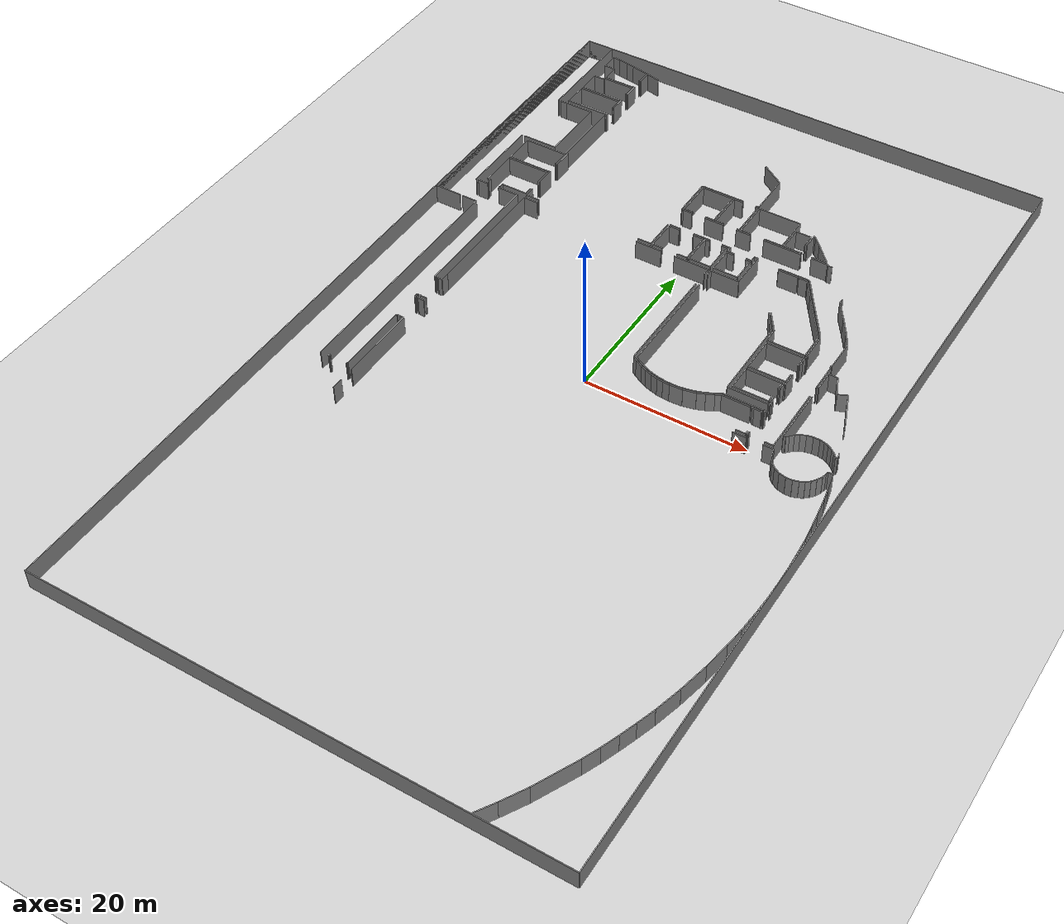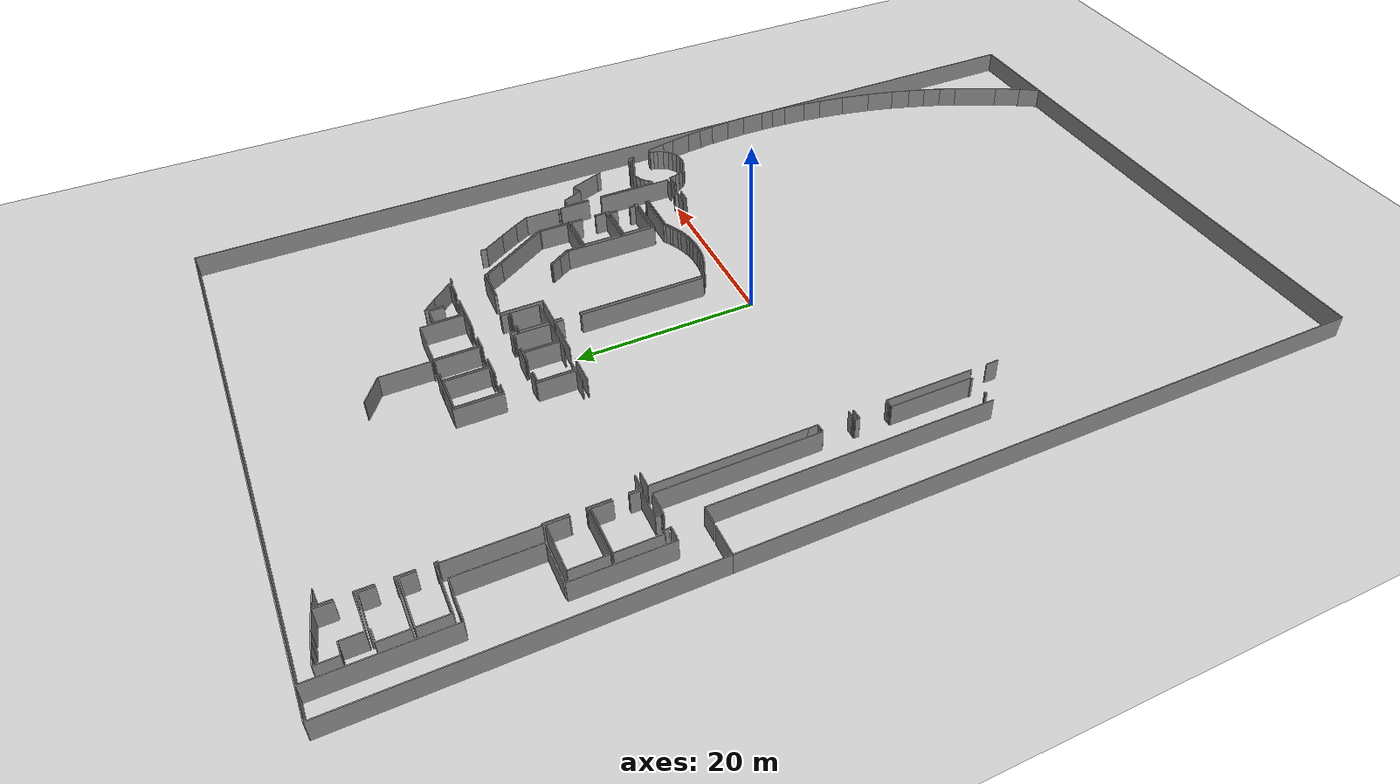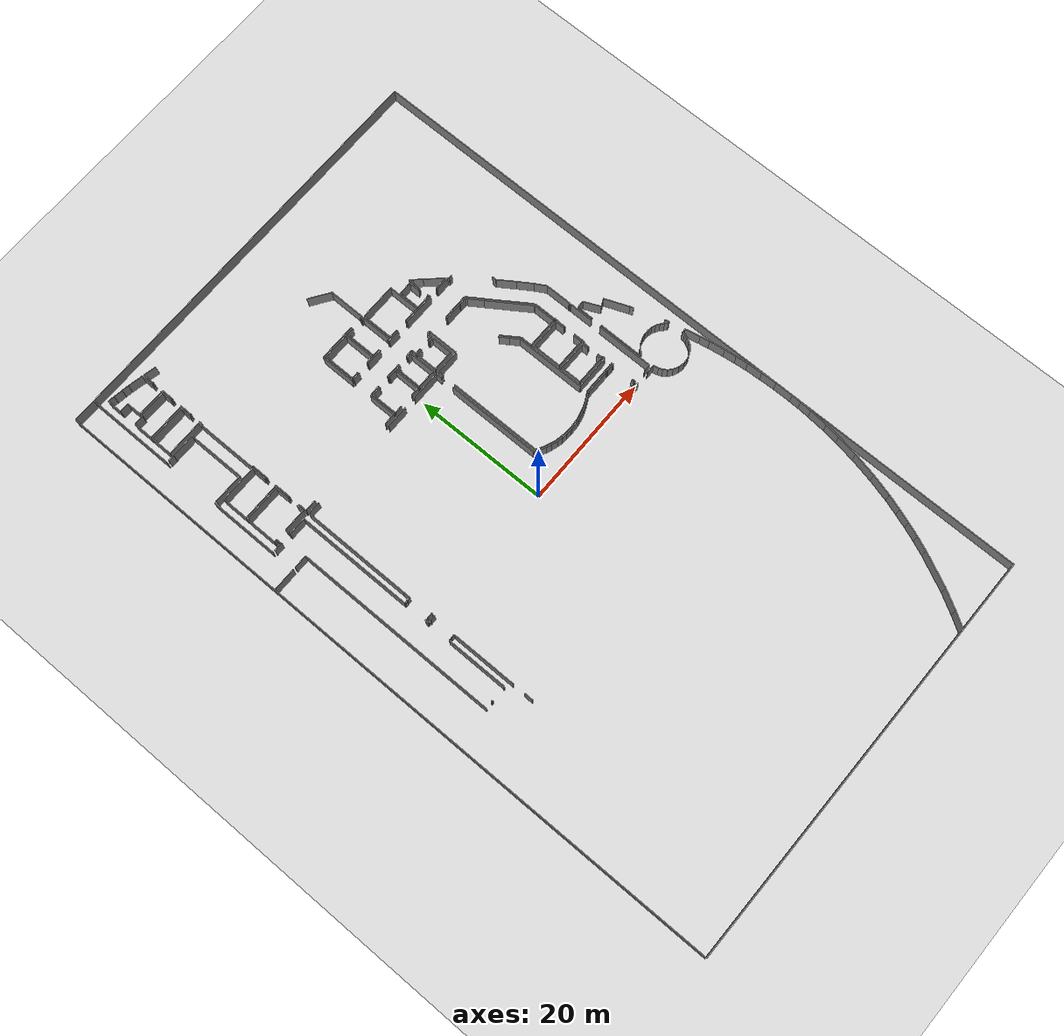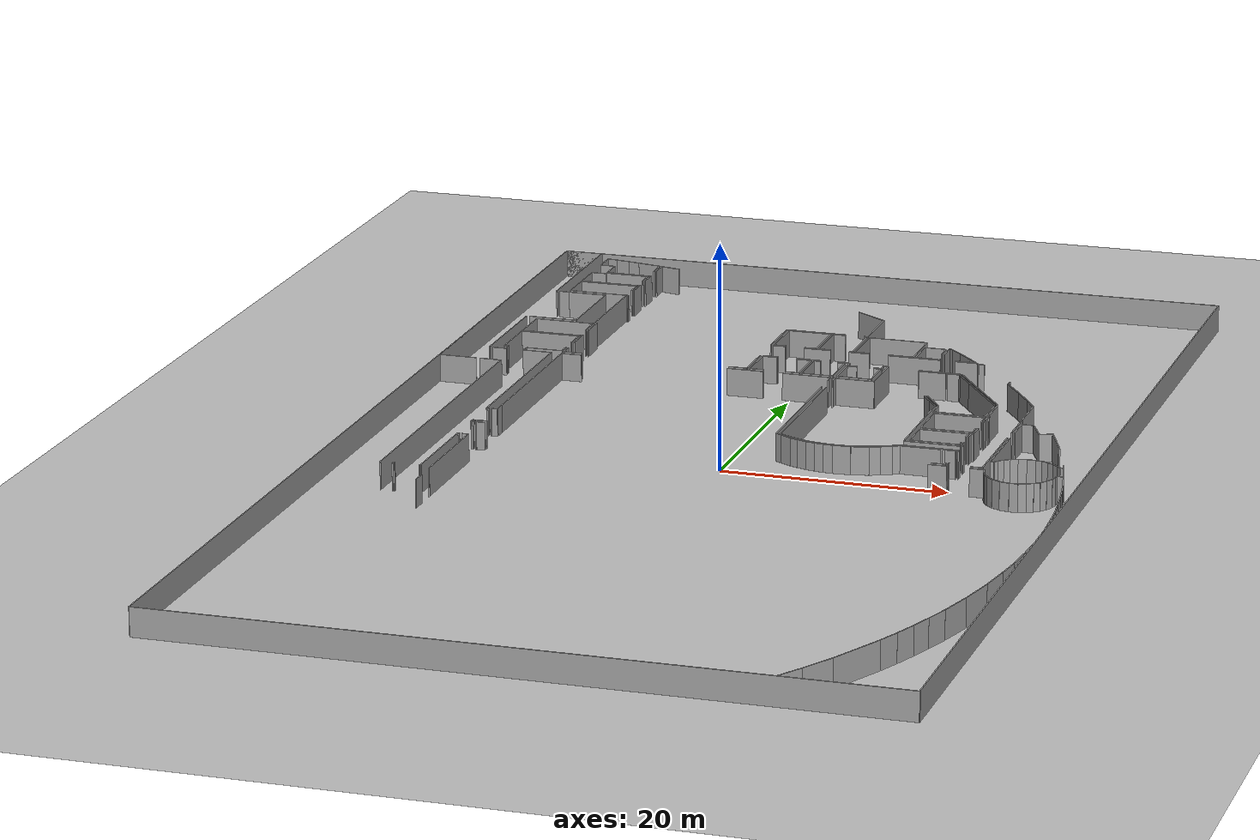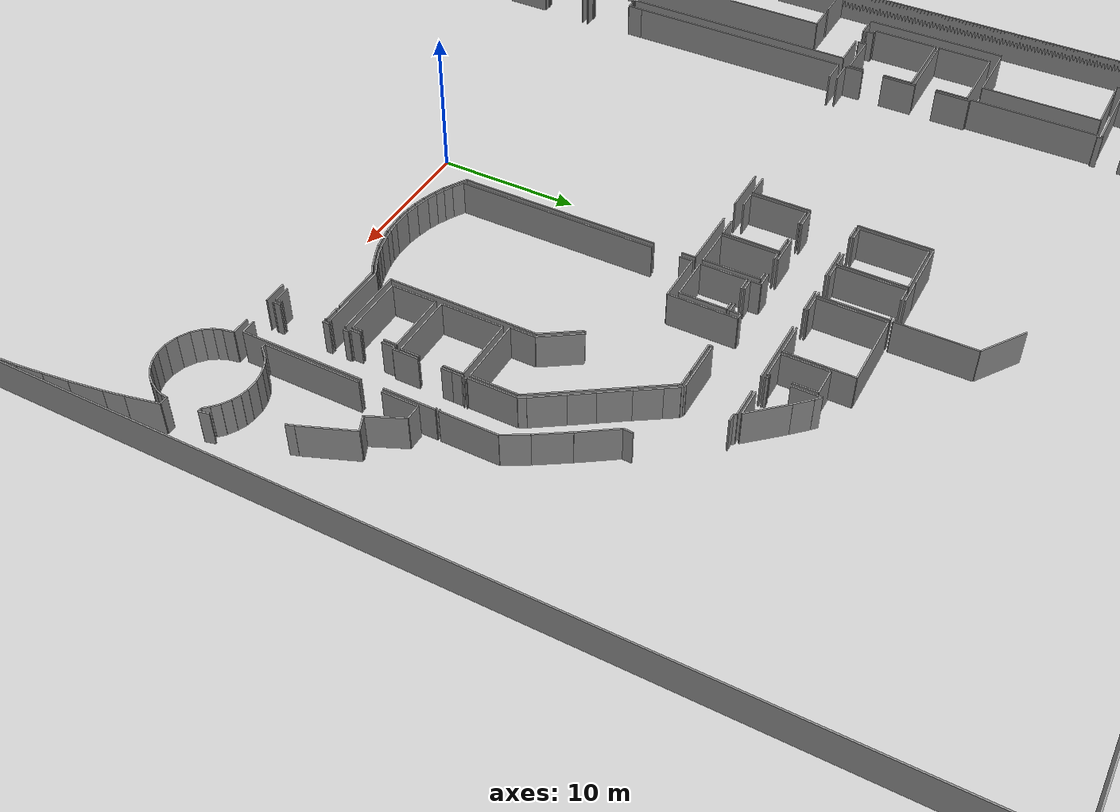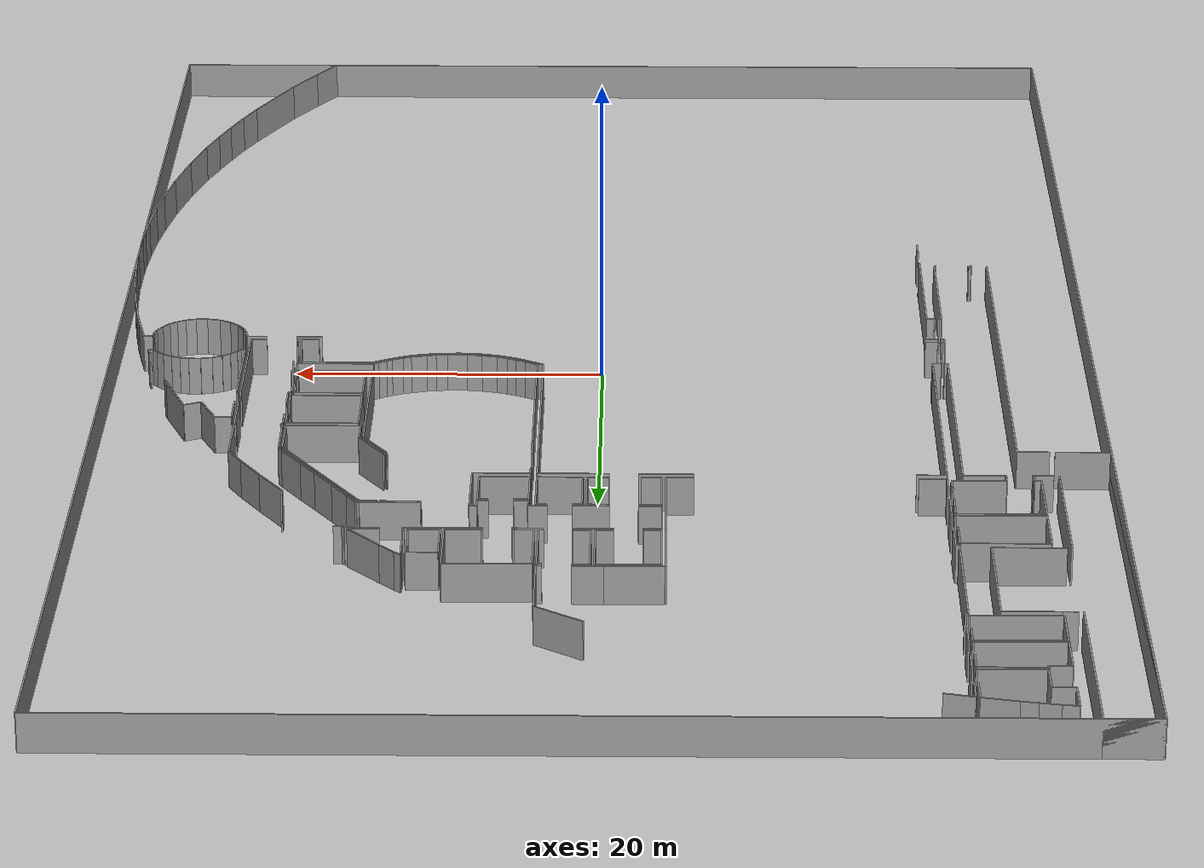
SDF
<sdf version="1.6">
  <world name="default">
    <light name="sun" type="directional">
      <cast_shadows>1</cast_shadows>
      <pose frame="">0 0 10 0 -0 0</pose>
      <diffuse>0.8 0.8 0.8 1</diffuse>
      <specular>0.1 0.1 0.1 1</specular>
      <attenuation>
        <range>1000</range>
        <constant>0.9</constant>
        <linear>0.01</linear>
        <quadratic>0.001</quadratic>
      </attenuation>
      <direction>-0.5 0.5 -1</direction>
    </light>
    <model name="ground_plane">
      <static>1</static>
      <link name="link">
        <collision name="collision">
          <geometry>
            <plane>
              <normal>0 0 1</normal>
              <size>100 100</size>
            </plane>
          </geometry>
          <surface>
            <friction>
              <ode>
                <mu>100</mu>
                <mu2>50</mu2>
              </ode>
              <torsional>
                <ode />
              </torsional>
            </friction>
            <contact>
              <ode />
            </contact>
            <bounce />
          </surface>
          <max_contacts>10</max_contacts>
        </collision>
        <visual name="visual">
          <cast_shadows>0</cast_shadows>
          <geometry>
            <plane>
              <normal>0 0 1</normal>
              <size>100 100</size>
            </plane>
          </geometry>
          <material>
            <script>
              <uri>file://media/materials/scripts/gazebo.material</uri>
              <name>Gazebo/Grey</name>
            </script>
          </material>
        </visual>
        <self_collide>0</self_collide>
        <kinematic>0</kinematic>
        <gravity>1</gravity>
      </link>
    </model>
    <gravity>0 0 -9.8</gravity>
    <magnetic_field>6e-06 2.3e-05 -4.2e-05</magnetic_field>
    <atmosphere type="adiabatic" />
    <physics default="0" name="default_physics" type="ode">
      <max_step_size>0.001</max_step_size>
      <real_time_factor>1</real_time_factor>
      <real_time_update_rate>1000</real_time_update_rate>
    </physics>
    <scene>
      <ambient>0.4 0.4 0.4 1</ambient>
      <background>0.7 0.7 0.7 1</background>
      <shadows>1</shadows>
    </scene>
    <spherical_coordinates>
      <surface_model>EARTH_WGS84</surface_model>
      <latitude_deg>0</latitude_deg>
      <longitude_deg>0</longitude_deg>
      <elevation>0</elevation>
      <heading_deg>0</heading_deg>
    </spherical_coordinates>
  <model name="50041193">
		<static>1</static>
		<link name="Wall_0">
			<collision name="Wall_0_Collision">
				<geometry>
					<box>
						<size>2.23893400435 0.1 2.5</size>
					</box>
				</geometry>
				<pose frame="">1.11946700217 0 1.25 0 0 0</pose>
			</collision>
			<visual name="Wall_0_Visual">
				<pose frame="">1.11946700217 0 1.25 0 0 0</pose>
				<geometry>
					<box>
						<size>2.23893400435 0.1 2.5</size>
					</box>
				</geometry>
				<material>
					<script>
						<uri>file://media/materials/scripts/gazebo.material</uri>
						<name>Gazebo/Grey</name>
					</script>
					<ambient>1 1 1 1</ambient>
				</material>
			</visual>
			<pose frame="">4.6344377089 -3.74422712773 0 0 0 1.57079632679</pose>
		</link>
		<link name="Wall_1">
			<collision name="Wall_1_Collision">
				<geometry>
					<box>
						<size>0.972347669635 0.1 2.5</size>
					</box>
				</geometry>
				<pose frame="">0.486173834817 0 1.25 0 0 0</pose>
			</collision>
			<visual name="Wall_1_Visual">
				<pose frame="">0.486173834817 0 1.25 0 0 0</pose>
				<geometry>
					<box>
						<size>0.972347669635 0.1 2.5</size>
					</box>
				</geometry>
				<material>
					<script>
						<uri>file://media/materials/scripts/gazebo.material</uri>
						<name>Gazebo/Grey</name>
					</script>
					<ambient>1 1 1 1</ambient>
				</material>
			</visual>
			<pose frame="">4.6344377089 -1.50529312339 0 0 0 -0.128531046348</pose>
		</link>
		<link name="Wall_2">
			<collision name="Wall_2_Collision">
				<geometry>
					<box>
						<size>1.2935995405 0.1 2.5</size>
					</box>
				</geometry>
				<pose frame="">0.646799770251 0 1.25 0 0 0</pose>
			</collision>
			<visual name="Wall_2_Visual">
				<pose frame="">0.646799770251 0 1.25 0 0 0</pose>
				<geometry>
					<box>
						<size>1.2935995405 0.1 2.5</size>
					</box>
				</geometry>
				<material>
					<script>
						<uri>file://media/materials/scripts/gazebo.material</uri>
						<name>Gazebo/Grey</name>
					</script>
					<ambient>1 1 1 1</ambient>
				</material>
			</visual>
			<pose frame="">5.59876472607 -1.62992616315 0 0 0 -0.167787734921</pose>
		</link>
		<link name="Wall_3">
			<collision name="Wall_3_Collision">
				<geometry>
					<box>
						<size>1.03198427809 0.1 2.5</size>
					</box>
				</geometry>
				<pose frame="">0.515992139046 0 1.25 0 0 0</pose>
			</collision>
			<visual name="Wall_3_Visual">
				<pose frame="">0.515992139046 0 1.25 0 0 0</pose>
				<geometry>
					<box>
						<size>1.03198427809 0.1 2.5</size>
					</box>
				</geometry>
				<material>
					<script>
						<uri>file://media/materials/scripts/gazebo.material</uri>
						<name>Gazebo/Grey</name>
					</script>
					<ambient>1 1 1 1</ambient>
				</material>
			</visual>
			<pose frame="">6.87419777092 -1.84595930713 0 0 0 -0.165812721549</pose>
		</link>
		<link name="Wall_4">
			<collision name="Wall_4_Collision">
				<geometry>
					<box>
						<size>2.25865235353 0.1 2.5</size>
					</box>
				</geometry>
				<pose frame="">1.12932617677 0 1.25 0 0 0</pose>
			</collision>
			<visual name="Wall_4_Visual">
				<pose frame="">1.12932617677 0 1.25 0 0 0</pose>
				<geometry>
					<box>
						<size>2.25865235353 0.1 2.5</size>
					</box>
				</geometry>
				<material>
					<script>
						<uri>file://media/materials/scripts/gazebo.material</uri>
						<name>Gazebo/Grey</name>
					</script>
					<ambient>1 1 1 1</ambient>
				</material>
			</visual>
			<pose frame="">7.89202790804 -2.016292399 0 0 0 -0.204866128414</pose>
		</link>
		<link name="Wall_5">
			<collision name="Wall_5_Collision">
				<geometry>
					<box>
						<size>1.85869330385 0.1 2.5</size>
					</box>
				</geometry>
				<pose frame="">0.929346651925 0 1.25 0 0 0</pose>
			</collision>
			<visual name="Wall_5_Visual">
				<pose frame="">0.929346651925 0 1.25 0 0 0</pose>
				<geometry>
					<box>
						<size>1.85869330385 0.1 2.5</size>
					</box>
				</geometry>
				<material>
					<script>
						<uri>file://media/materials/scripts/gazebo.material</uri>
						<name>Gazebo/Grey</name>
					</script>
					<ambient>1 1 1 1</ambient>
				</material>
			</visual>
			<pose frame="">10.1034478376 -2.47578380164 0 0 0 -1.57079632679</pose>
		</link>
		<link name="Wall_6">
			<collision name="Wall_6_Collision">
				<geometry>
					<box>
						<size>0.100270692745 0.1 2.5</size>
					</box>
				</geometry>
				<pose frame="">0.0501353463723 0 1.25 0 0 0</pose>
			</collision>
			<visual name="Wall_6_Visual">
				<pose frame="">0.0501353463723 0 1.25 0 0 0</pose>
				<geometry>
					<box>
						<size>0.100270692745 0.1 2.5</size>
					</box>
				</geometry>
				<material>
					<script>
						<uri>file://media/materials/scripts/gazebo.material</uri>
						<name>Gazebo/Grey</name>
					</script>
					<ambient>1 1 1 1</ambient>
				</material>
			</visual>
			<pose frame="">10.1034478376 -5.85833746362 0 0 0 -1.57079632679</pose>
		</link>
		<link name="Wall_7">
			<collision name="Wall_7_Collision">
				<geometry>
					<box>
						<size>4.05797653996 0.1 2.5</size>
					</box>
				</geometry>
				<pose frame="">2.02898826998 0 1.25 0 0 0</pose>
			</collision>
			<visual name="Wall_7_Visual">
				<pose frame="">2.02898826998 0 1.25 0 0 0</pose>
				<geometry>
					<box>
						<size>4.05797653996 0.1 2.5</size>
					</box>
				</geometry>
				<material>
					<script>
						<uri>file://media/materials/scripts/gazebo.material</uri>
						<name>Gazebo/Grey</name>
					</script>
					<ambient>1 1 1 1</ambient>
				</material>
			</visual>
			<pose frame="">10.1034478376 -5.95860815637 0 0 0 3.14159265359</pose>
		</link>
		<link name="Wall_8">
			<collision name="Wall_8_Collision">
				<geometry>
					<box>
						<size>2.20242225526 0.1 2.5</size>
					</box>
				</geometry>
				<pose frame="">1.10121112763 0 1.25 0 0 0</pose>
			</collision>
			<visual name="Wall_8_Visual">
				<pose frame="">1.10121112763 0 1.25 0 0 0</pose>
				<geometry>
					<box>
						<size>2.20242225526 0.1 2.5</size>
					</box>
				</geometry>
				<material>
					<script>
						<uri>file://media/materials/scripts/gazebo.material</uri>
						<name>Gazebo/Grey</name>
					</script>
					<ambient>1 1 1 1</ambient>
				</material>
			</visual>
			<pose frame="">6.04547129767 -5.95860815637 0 0 0 1.57079632679</pose>
		</link>
		<link name="Wall_9">
			<collision name="Wall_9_Collision">
				<geometry>
					<box>
						<size>1.41108426429 0.1 2.5</size>
					</box>
				</geometry>
				<pose frame="">0.705542132143 0 1.25 0 0 0</pose>
			</collision>
			<visual name="Wall_9_Visual">
				<pose frame="">0.705542132143 0 1.25 0 0 0</pose>
				<geometry>
					<box>
						<size>1.41108426429 0.1 2.5</size>
					</box>
				</geometry>
				<material>
					<script>
						<uri>file://media/materials/scripts/gazebo.material</uri>
						<name>Gazebo/Grey</name>
					</script>
					<ambient>1 1 1 1</ambient>
				</material>
			</visual>
			<pose frame="">6.04547129767 -3.7561859011 0 0 0 3.13311766962</pose>
		</link>
		<link name="Wall_10">
			<collision name="Wall_10_Collision">
				<geometry>
					<box>
						<size>2.9570322925 0.1 2.5</size>
					</box>
				</geometry>
				<pose frame="">1.47851614625 0 1.25 0 0 0</pose>
			</collision>
			<visual name="Wall_10_Visual">
				<pose frame="">1.47851614625 0 1.25 0 0 0</pose>
				<geometry>
					<box>
						<size>2.9570322925 0.1 2.5</size>
					</box>
				</geometry>
				<material>
					<script>
						<uri>file://media/materials/scripts/gazebo.material</uri>
						<name>Gazebo/Grey</name>
					</script>
					<ambient>1 1 1 1</ambient>
				</material>
			</visual>
			<pose frame="">4.63786902538 -9.36501582218 0 0 0 1.57079632679</pose>
		</link>
		<link name="Wall_11">
			<collision name="Wall_11_Collision">
				<geometry>
					<box>
						<size>1.38892066034 0.1 2.5</size>
					</box>
				</geometry>
				<pose frame="">0.694460330169 0 1.25 0 0 0</pose>
			</collision>
			<visual name="Wall_11_Visual">
				<pose frame="">0.694460330169 0 1.25 0 0 0</pose>
				<geometry>
					<box>
						<size>1.38892066034 0.1 2.5</size>
					</box>
				</geometry>
				<material>
					<script>
						<uri>file://media/materials/scripts/gazebo.material</uri>
						<name>Gazebo/Grey</name>
					</script>
					<ambient>1 1 1 1</ambient>
				</material>
			</visual>
			<pose frame="">4.63786902538 -6.40798352968 0 0 0 0.0</pose>
		</link>
		<link name="Wall_12">
			<collision name="Wall_12_Collision">
				<geometry>
					<box>
						<size>0.204226873562 0.1 2.5</size>
					</box>
				</geometry>
				<pose frame="">0.102113436781 0 1.25 0 0 0</pose>
			</collision>
			<visual name="Wall_12_Visual">
				<pose frame="">0.102113436781 0 1.25 0 0 0</pose>
				<geometry>
					<box>
						<size>0.204226873562 0.1 2.5</size>
					</box>
				</geometry>
				<material>
					<script>
						<uri>file://media/materials/scripts/gazebo.material</uri>
						<name>Gazebo/Grey</name>
					</script>
					<ambient>1 1 1 1</ambient>
				</material>
			</visual>
			<pose frame="">6.02678968572 -6.40798352968 0 0 0 1.57079632679</pose>
		</link>
		<link name="Wall_13">
			<collision name="Wall_13_Collision">
				<geometry>
					<box>
						<size>4.06712671725 0.1 2.5</size>
					</box>
				</geometry>
				<pose frame="">2.03356335862 0 1.25 0 0 0</pose>
			</collision>
			<visual name="Wall_13_Visual">
				<pose frame="">2.03356335862 0 1.25 0 0 0</pose>
				<geometry>
					<box>
						<size>4.06712671725 0.1 2.5</size>
					</box>
				</geometry>
				<material>
					<script>
						<uri>file://media/materials/scripts/gazebo.material</uri>
						<name>Gazebo/Grey</name>
					</script>
					<ambient>1 1 1 1</ambient>
				</material>
			</visual>
			<pose frame="">6.02678968572 -6.20375665612 0 0 0 0.0</pose>
		</link>
		<link name="Wall_14">
			<collision name="Wall_14_Collision">
				<geometry>
					<box>
						<size>1.53735686962 0.1 2.5</size>
					</box>
				</geometry>
				<pose frame="">0.768678434811 0 1.25 0 0 0</pose>
			</collision>
			<visual name="Wall_14_Visual">
				<pose frame="">0.768678434811 0 1.25 0 0 0</pose>
				<geometry>
					<box>
						<size>1.53735686962 0.1 2.5</size>
					</box>
				</geometry>
				<material>
					<script>
						<uri>file://media/materials/scripts/gazebo.material</uri>
						<name>Gazebo/Grey</name>
					</script>
					<ambient>1 1 1 1</ambient>
				</material>
			</visual>
			<pose frame="">10.093916403 -6.20375665612 0 0 0 -1.57079632679</pose>
		</link>
		<link name="Wall_15">
			<collision name="Wall_15_Collision">
				<geometry>
					<box>
						<size>0.109929213212 0.1 2.5</size>
					</box>
				</geometry>
				<pose frame="">0.0549646066059 0 1.25 0 0 0</pose>
			</collision>
			<visual name="Wall_15_Visual">
				<pose frame="">0.0549646066059 0 1.25 0 0 0</pose>
				<geometry>
					<box>
						<size>0.109929213212 0.1 2.5</size>
					</box>
				</geometry>
				<material>
					<script>
						<uri>file://media/materials/scripts/gazebo.material</uri>
						<name>Gazebo/Grey</name>
					</script>
					<ambient>1 1 1 1</ambient>
				</material>
			</visual>
			<pose frame="">10.093916403 -9.25572203795 0 0 0 -1.57079632679</pose>
		</link>
		<link name="Wall_16">
			<collision name="Wall_16_Collision">
				<geometry>
					<box>
						<size>5.45604741459 0.1 2.5</size>
					</box>
				</geometry>
				<pose frame="">2.72802370729 0 1.25 0 0 0</pose>
			</collision>
			<visual name="Wall_16_Visual">
				<pose frame="">2.72802370729 0 1.25 0 0 0</pose>
				<geometry>
					<box>
						<size>5.45604741459 0.1 2.5</size>
					</box>
				</geometry>
				<material>
					<script>
						<uri>file://media/materials/scripts/gazebo.material</uri>
						<name>Gazebo/Grey</name>
					</script>
					<ambient>1 1 1 1</ambient>
				</material>
			</visual>
			<pose frame="">10.093916403 -9.36565125116 0 0 0 3.14147619035</pose>
		</link>
		<link name="Wall_17">
			<collision name="Wall_17_Collision">
				<geometry>
					<box>
						<size>3.1456276132 0.1 2.5</size>
					</box>
				</geometry>
				<pose frame="">1.5728138066 0 1.25 0 0 0</pose>
			</collision>
			<visual name="Wall_17_Visual">
				<pose frame="">1.5728138066 0 1.25 0 0 0</pose>
				<geometry>
					<box>
						<size>3.1456276132 0.1 2.5</size>
					</box>
				</geometry>
				<material>
					<script>
						<uri>file://media/materials/scripts/gazebo.material</uri>
						<name>Gazebo/Grey</name>
					</script>
					<ambient>1 1 1 1</ambient>
				</material>
			</visual>
			<pose frame="">4.63786902538 -12.7571898789 0 0 0 1.57079632679</pose>
		</link>
		<link name="Wall_18">
			<collision name="Wall_18_Collision">
				<geometry>
					<box>
						<size>5.46850178556 0.1 2.5</size>
					</box>
				</geometry>
				<pose frame="">2.73425089278 0 1.25 0 0 0</pose>
			</collision>
			<visual name="Wall_18_Visual">
				<pose frame="">2.73425089278 0 1.25 0 0 0</pose>
				<geometry>
					<box>
						<size>5.46850178556 0.1 2.5</size>
					</box>
				</geometry>
				<material>
					<script>
						<uri>file://media/materials/scripts/gazebo.material</uri>
						<name>Gazebo/Grey</name>
					</script>
					<ambient>1 1 1 1</ambient>
				</material>
			</visual>
			<pose frame="">4.63786902538 -9.61156226569 0 0 0 0.0</pose>
		</link>
		<link name="Wall_19">
			<collision name="Wall_19_Collision">
				<geometry>
					<box>
						<size>1.52121697358 0.1 2.5</size>
					</box>
				</geometry>
				<pose frame="">0.760608486789 0 1.25 0 0 0</pose>
			</collision>
			<visual name="Wall_19_Visual">
				<pose frame="">0.760608486789 0 1.25 0 0 0</pose>
				<geometry>
					<box>
						<size>1.52121697358 0.1 2.5</size>
					</box>
				</geometry>
				<material>
					<script>
						<uri>file://media/materials/scripts/gazebo.material</uri>
						<name>Gazebo/Grey</name>
					</script>
					<ambient>1 1 1 1</ambient>
				</material>
			</visual>
			<pose frame="">10.1063708109 -9.61156226569 0 0 0 -1.57079632679</pose>
		</link>
		<link name="Wall_20">
			<collision name="Wall_20_Collision">
				<geometry>
					<box>
						<size>0.0955685183067 0.1 2.5</size>
					</box>
				</geometry>
				<pose frame="">0.0477842591534 0 1.25 0 0 0</pose>
			</collision>
			<visual name="Wall_20_Visual">
				<pose frame="">0.0477842591534 0 1.25 0 0 0</pose>
				<geometry>
					<box>
						<size>0.0955685183067 0.1 2.5</size>
					</box>
				</geometry>
				<material>
					<script>
						<uri>file://media/materials/scripts/gazebo.material</uri>
						<name>Gazebo/Grey</name>
					</script>
					<ambient>1 1 1 1</ambient>
				</material>
			</visual>
			<pose frame="">10.1063708109 -12.6664506208 0 0 0 -1.57079632679</pose>
		</link>
		<link name="Wall_21">
			<collision name="Wall_21_Collision">
				<geometry>
					<box>
						<size>5.46850391793 0.1 2.5</size>
					</box>
				</geometry>
				<pose frame="">2.73425195896 0 1.25 0 0 0</pose>
			</collision>
			<visual name="Wall_21_Visual">
				<pose frame="">2.73425195896 0 1.25 0 0 0</pose>
				<geometry>
					<box>
						<size>5.46850391793 0.1 2.5</size>
					</box>
				</geometry>
				<material>
					<script>
						<uri>file://media/materials/scripts/gazebo.material</uri>
						<name>Gazebo/Grey</name>
					</script>
					<ambient>1 1 1 1</ambient>
				</material>
			</visual>
			<pose frame="">10.1063708109 -12.7620191391 0 0 0 3.14070954901</pose>
		</link>
		<link name="Wall_22">
			<collision name="Wall_22_Collision">
				<geometry>
					<box>
						<size>3.91970719433 0.1 2.5</size>
					</box>
				</geometry>
				<pose frame="">1.95985359716 0 1.25 0 0 0</pose>
			</collision>
			<visual name="Wall_22_Visual">
				<pose frame="">1.95985359716 0 1.25 0 0 0</pose>
				<geometry>
					<box>
						<size>3.91970719433 0.1 2.5</size>
					</box>
				</geometry>
				<material>
					<script>
						<uri>file://media/materials/scripts/gazebo.material</uri>
						<name>Gazebo/Grey</name>
					</script>
					<ambient>1 1 1 1</ambient>
				</material>
			</visual>
			<pose frame="">4.63837736856 -26.3525741228 0 0 0 1.57079632679</pose>
		</link>
		<link name="Wall_23">
			<collision name="Wall_23_Collision">
				<geometry>
					<box>
						<size>5.45337857588 0.1 2.5</size>
					</box>
				</geometry>
				<pose frame="">2.72668928794 0 1.25 0 0 0</pose>
			</collision>
			<visual name="Wall_23_Visual">
				<pose frame="">2.72668928794 0 1.25 0 0 0</pose>
				<geometry>
					<box>
						<size>5.45337857588 0.1 2.5</size>
					</box>
				</geometry>
				<material>
					<script>
						<uri>file://media/materials/scripts/gazebo.material</uri>
						<name>Gazebo/Grey</name>
					</script>
					<ambient>1 1 1 1</ambient>
				</material>
			</visual>
			<pose frame="">4.63837736856 -22.4328669285 0 0 0 0.0</pose>
		</link>
		<link name="Wall_24">
			<collision name="Wall_24_Collision">
				<geometry>
					<box>
						<size>2.17265876193 0.1 2.5</size>
					</box>
				</geometry>
				<pose frame="">1.08632938097 0 1.25 0 0 0</pose>
			</collision>
			<visual name="Wall_24_Visual">
				<pose frame="">1.08632938097 0 1.25 0 0 0</pose>
				<geometry>
					<box>
						<size>2.17265876193 0.1 2.5</size>
					</box>
				</geometry>
				<material>
					<script>
						<uri>file://media/materials/scripts/gazebo.material</uri>
						<name>Gazebo/Grey</name>
					</script>
					<ambient>1 1 1 1</ambient>
				</material>
			</visual>
			<pose frame="">10.0917559444 -22.4328669285 0 0 0 -1.57079632679</pose>
		</link>
		<link name="Wall_25">
			<collision name="Wall_25_Collision">
				<geometry>
					<box>
						<size>0.0404132830073 0.1 2.5</size>
					</box>
				</geometry>
				<pose frame="">0.0202066415037 0 1.25 0 0 0</pose>
			</collision>
			<visual name="Wall_25_Visual">
				<pose frame="">0.0202066415037 0 1.25 0 0 0</pose>
				<geometry>
					<box>
						<size>0.0404132830073 0.1 2.5</size>
					</box>
				</geometry>
				<material>
					<script>
						<uri>file://media/materials/scripts/gazebo.material</uri>
						<name>Gazebo/Grey</name>
					</script>
					<ambient>1 1 1 1</ambient>
				</material>
			</visual>
			<pose frame="">10.0917559444 -24.6055256904 0 0 0 0.0</pose>
		</link>
		<link name="Wall_26">
			<collision name="Wall_26_Collision">
				<geometry>
					<box>
						<size>0.120350248453 0.1 2.5</size>
					</box>
				</geometry>
				<pose frame="">0.0601751242264 0 1.25 0 0 0</pose>
			</collision>
			<visual name="Wall_26_Visual">
				<pose frame="">0.0601751242264 0 1.25 0 0 0</pose>
				<geometry>
					<box>
						<size>0.120350248453 0.1 2.5</size>
					</box>
				</geometry>
				<material>
					<script>
						<uri>file://media/materials/scripts/gazebo.material</uri>
						<name>Gazebo/Grey</name>
					</script>
					<ambient>1 1 1 1</ambient>
				</material>
			</visual>
			<pose frame="">10.1321692274 -24.6055256904 0 0 0 -1.57079632679</pose>
		</link>
		<link name="Wall_27">
			<collision name="Wall_27_Collision">
				<geometry>
					<box>
						<size>0.0660846137227 0.1 2.5</size>
					</box>
				</geometry>
				<pose frame="">0.0330423068614 0 1.25 0 0 0</pose>
			</collision>
			<visual name="Wall_27_Visual">
				<pose frame="">0.0330423068614 0 1.25 0 0 0</pose>
				<geometry>
					<box>
						<size>0.0660846137227 0.1 2.5</size>
					</box>
				</geometry>
				<material>
					<script>
						<uri>file://media/materials/scripts/gazebo.material</uri>
						<name>Gazebo/Grey</name>
					</script>
					<ambient>1 1 1 1</ambient>
				</material>
			</visual>
			<pose frame="">10.1321692274 -26.2711121278 0 0 0 -1.57079632679</pose>
		</link>
		<link name="Wall_28">
			<collision name="Wall_28_Collision">
				<geometry>
					<box>
						<size>5.49381337985 0.1 2.5</size>
					</box>
				</geometry>
				<pose frame="">2.74690668992 0 1.25 0 0 0</pose>
			</collision>
			<visual name="Wall_28_Visual">
				<pose frame="">2.74690668992 0 1.25 0 0 0</pose>
				<geometry>
					<box>
						<size>5.49381337985 0.1 2.5</size>
					</box>
				</geometry>
				<material>
					<script>
						<uri>file://media/materials/scripts/gazebo.material</uri>
						<name>Gazebo/Grey</name>
					</script>
					<ambient>1 1 1 1</ambient>
				</material>
			</visual>
			<pose frame="">10.1321692274 -26.3371967415 0 0 0 -3.13879361396</pose>
		</link>
		<link name="Wall_29">
			<collision name="Wall_29_Collision">
				<geometry>
					<box>
						<size>4.75084829769 0.1 2.5</size>
					</box>
				</geometry>
				<pose frame="">2.37542414884 0 1.25 0 0 0</pose>
			</collision>
			<visual name="Wall_29_Visual">
				<pose frame="">2.37542414884 0 1.25 0 0 0</pose>
				<geometry>
					<box>
						<size>4.75084829769 0.1 2.5</size>
					</box>
				</geometry>
				<material>
					<script>
						<uri>file://media/materials/scripts/gazebo.material</uri>
						<name>Gazebo/Grey</name>
					</script>
					<ambient>1 1 1 1</ambient>
				</material>
			</visual>
			<pose frame="">4.63659816742 -31.3484438344 0 0 0 1.57079632679</pose>
		</link>
		<link name="Wall_30">
			<collision name="Wall_30_Collision">
				<geometry>
					<box>
						<size>5.4700268151 0.1 2.5</size>
					</box>
				</geometry>
				<pose frame="">2.73501340755 0 1.25 0 0 0</pose>
			</collision>
			<visual name="Wall_30_Visual">
				<pose frame="">2.73501340755 0 1.25 0 0 0</pose>
				<geometry>
					<box>
						<size>5.4700268151 0.1 2.5</size>
					</box>
				</geometry>
				<material>
					<script>
						<uri>file://media/materials/scripts/gazebo.material</uri>
						<name>Gazebo/Grey</name>
					</script>
					<ambient>1 1 1 1</ambient>
				</material>
			</visual>
			<pose frame="">4.63659816742 -26.5975955367 0 0 0 0.0</pose>
		</link>
		<link name="Wall_31">
			<collision name="Wall_31_Collision">
				<geometry>
					<box>
						<size>2.13529553802 0.1 2.5</size>
					</box>
				</geometry>
				<pose frame="">1.06764776901 0 1.25 0 0 0</pose>
			</collision>
			<visual name="Wall_31_Visual">
				<pose frame="">1.06764776901 0 1.25 0 0 0</pose>
				<geometry>
					<box>
						<size>2.13529553802 0.1 2.5</size>
					</box>
				</geometry>
				<material>
					<script>
						<uri>file://media/materials/scripts/gazebo.material</uri>
						<name>Gazebo/Grey</name>
					</script>
					<ambient>1 1 1 1</ambient>
				</material>
			</visual>
			<pose frame="">10.1066249825 -26.5975955367 0 0 0 -1.57079632679</pose>
		</link>
		<link name="Wall_32">
			<collision name="Wall_32_Collision">
				<geometry>
					<box>
						<size>1.07006239913 0.1 2.5</size>
					</box>
				</geometry>
				<pose frame="">0.535031199563 0 1.25 0 0 0</pose>
			</collision>
			<visual name="Wall_32_Visual">
				<pose frame="">0.535031199563 0 1.25 0 0 0</pose>
				<geometry>
					<box>
						<size>1.07006239913 0.1 2.5</size>
					</box>
				</geometry>
				<material>
					<script>
						<uri>file://media/materials/scripts/gazebo.material</uri>
						<name>Gazebo/Grey</name>
					</script>
					<ambient>1 1 1 1</ambient>
				</material>
			</visual>
			<pose frame="">10.1066249825 -30.27672932 0 0 0 -1.57079632679</pose>
		</link>
		<link name="Wall_33">
			<collision name="Wall_33_Collision">
				<geometry>
					<box>
						<size>3.35671711973 0.1 2.5</size>
					</box>
				</geometry>
				<pose frame="">1.67835855986 0 1.25 0 0 0</pose>
			</collision>
			<visual name="Wall_33_Visual">
				<pose frame="">1.67835855986 0 1.25 0 0 0</pose>
				<geometry>
					<box>
						<size>3.35671711973 0.1 2.5</size>
					</box>
				</geometry>
				<material>
					<script>
						<uri>file://media/materials/scripts/gazebo.material</uri>
						<name>Gazebo/Grey</name>
					</script>
					<ambient>1 1 1 1</ambient>
				</material>
			</visual>
			<pose frame="">10.1066249825 -31.3467917191 0 0 0 3.14159265359</pose>
		</link>
		<link name="Wall_34">
			<collision name="Wall_34_Collision">
				<geometry>
					<box>
						<size>0.565150533125 0.1 2.5</size>
					</box>
				</geometry>
				<pose frame="">0.282575266562 0 1.25 0 0 0</pose>
			</collision>
			<visual name="Wall_34_Visual">
				<pose frame="">0.282575266562 0 1.25 0 0 0</pose>
				<geometry>
					<box>
						<size>0.565150533125 0.1 2.5</size>
					</box>
				</geometry>
				<material>
					<script>
						<uri>file://media/materials/scripts/gazebo.material</uri>
						<name>Gazebo/Grey</name>
					</script>
					<ambient>1 1 1 1</ambient>
				</material>
			</visual>
			<pose frame="">6.7499078628 -31.3467917191 0 0 0 -1.57079632679</pose>
		</link>
		<link name="Wall_35">
			<collision name="Wall_35_Collision">
				<geometry>
					<box>
						<size>0.0940434887593 0.1 2.5</size>
					</box>
				</geometry>
				<pose frame="">0.0470217443796 0 1.25 0 0 0</pose>
			</collision>
			<visual name="Wall_35_Visual">
				<pose frame="">0.0470217443796 0 1.25 0 0 0</pose>
				<geometry>
					<box>
						<size>0.0940434887593 0.1 2.5</size>
					</box>
				</geometry>
				<material>
					<script>
						<uri>file://media/materials/scripts/gazebo.material</uri>
						<name>Gazebo/Grey</name>
					</script>
					<ambient>1 1 1 1</ambient>
				</material>
			</visual>
			<pose frame="">6.7499078628 -31.9119422522 0 0 0 3.14159265359</pose>
		</link>
		<link name="Wall_36">
			<collision name="Wall_36_Collision">
				<geometry>
					<box>
						<size>0.0847662256789 0.1 2.5</size>
					</box>
				</geometry>
				<pose frame="">0.0423831128395 0 1.25 0 0 0</pose>
			</collision>
			<visual name="Wall_36_Visual">
				<pose frame="">0.0423831128395 0 1.25 0 0 0</pose>
				<geometry>
					<box>
						<size>0.0847662256789 0.1 2.5</size>
					</box>
				</geometry>
				<material>
					<script>
						<uri>file://media/materials/scripts/gazebo.material</uri>
						<name>Gazebo/Grey</name>
					</script>
					<ambient>1 1 1 1</ambient>
				</material>
			</visual>
			<pose frame="">5.10948441293 -31.9119422522 0 0 0 3.14159265359</pose>
		</link>
		<link name="Wall_37">
			<collision name="Wall_37_Collision">
				<geometry>
					<box>
						<size>0.564642189942 0.1 2.5</size>
					</box>
				</geometry>
				<pose frame="">0.282321094971 0 1.25 0 0 0</pose>
			</collision>
			<visual name="Wall_37_Visual">
				<pose frame="">0.282321094971 0 1.25 0 0 0</pose>
				<geometry>
					<box>
						<size>0.564642189942 0.1 2.5</size>
					</box>
				</geometry>
				<material>
					<script>
						<uri>file://media/materials/scripts/gazebo.material</uri>
						<name>Gazebo/Grey</name>
					</script>
					<ambient>1 1 1 1</ambient>
				</material>
			</visual>
			<pose frame="">5.02471818725 -31.9119422522 0 0 0 1.57079632679</pose>
		</link>
		<link name="Wall_38">
			<collision name="Wall_38_Collision">
				<geometry>
					<box>
						<size>0.388121705144 0.1 2.5</size>
					</box>
				</geometry>
				<pose frame="">0.194060852572 0 1.25 0 0 0</pose>
			</collision>
			<visual name="Wall_38_Visual">
				<pose frame="">0.194060852572 0 1.25 0 0 0</pose>
				<geometry>
					<box>
						<size>0.388121705144 0.1 2.5</size>
					</box>
				</geometry>
				<material>
					<script>
						<uri>file://media/materials/scripts/gazebo.material</uri>
						<name>Gazebo/Grey</name>
					</script>
					<ambient>1 1 1 1</ambient>
				</material>
			</visual>
			<pose frame="">5.02471818725 -31.3473000623 0 0 0 -3.13864570731</pose>
		</link>
		<link name="Wall_39">
			<collision name="Wall_39_Collision">
				<geometry>
					<box>
						<size>17.3478465312 0.1 2.5</size>
					</box>
				</geometry>
				<pose frame="">8.6739232656 0 1.25 0 0 0</pose>
			</collision>
			<visual name="Wall_39_Visual">
				<pose frame="">8.6739232656 0 1.25 0 0 0</pose>
				<geometry>
					<box>
						<size>17.3478465312 0.1 2.5</size>
					</box>
				</geometry>
				<material>
					<script>
						<uri>file://media/materials/scripts/gazebo.material</uri>
						<name>Gazebo/Grey</name>
					</script>
					<ambient>1 1 1 1</ambient>
				</material>
			</visual>
			<pose frame="">9.37181491225 -32.1330715366 0 0 0 -1.57079632679</pose>
		</link>
		<link name="Wall_40">
			<collision name="Wall_40_Collision">
				<geometry>
					<box>
						<size>0.19037452184 0.1 2.5</size>
					</box>
				</geometry>
				<pose frame="">0.0951872609199 0 1.25 0 0 0</pose>
			</collision>
			<visual name="Wall_40_Visual">
				<pose frame="">0.0951872609199 0 1.25 0 0 0</pose>
				<geometry>
					<box>
						<size>0.19037452184 0.1 2.5</size>
					</box>
				</geometry>
				<material>
					<script>
						<uri>file://media/materials/scripts/gazebo.material</uri>
						<name>Gazebo/Grey</name>
					</script>
					<ambient>1 1 1 1</ambient>
				</material>
			</visual>
			<pose frame="">9.37181491225 -49.4809180678 0 0 0 0.0</pose>
		</link>
		<link name="Wall_41">
			<collision name="Wall_41_Collision">
				<geometry>
					<box>
						<size>0.0955685183067 0.1 2.5</size>
					</box>
				</geometry>
				<pose frame="">0.0477842591533 0 1.25 0 0 0</pose>
			</collision>
			<visual name="Wall_41_Visual">
				<pose frame="">0.0477842591533 0 1.25 0 0 0</pose>
				<geometry>
					<box>
						<size>0.0955685183067 0.1 2.5</size>
					</box>
				</geometry>
				<material>
					<script>
						<uri>file://media/materials/scripts/gazebo.material</uri>
						<name>Gazebo/Grey</name>
					</script>
					<ambient>1 1 1 1</ambient>
				</material>
			</visual>
			<pose frame="">9.56218943409 -49.4809180678 0 0 0 -1.57079632679</pose>
		</link>
		<link name="Wall_42">
			<collision name="Wall_42_Collision">
				<geometry>
					<box>
						<size>0.075361876803 0.1 2.5</size>
					</box>
				</geometry>
				<pose frame="">0.0376809384015 0 1.25 0 0 0</pose>
			</collision>
			<visual name="Wall_42_Visual">
				<pose frame="">0.0376809384015 0 1.25 0 0 0</pose>
				<geometry>
					<box>
						<size>0.075361876803 0.1 2.5</size>
					</box>
				</geometry>
				<material>
					<script>
						<uri>file://media/materials/scripts/gazebo.material</uri>
						<name>Gazebo/Grey</name>
					</script>
					<ambient>1 1 1 1</ambient>
				</material>
			</visual>
			<pose frame="">9.56218943409 -52.9159200376 0 0 0 -1.57079632679</pose>
		</link>
		<link name="Wall_43">
			<collision name="Wall_43_Collision">
				<geometry>
					<box>
						<size>0.196093382643 0.1 2.5</size>
					</box>
				</geometry>
				<pose frame="">0.0980466913213 0 1.25 0 0 0</pose>
			</collision>
			<visual name="Wall_43_Visual">
				<pose frame="">0.0980466913213 0 1.25 0 0 0</pose>
				<geometry>
					<box>
						<size>0.196093382643 0.1 2.5</size>
					</box>
				</geometry>
				<material>
					<script>
						<uri>file://media/materials/scripts/gazebo.material</uri>
						<name>Gazebo/Grey</name>
					</script>
					<ambient>1 1 1 1</ambient>
				</material>
			</visual>
			<pose frame="">9.56218943409 -52.9912819144 0 0 0 3.14159265359</pose>
		</link>
		<link name="Wall_44">
			<collision name="Wall_44_Collision">
				<geometry>
					<box>
						<size>0.474411275052 0.1 2.5</size>
					</box>
				</geometry>
				<pose frame="">0.237205637526 0 1.25 0 0 0</pose>
			</collision>
			<visual name="Wall_44_Visual">
				<pose frame="">0.237205637526 0 1.25 0 0 0</pose>
				<geometry>
					<box>
						<size>0.474411275052 0.1 2.5</size>
					</box>
				</geometry>
				<material>
					<script>
						<uri>file://media/materials/scripts/gazebo.material</uri>
						<name>Gazebo/Grey</name>
					</script>
					<ambient>1 1 1 1</ambient>
				</material>
			</visual>
			<pose frame="">9.36609605144 -52.9912819144 0 0 0 -1.57079632679</pose>
		</link>
		<link name="Wall_45">
			<collision name="Wall_45_Collision">
				<geometry>
					<box>
						<size>0.197872583781 0.1 2.5</size>
					</box>
				</geometry>
				<pose frame="">0.0989362918907 0 1.25 0 0 0</pose>
			</collision>
			<visual name="Wall_45_Visual">
				<pose frame="">0.0989362918907 0 1.25 0 0 0</pose>
				<geometry>
					<box>
						<size>0.197872583781 0.1 2.5</size>
					</box>
				</geometry>
				<material>
					<script>
						<uri>file://media/materials/scripts/gazebo.material</uri>
						<name>Gazebo/Grey</name>
					</script>
					<ambient>1 1 1 1</ambient>
				</material>
			</visual>
			<pose frame="">9.36609605144 -53.4656931895 0 0 0 0.0</pose>
		</link>
		<link name="Wall_46">
			<collision name="Wall_46_Collision">
				<geometry>
					<box>
						<size>0.100524864336 0.1 2.5</size>
					</box>
				</geometry>
				<pose frame="">0.050262432168 0 1.25 0 0 0</pose>
			</collision>
			<visual name="Wall_46_Visual">
				<pose frame="">0.050262432168 0 1.25 0 0 0</pose>
				<geometry>
					<box>
						<size>0.100524864336 0.1 2.5</size>
					</box>
				</geometry>
				<material>
					<script>
						<uri>file://media/materials/scripts/gazebo.material</uri>
						<name>Gazebo/Grey</name>
					</script>
					<ambient>1 1 1 1</ambient>
				</material>
			</visual>
			<pose frame="">9.56396863523 -53.4656931895 0 0 0 -1.57079632679</pose>
		</link>
		<link name="Wall_47">
			<collision name="Wall_47_Collision">
				<geometry>
					<box>
						<size>0.0926455450074 0.1 2.5</size>
					</box>
				</geometry>
				<pose frame="">0.0463227725037 0 1.25 0 0 0</pose>
			</collision>
			<visual name="Wall_47_Visual">
				<pose frame="">0.0463227725037 0 1.25 0 0 0</pose>
				<geometry>
					<box>
						<size>0.0926455450074 0.1 2.5</size>
					</box>
				</geometry>
				<material>
					<script>
						<uri>file://media/materials/scripts/gazebo.material</uri>
						<name>Gazebo/Grey</name>
					</script>
					<ambient>1 1 1 1</ambient>
				</material>
			</visual>
			<pose frame="">9.56396863523 -56.9015847599 0 0 0 -1.57079632679</pose>
		</link>
		<link name="Wall_48">
			<collision name="Wall_48_Collision">
				<geometry>
					<box>
						<size>0.176522170117 0.1 2.5</size>
					</box>
				</geometry>
				<pose frame="">0.0882610850585 0 1.25 0 0 0</pose>
			</collision>
			<visual name="Wall_48_Visual">
				<pose frame="">0.0882610850585 0 1.25 0 0 0</pose>
				<geometry>
					<box>
						<size>0.176522170117 0.1 2.5</size>
					</box>
				</geometry>
				<material>
					<script>
						<uri>file://media/materials/scripts/gazebo.material</uri>
						<name>Gazebo/Grey</name>
					</script>
					<ambient>1 1 1 1</ambient>
				</material>
			</visual>
			<pose frame="">9.56396863523 -56.9942303049 0 0 0 3.14159265359</pose>
		</link>
		<link name="Wall_49">
			<collision name="Wall_49_Collision">
				<geometry>
					<box>
						<size>9.0887948454 0.1 2.5</size>
					</box>
				</geometry>
				<pose frame="">4.5443974227 0 1.25 0 0 0</pose>
			</collision>
			<visual name="Wall_49_Visual">
				<pose frame="">4.5443974227 0 1.25 0 0 0</pose>
				<geometry>
					<box>
						<size>9.0887948454 0.1 2.5</size>
					</box>
				</geometry>
				<material>
					<script>
						<uri>file://media/materials/scripts/gazebo.material</uri>
						<name>Gazebo/Grey</name>
					</script>
					<ambient>1 1 1 1</ambient>
				</material>
			</visual>
			<pose frame="">9.38744646511 -56.9942303049 0 0 0 -1.57079632679</pose>
		</link>
		<link name="Wall_50">
			<collision name="Wall_50_Collision">
				<geometry>
					<box>
						<size>0.0728201608906 0.1 2.5</size>
					</box>
				</geometry>
				<pose frame="">0.0364100804453 0 1.25 0 0 0</pose>
			</collision>
			<visual name="Wall_50_Visual">
				<pose frame="">0.0364100804453 0 1.25 0 0 0</pose>
				<geometry>
					<box>
						<size>0.0728201608906 0.1 2.5</size>
					</box>
				</geometry>
				<material>
					<script>
						<uri>file://media/materials/scripts/gazebo.material</uri>
						<name>Gazebo/Grey</name>
					</script>
					<ambient>1 1 1 1</ambient>
				</material>
			</visual>
			<pose frame="">9.38744646511 -66.0830251503 0 0 0 3.14159265359</pose>
		</link>
		<link name="Wall_51">
			<collision name="Wall_51_Collision">
				<geometry>
					<box>
						<size>0.199905956511 0.1 2.5</size>
					</box>
				</geometry>
				<pose frame="">0.0999529782556 0 1.25 0 0 0</pose>
			</collision>
			<visual name="Wall_51_Visual">
				<pose frame="">0.0999529782556 0 1.25 0 0 0</pose>
				<geometry>
					<box>
						<size>0.199905956511 0.1 2.5</size>
					</box>
				</geometry>
				<material>
					<script>
						<uri>file://media/materials/scripts/gazebo.material</uri>
						<name>Gazebo/Grey</name>
					</script>
					<ambient>1 1 1 1</ambient>
				</material>
			</visual>
			<pose frame="">9.31462630422 -66.0830251503 0 0 0 -1.57079632679</pose>
		</link>
		<link name="Wall_52">
			<collision name="Wall_52_Collision">
				<geometry>
					<box>
						<size>0.191264122409 0.1 2.5</size>
					</box>
				</geometry>
				<pose frame="">0.0956320612045 0 1.25 0 0 0</pose>
			</collision>
			<visual name="Wall_52_Visual">
				<pose frame="">0.0956320612045 0 1.25 0 0 0</pose>
				<geometry>
					<box>
						<size>0.191264122409 0.1 2.5</size>
					</box>
				</geometry>
				<material>
					<script>
						<uri>file://media/materials/scripts/gazebo.material</uri>
						<name>Gazebo/Grey</name>
					</script>
					<ambient>1 1 1 1</ambient>
				</material>
			</visual>
			<pose frame="">7.04436565125 -66.2829311068 0 0 0 1.57079632679</pose>
		</link>
		<link name="Wall_53">
			<collision name="Wall_53_Collision">
				<geometry>
					<box>
						<size>0.13725265927 0.1 2.5</size>
					</box>
				</geometry>
				<pose frame="">0.0686263296351 0 1.25 0 0 0</pose>
			</collision>
			<visual name="Wall_53_Visual">
				<pose frame="">0.0686263296351 0 1.25 0 0 0</pose>
				<geometry>
					<box>
						<size>0.13725265927 0.1 2.5</size>
					</box>
				</geometry>
				<material>
					<script>
						<uri>file://media/materials/scripts/gazebo.material</uri>
						<name>Gazebo/Grey</name>
					</script>
					<ambient>1 1 1 1</ambient>
				</material>
			</visual>
			<pose frame="">7.04436565125 -66.0916669844 0 0 0 3.14159265359</pose>
		</link>
		<link name="Wall_54">
			<collision name="Wall_54_Collision">
				<geometry>
					<box>
						<size>0.19965178492 0.1 2.5</size>
					</box>
				</geometry>
				<pose frame="">0.09982589246 0 1.25 0 0 0</pose>
			</collision>
			<visual name="Wall_54_Visual">
				<pose frame="">0.09982589246 0 1.25 0 0 0</pose>
				<geometry>
					<box>
						<size>0.19965178492 0.1 2.5</size>
					</box>
				</geometry>
				<material>
					<script>
						<uri>file://media/materials/scripts/gazebo.material</uri>
						<name>Gazebo/Grey</name>
					</script>
					<ambient>1 1 1 1</ambient>
				</material>
			</visual>
			<pose frame="">6.90711299198 -66.0916669844 0 0 0 -1.57079632679</pose>
		</link>
		<link name="Wall_55">
			<collision name="Wall_55_Collision">
				<geometry>
					<box>
						<size>30.6372081792 0.1 2.5</size>
					</box>
				</geometry>
				<pose frame="">15.3186040896 0 1.25 0 0 0</pose>
			</collision>
			<visual name="Wall_55_Visual">
				<pose frame="">15.3186040896 0 1.25 0 0 0</pose>
				<geometry>
					<box>
						<size>30.6372081792 0.1 2.5</size>
					</box>
				</geometry>
				<material>
					<script>
						<uri>file://media/materials/scripts/gazebo.material</uri>
						<name>Gazebo/Grey</name>
					</script>
					<ambient>1 1 1 1</ambient>
				</material>
			</visual>
			<pose frame="">5.8299337883 -66.2913187693 0 0 0 1.57079632679</pose>
		</link>
		<link name="Wall_56">
			<collision name="Wall_56_Collision">
				<geometry>
					<box>
						<size>2.02447672424 0.1 2.5</size>
					</box>
				</geometry>
				<pose frame="">1.01223836212 0 1.25 0 0 0</pose>
			</collision>
			<visual name="Wall_56_Visual">
				<pose frame="">1.01223836212 0 1.25 0 0 0</pose>
				<geometry>
					<box>
						<size>2.02447672424 0.1 2.5</size>
					</box>
				</geometry>
				<material>
					<script>
						<uri>file://media/materials/scripts/gazebo.material</uri>
						<name>Gazebo/Grey</name>
					</script>
					<ambient>1 1 1 1</ambient>
				</material>
			</visual>
			<pose frame="">5.8299337883 -35.6541105901 0 0 0 3.14159265359</pose>
		</link>
		<link name="Wall_57">
			<collision name="Wall_57_Collision">
				<geometry>
					<box>
						<size>1.32309021821 0.1 2.5</size>
					</box>
				</geometry>
				<pose frame="">0.661545109103 0 1.25 0 0 0</pose>
			</collision>
			<visual name="Wall_57_Visual">
				<pose frame="">0.661545109103 0 1.25 0 0 0</pose>
				<geometry>
					<box>
						<size>1.32309021821 0.1 2.5</size>
					</box>
				</geometry>
				<material>
					<script>
						<uri>file://media/materials/scripts/gazebo.material</uri>
						<name>Gazebo/Grey</name>
					</script>
					<ambient>1 1 1 1</ambient>
				</material>
			</visual>
			<pose frame="">3.80545706406 -32.1412050275 0 0 0 0.0</pose>
		</link>
		<link name="Wall_58">
			<collision name="Wall_58_Collision">
				<geometry>
					<box>
						<size>2.6845726678 0.1 2.5</size>
					</box>
				</geometry>
				<pose frame="">1.3422863339 0 1.25 0 0 0</pose>
			</collision>
			<visual name="Wall_58_Visual">
				<pose frame="">1.3422863339 0 1.25 0 0 0</pose>
				<geometry>
					<box>
						<size>2.6845726678 0.1 2.5</size>
					</box>
				</geometry>
				<material>
					<script>
						<uri>file://media/materials/scripts/gazebo.material</uri>
						<name>Gazebo/Grey</name>
					</script>
					<ambient>1 1 1 1</ambient>
				</material>
			</visual>
			<pose frame="">6.68725456556 -32.1412050275 0 0 0 0.00302971994778</pose>
		</link>
		<link name="Wall_59">
			<collision name="Wall_59_Collision">
				<geometry>
					<box>
						<size>35.6515688741 0.1 2.5</size>
					</box>
				</geometry>
				<pose frame="">17.8257844371 0 1.25 0 0 0</pose>
			</collision>
			<visual name="Wall_59_Visual">
				<pose frame="">17.8257844371 0 1.25 0 0 0</pose>
				<geometry>
					<box>
						<size>35.6515688741 0.1 2.5</size>
					</box>
				</geometry>
				<material>
					<script>
						<uri>file://media/materials/scripts/gazebo.material</uri>
						<name>Gazebo/Grey</name>
					</script>
					<ambient>1 1 1 1</ambient>
				</material>
			</visual>
			<pose frame="">0.0 -35.6515688741 0 0 0 1.57079632679</pose>
		</link>
		<link name="Wall_60">
			<collision name="Wall_60_Collision">
				<geometry>
					<box>
						<size>3.48329457217 0.1 2.5</size>
					</box>
				</geometry>
				<pose frame="">1.74164728608 0 1.25 0 0 0</pose>
			</collision>
			<visual name="Wall_60_Visual">
				<pose frame="">1.74164728608 0 1.25 0 0 0</pose>
				<geometry>
					<box>
						<size>3.48329457217 0.1 2.5</size>
					</box>
				</geometry>
				<material>
					<script>
						<uri>file://media/materials/scripts/gazebo.material</uri>
						<name>Gazebo/Grey</name>
					</script>
					<ambient>1 1 1 1</ambient>
				</material>
			</visual>
			<pose frame="">0.0 -0.0 0 0 0 0.0</pose>
		</link>
		<link name="Wall_61">
			<collision name="Wall_61_Collision">
				<geometry>
					<box>
						<size>13.2914585637 0.1 2.5</size>
					</box>
				</geometry>
				<pose frame="">6.64572928184 0 1.25 0 0 0</pose>
			</collision>
			<visual name="Wall_61_Visual">
				<pose frame="">6.64572928184 0 1.25 0 0 0</pose>
				<geometry>
					<box>
						<size>13.2914585637 0.1 2.5</size>
					</box>
				</geometry>
				<material>
					<script>
						<uri>file://media/materials/scripts/gazebo.material</uri>
						<name>Gazebo/Grey</name>
					</script>
					<ambient>1 1 1 1</ambient>
				</material>
			</visual>
			<pose frame="">3.48329457217 -0.0 0 0 0 -1.57079632679</pose>
		</link>
		<link name="Wall_62">
			<collision name="Wall_62_Collision">
				<geometry>
					<box>
						<size>10.2559507924 0.1 2.5</size>
					</box>
				</geometry>
				<pose frame="">5.12797539619 0 1.25 0 0 0</pose>
			</collision>
			<visual name="Wall_62_Visual">
				<pose frame="">5.12797539619 0 1.25 0 0 0</pose>
				<geometry>
					<box>
						<size>10.2559507924 0.1 2.5</size>
					</box>
				</geometry>
				<material>
					<script>
						<uri>file://media/materials/scripts/gazebo.material</uri>
						<name>Gazebo/Grey</name>
					</script>
					<ambient>1 1 1 1</ambient>
				</material>
			</visual>
			<pose frame="">3.48329457217 -21.8907189243 0 0 0 -1.57079632679</pose>
		</link>
		<link name="Wall_63">
			<collision name="Wall_63_Collision">
				<geometry>
					<box>
						<size>3.48329472054 0.1 2.5</size>
					</box>
				</geometry>
				<pose frame="">1.74164736027 0 1.25 0 0 0</pose>
			</collision>
			<visual name="Wall_63_Visual">
				<pose frame="">1.74164736027 0 1.25 0 0 0</pose>
				<geometry>
					<box>
						<size>3.48329472054 0.1 2.5</size>
					</box>
				</geometry>
				<material>
					<script>
						<uri>file://media/materials/scripts/gazebo.material</uri>
						<name>Gazebo/Grey</name>
					</script>
					<ambient>1 1 1 1</ambient>
				</material>
			</visual>
			<pose frame="">3.48329457217 -35.6505521878 0 0 0 -3.14130077867</pose>
		</link>
		<link name="Wall_64">
			<collision name="Wall_64_Collision">
				<geometry>
					<box>
						<size>3.53844980747 0.1 2.5</size>
					</box>
				</geometry>
				<pose frame="">1.76922490373 0 1.25 0 0 0</pose>
			</collision>
			<visual name="Wall_64_Visual">
				<pose frame="">1.76922490373 0 1.25 0 0 0</pose>
				<geometry>
					<box>
						<size>3.53844980747 0.1 2.5</size>
					</box>
				</geometry>
				<material>
					<script>
						<uri>file://media/materials/scripts/gazebo.material</uri>
						<name>Gazebo/Grey</name>
					</script>
					<ambient>1 1 1 1</ambient>
				</material>
			</visual>
			<pose frame="">4.72314359424 -13.3064546876 0 0 0 0.0</pose>
		</link>
		<link name="Wall_65">
			<collision name="Wall_65_Collision">
				<geometry>
					<box>
						<size>8.54766352765 0.1 2.5</size>
					</box>
				</geometry>
				<pose frame="">4.27383176382 0 1.25 0 0 0</pose>
			</collision>
			<visual name="Wall_65_Visual">
				<pose frame="">4.27383176382 0 1.25 0 0 0</pose>
				<geometry>
					<box>
						<size>8.54766352765 0.1 2.5</size>
					</box>
				</geometry>
				<material>
					<script>
						<uri>file://media/materials/scripts/gazebo.material</uri>
						<name>Gazebo/Grey</name>
					</script>
					<ambient>1 1 1 1</ambient>
				</material>
			</visual>
			<pose frame="">8.26159340171 -13.3064546876 0 0 0 -1.57079632679</pose>
		</link>
		<link name="Wall_66">
			<collision name="Wall_66_Collision">
				<geometry>
					<box>
						<size>4.50048928031 0.1 2.5</size>
					</box>
				</geometry>
				<pose frame="">2.25024464016 0 1.25 0 0 0</pose>
			</collision>
			<visual name="Wall_66_Visual">
				<pose frame="">2.25024464016 0 1.25 0 0 0</pose>
				<geometry>
					<box>
						<size>4.50048928031 0.1 2.5</size>
					</box>
				</geometry>
				<material>
					<script>
						<uri>file://media/materials/scripts/gazebo.material</uri>
						<name>Gazebo/Grey</name>
					</script>
					<ambient>1 1 1 1</ambient>
				</material>
			</visual>
			<pose frame="">8.26159340171 -21.8541182152 0 0 0 3.14159265359</pose>
		</link>
		<link name="Wall_67">
			<collision name="Wall_67_Collision">
				<geometry>
					<box>
						<size>0.962046053755 0.1 2.5</size>
					</box>
				</geometry>
				<pose frame="">0.481023026877 0 1.25 0 0 0</pose>
			</collision>
			<visual name="Wall_67_Visual">
				<pose frame="">0.481023026877 0 1.25 0 0 0</pose>
				<geometry>
					<box>
						<size>0.962046053755 0.1 2.5</size>
					</box>
				</geometry>
				<material>
					<script>
						<uri>file://media/materials/scripts/gazebo.material</uri>
						<name>Gazebo/Grey</name>
					</script>
					<ambient>1 1 1 1</ambient>
				</material>
			</visual>
			<pose frame="">3.76110412139 -13.3100130898 0 0 0 0.00369879422851</pose>
		</link>
		<link name="Wall_68">
			<collision name="Wall_68_Collision">
				<geometry>
					<box>
						<size>3.57111085694 0.1 2.5</size>
					</box>
				</geometry>
				<pose frame="">1.78555542847 0 1.25 0 0 0</pose>
			</collision>
			<visual name="Wall_68_Visual">
				<pose frame="">1.78555542847 0 1.25 0 0 0</pose>
				<geometry>
					<box>
						<size>3.57111085694 0.1 2.5</size>
					</box>
				</geometry>
				<material>
					<script>
						<uri>file://media/materials/scripts/gazebo.material</uri>
						<name>Gazebo/Grey</name>
					</script>
					<ambient>1 1 1 1</ambient>
				</material>
			</visual>
			<pose frame="">31.2014691118 -19.0732268354 0 0 0 3.14159265359</pose>
		</link>
		<link name="Wall_69">
			<collision name="Wall_69_Collision">
				<geometry>
					<box>
						<size>3.51613490882 0.1 2.5</size>
					</box>
				</geometry>
				<pose frame="">1.75806745441 0 1.25 0 0 0</pose>
			</collision>
			<visual name="Wall_69_Visual">
				<pose frame="">1.75806745441 0 1.25 0 0 0</pose>
				<geometry>
					<box>
						<size>3.51613490882 0.1 2.5</size>
					</box>
				</geometry>
				<material>
					<script>
						<uri>file://media/materials/scripts/gazebo.material</uri>
						<name>Gazebo/Grey</name>
					</script>
					<ambient>1 1 1 1</ambient>
				</material>
			</visual>
			<pose frame="">32.2996174718 -11.7225844167 0 0 0 -0.59304491458</pose>
		</link>
		<link name="Wall_70">
			<collision name="Wall_70_Collision">
				<geometry>
					<box>
						<size>5.38157510135 0.1 2.5</size>
					</box>
				</geometry>
				<pose frame="">2.69078755068 0 1.25 0 0 0</pose>
			</collision>
			<visual name="Wall_70_Visual">
				<pose frame="">2.69078755068 0 1.25 0 0 0</pose>
				<geometry>
					<box>
						<size>5.38157510135 0.1 2.5</size>
					</box>
				</geometry>
				<material>
					<script>
						<uri>file://media/materials/scripts/gazebo.material</uri>
						<name>Gazebo/Grey</name>
					</script>
					<ambient>1 1 1 1</ambient>
				</material>
			</visual>
			<pose frame="">35.2153468807 -13.6877120744 0 0 0 -1.57079632679</pose>
		</link>
		<link name="Wall_71">
			<collision name="Wall_71_Collision">
				<geometry>
					<box>
						<size>0.359525715811 0.1 2.5</size>
					</box>
				</geometry>
				<pose frame="">0.179762857905 0 1.25 0 0 0</pose>
			</collision>
			<visual name="Wall_71_Visual">
				<pose frame="">0.179762857905 0 1.25 0 0 0</pose>
				<geometry>
					<box>
						<size>0.359525715811 0.1 2.5</size>
					</box>
				</geometry>
				<material>
					<script>
						<uri>file://media/materials/scripts/gazebo.material</uri>
						<name>Gazebo/Grey</name>
					</script>
					<ambient>1 1 1 1</ambient>
				</material>
			</visual>
			<pose frame="">35.2153468807 -19.0692871758 0 0 0 3.14159265359</pose>
		</link>
		<link name="Wall_72">
			<collision name="Wall_72_Collision">
				<geometry>
					<box>
						<size>1.91645784734 0.1 2.5</size>
					</box>
				</geometry>
				<pose frame="">0.95822892367 0 1.25 0 0 0</pose>
			</collision>
			<visual name="Wall_72_Visual">
				<pose frame="">0.95822892367 0 1.25 0 0 0</pose>
				<geometry>
					<box>
						<size>1.91645784734 0.1 2.5</size>
					</box>
				</geometry>
				<material>
					<script>
						<uri>file://media/materials/scripts/gazebo.material</uri>
						<name>Gazebo/Grey</name>
					</script>
					<ambient>1 1 1 1</ambient>
				</material>
			</visual>
			<pose frame="">33.1179229098 -19.0692871758 0 0 0 -3.13953695357</pose>
		</link>
		<link name="Wall_73">
			<collision name="Wall_73_Collision">
				<geometry>
					<box>
						<size>9.1700026688 0.1 2.5</size>
					</box>
				</geometry>
				<pose frame="">4.5850013344 0 1.25 0 0 0</pose>
			</collision>
			<visual name="Wall_73_Visual">
				<pose frame="">4.5850013344 0 1.25 0 0 0</pose>
				<geometry>
					<box>
						<size>9.1700026688 0.1 2.5</size>
					</box>
				</geometry>
				<material>
					<script>
						<uri>file://media/materials/scripts/gazebo.material</uri>
						<name>Gazebo/Grey</name>
					</script>
					<ambient>1 1 1 1</ambient>
				</material>
			</visual>
			<pose frame="">10.1503424962 -22.1789495088 0 0 0 1.57079632679</pose>
		</link>
		<link name="Wall_74">
			<collision name="Wall_74_Collision">
				<geometry>
					<box>
						<size>0.183003545694 0.1 2.5</size>
					</box>
				</geometry>
				<pose frame="">0.0915017728468 0 1.25 0 0 0</pose>
			</collision>
			<visual name="Wall_74_Visual">
				<pose frame="">0.0915017728468 0 1.25 0 0 0</pose>
				<geometry>
					<box>
						<size>0.183003545694 0.1 2.5</size>
					</box>
				</geometry>
				<material>
					<script>
						<uri>file://media/materials/scripts/gazebo.material</uri>
						<name>Gazebo/Grey</name>
					</script>
					<ambient>1 1 1 1</ambient>
				</material>
			</visual>
			<pose frame="">10.1503424962 -13.00894684 0 0 0 0.0</pose>
		</link>
		<link name="Wall_75">
			<collision name="Wall_75_Collision">
				<geometry>
					<box>
						<size>0.357873600468 0.1 2.5</size>
					</box>
				</geometry>
				<pose frame="">0.178936800234 0 1.25 0 0 0</pose>
			</collision>
			<visual name="Wall_75_Visual">
				<pose frame="">0.178936800234 0 1.25 0 0 0</pose>
				<geometry>
					<box>
						<size>0.357873600468 0.1 2.5</size>
					</box>
				</geometry>
				<material>
					<script>
						<uri>file://media/materials/scripts/gazebo.material</uri>
						<name>Gazebo/Grey</name>
					</script>
					<ambient>1 1 1 1</ambient>
				</material>
			</visual>
			<pose frame="">10.3333460419 -13.00894684 0 0 0 1.57079632679</pose>
		</link>
		<link name="Wall_76">
			<collision name="Wall_76_Collision">
				<geometry>
					<box>
						<size>1.88760532235 0.1 2.5</size>
					</box>
				</geometry>
				<pose frame="">0.943802661177 0 1.25 0 0 0</pose>
			</collision>
			<visual name="Wall_76_Visual">
				<pose frame="">0.943802661177 0 1.25 0 0 0</pose>
				<geometry>
					<box>
						<size>1.88760532235 0.1 2.5</size>
					</box>
				</geometry>
				<material>
					<script>
						<uri>file://media/materials/scripts/gazebo.material</uri>
						<name>Gazebo/Grey</name>
					</script>
					<ambient>1 1 1 1</ambient>
				</material>
			</visual>
			<pose frame="">10.3333460419 -11.1290937512 0 0 0 1.57079632679</pose>
		</link>
		<link name="Wall_77">
			<collision name="Wall_77_Collision">
				<geometry>
					<box>
						<size>1.85049627003 0.1 2.5</size>
					</box>
				</geometry>
				<pose frame="">0.925248135016 0 1.25 0 0 0</pose>
			</collision>
			<visual name="Wall_77_Visual">
				<pose frame="">0.925248135016 0 1.25 0 0 0</pose>
				<geometry>
					<box>
						<size>1.85049627003 0.1 2.5</size>
					</box>
				</geometry>
				<material>
					<script>
						<uri>file://media/materials/scripts/gazebo.material</uri>
						<name>Gazebo/Grey</name>
					</script>
					<ambient>1 1 1 1</ambient>
				</material>
			</visual>
			<pose frame="">10.3333460419 -7.70870664786 0 0 0 1.57079632679</pose>
		</link>
		<link name="Wall_78">
			<collision name="Wall_78_Collision">
				<geometry>
					<box>
						<size>1.75340272218 0.1 2.5</size>
					</box>
				</geometry>
				<pose frame="">0.876701361089 0 1.25 0 0 0</pose>
			</collision>
			<visual name="Wall_78_Visual">
				<pose frame="">0.876701361089 0 1.25 0 0 0</pose>
				<geometry>
					<box>
						<size>1.75340272218 0.1 2.5</size>
					</box>
				</geometry>
				<material>
					<script>
						<uri>file://media/materials/scripts/gazebo.material</uri>
						<name>Gazebo/Grey</name>
					</script>
					<ambient>1 1 1 1</ambient>
				</material>
			</visual>
			<pose frame="">10.3333460419 -4.28687076645 0 0 0 1.57079632679</pose>
		</link>
		<link name="Wall_79">
			<collision name="Wall_79_Collision">
				<geometry>
					<box>
						<size>1.8685244469 0.1 2.5</size>
					</box>
				</geometry>
				<pose frame="">0.934262223449 0 1.25 0 0 0</pose>
			</collision>
			<visual name="Wall_79_Visual">
				<pose frame="">0.934262223449 0 1.25 0 0 0</pose>
				<geometry>
					<box>
						<size>1.8685244469 0.1 2.5</size>
					</box>
				</geometry>
				<material>
					<script>
						<uri>file://media/materials/scripts/gazebo.material</uri>
						<name>Gazebo/Grey</name>
					</script>
					<ambient>1 1 1 1</ambient>
				</material>
			</visual>
			<pose frame="">10.3333460419 -2.53346804428 0 0 0 -0.225383680596</pose>
		</link>
		<link name="Wall_80">
			<collision name="Wall_80_Collision">
				<geometry>
					<box>
						<size>5.17391691131 0.1 2.5</size>
					</box>
				</geometry>
				<pose frame="">2.58695845565 0 1.25 0 0 0</pose>
			</collision>
			<visual name="Wall_80_Visual">
				<pose frame="">2.58695845565 0 1.25 0 0 0</pose>
				<geometry>
					<box>
						<size>5.17391691131 0.1 2.5</size>
					</box>
				</geometry>
				<material>
					<script>
						<uri>file://media/materials/scripts/gazebo.material</uri>
						<name>Gazebo/Grey</name>
					</script>
					<ambient>1 1 1 1</ambient>
				</material>
			</visual>
			<pose frame="">27.5481337451 -19.0676350604 0 0 0 -1.57079632679</pose>
		</link>
		<link name="Wall_81">
			<collision name="Wall_81_Collision">
				<geometry>
					<box>
						<size>4.1295258429 0.1 2.5</size>
					</box>
				</geometry>
				<pose frame="">2.06476292145 0 1.25 0 0 0</pose>
			</collision>
			<visual name="Wall_81_Visual">
				<pose frame="">2.06476292145 0 1.25 0 0 0</pose>
				<geometry>
					<box>
						<size>4.1295258429 0.1 2.5</size>
					</box>
				</geometry>
				<material>
					<script>
						<uri>file://media/materials/scripts/gazebo.material</uri>
						<name>Gazebo/Grey</name>
					</script>
					<ambient>1 1 1 1</ambient>
				</material>
			</visual>
			<pose frame="">27.5481337451 -27.4582205447 0 0 0 -1.57079632679</pose>
		</link>
		<link name="Wall_82">
			<collision name="Wall_82_Collision">
				<geometry>
					<box>
						<size>1.71819995679 0.1 2.5</size>
					</box>
				</geometry>
				<pose frame="">0.859099978395 0 1.25 0 0 0</pose>
			</collision>
			<visual name="Wall_82_Visual">
				<pose frame="">0.859099978395 0 1.25 0 0 0</pose>
				<geometry>
					<box>
						<size>1.71819995679 0.1 2.5</size>
					</box>
				</geometry>
				<material>
					<script>
						<uri>file://media/materials/scripts/gazebo.material</uri>
						<name>Gazebo/Grey</name>
					</script>
					<ambient>1 1 1 1</ambient>
				</material>
			</visual>
			<pose frame="">27.5481337451 -31.5877463876 0 0 0 3.14159265359</pose>
		</link>
		<link name="Wall_83">
			<collision name="Wall_83_Collision">
				<geometry>
					<box>
						<size>1.72976476419 0.1 2.5</size>
					</box>
				</geometry>
				<pose frame="">0.864882382096 0 1.25 0 0 0</pose>
			</collision>
			<visual name="Wall_83_Visual">
				<pose frame="">0.864882382096 0 1.25 0 0 0</pose>
				<geometry>
					<box>
						<size>1.72976476419 0.1 2.5</size>
					</box>
				</geometry>
				<material>
					<script>
						<uri>file://media/materials/scripts/gazebo.material</uri>
						<name>Gazebo/Grey</name>
					</script>
					<ambient>1 1 1 1</ambient>
				</material>
			</visual>
			<pose frame="">12.0890363084 -31.5877463876 0 0 0 3.14159265359</pose>
		</link>
		<link name="Wall_84">
			<collision name="Wall_84_Collision">
				<geometry>
					<box>
						<size>1.33262165288 0.1 2.5</size>
					</box>
				</geometry>
				<pose frame="">0.666310826439 0 1.25 0 0 0</pose>
			</collision>
			<visual name="Wall_84_Visual">
				<pose frame="">0.666310826439 0 1.25 0 0 0</pose>
				<geometry>
					<box>
						<size>1.33262165288 0.1 2.5</size>
					</box>
				</geometry>
				<material>
					<script>
						<uri>file://media/materials/scripts/gazebo.material</uri>
						<name>Gazebo/Grey</name>
					</script>
					<ambient>1 1 1 1</ambient>
				</material>
			</visual>
			<pose frame="">10.3592715442 -31.5877463876 0 0 0 1.57079632679</pose>
		</link>
		<link name="Wall_85">
			<collision name="Wall_85_Collision">
				<geometry>
					<box>
						<size>2.43623470205 0.1 2.5</size>
					</box>
				</geometry>
				<pose frame="">1.21811735102 0 1.25 0 0 0</pose>
			</collision>
			<visual name="Wall_85_Visual">
				<pose frame="">1.21811735102 0 1.25 0 0 0</pose>
				<geometry>
					<box>
						<size>2.43623470205 0.1 2.5</size>
					</box>
				</geometry>
				<material>
					<script>
						<uri>file://media/materials/scripts/gazebo.material</uri>
						<name>Gazebo/Grey</name>
					</script>
					<ambient>1 1 1 1</ambient>
				</material>
			</visual>
			<pose frame="">10.3592715442 -28.6837088719 0 0 0 1.57079632679</pose>
		</link>
		<link name="Wall_86">
			<collision name="Wall_86_Collision">
				<geometry>
					<box>
						<size>2.50219222997 0.1 2.5</size>
					</box>
				</geometry>
				<pose frame="">1.25109611499 0 1.25 0 0 0</pose>
			</collision>
			<visual name="Wall_86_Visual">
				<pose frame="">1.25109611499 0 1.25 0 0 0</pose>
				<geometry>
					<box>
						<size>2.50219222997 0.1 2.5</size>
					</box>
				</geometry>
				<material>
					<script>
						<uri>file://media/materials/scripts/gazebo.material</uri>
						<name>Gazebo/Grey</name>
					</script>
					<ambient>1 1 1 1</ambient>
				</material>
			</visual>
			<pose frame="">10.3592715442 -24.6939774041 0 0 0 1.57079632679</pose>
		</link>
		<link name="Wall_87">
			<collision name="Wall_87_Collision">
				<geometry>
					<box>
						<size>0.209322959571 0.1 2.5</size>
					</box>
				</geometry>
				<pose frame="">0.104661479785 0 1.25 0 0 0</pose>
			</collision>
			<visual name="Wall_87_Visual">
				<pose frame="">0.104661479785 0 1.25 0 0 0</pose>
				<geometry>
					<box>
						<size>0.209322959571 0.1 2.5</size>
					</box>
				</geometry>
				<material>
					<script>
						<uri>file://media/materials/scripts/gazebo.material</uri>
						<name>Gazebo/Grey</name>
					</script>
					<ambient>1 1 1 1</ambient>
				</material>
			</visual>
			<pose frame="">10.3592715442 -22.1917851742 0 0 0 3.08023424842</pose>
		</link>
		<link name="Wall_88">
			<collision name="Wall_88_Collision">
				<geometry>
					<box>
						<size>16.2507148576 0.1 2.5</size>
					</box>
				</geometry>
				<pose frame="">8.1253574288 0 1.25 0 0 0</pose>
			</collision>
			<visual name="Wall_88_Visual">
				<pose frame="">8.1253574288 0 1.25 0 0 0</pose>
				<geometry>
					<box>
						<size>16.2507148576 0.1 2.5</size>
					</box>
				</geometry>
				<material>
					<script>
						<uri>file://media/materials/scripts/gazebo.material</uri>
						<name>Gazebo/Grey</name>
					</script>
					<ambient>1 1 1 1</ambient>
				</material>
			</visual>
			<pose frame="">10.3499942811 -48.3859468527 0 0 0 1.57079632679</pose>
		</link>
		<link name="Wall_89">
			<collision name="Wall_89_Collision">
				<geometry>
					<box>
						<size>1.86523822232 0.1 2.5</size>
					</box>
				</geometry>
				<pose frame="">0.932619111162 0 1.25 0 0 0</pose>
			</collision>
			<visual name="Wall_89_Visual">
				<pose frame="">0.932619111162 0 1.25 0 0 0</pose>
				<geometry>
					<box>
						<size>1.86523822232 0.1 2.5</size>
					</box>
				</geometry>
				<material>
					<script>
						<uri>file://media/materials/scripts/gazebo.material</uri>
						<name>Gazebo/Grey</name>
					</script>
					<ambient>1 1 1 1</ambient>
				</material>
			</visual>
			<pose frame="">10.3499942811 -32.1352319951 0 0 0 0.0</pose>
		</link>
		<link name="Wall_90">
			<collision name="Wall_90_Collision">
				<geometry>
					<box>
						<size>3.35531917598 0.1 2.5</size>
					</box>
				</geometry>
				<pose frame="">1.67765958799 0 1.25 0 0 0</pose>
			</collision>
			<visual name="Wall_90_Visual">
				<pose frame="">1.67765958799 0 1.25 0 0 0</pose>
				<geometry>
					<box>
						<size>3.35531917598 0.1 2.5</size>
					</box>
				</geometry>
				<material>
					<script>
						<uri>file://media/materials/scripts/gazebo.material</uri>
						<name>Gazebo/Grey</name>
					</script>
					<ambient>1 1 1 1</ambient>
				</material>
			</visual>
			<pose frame="">25.861196894 -32.1352319951 0 0 0 0.0</pose>
		</link>
		<link name="Wall_91">
			<collision name="Wall_91_Collision">
				<geometry>
					<box>
						<size>4.47011577516 0.1 2.5</size>
					</box>
				</geometry>
				<pose frame="">2.23505788758 0 1.25 0 0 0</pose>
			</collision>
			<visual name="Wall_91_Visual">
				<pose frame="">2.23505788758 0 1.25 0 0 0</pose>
				<geometry>
					<box>
						<size>4.47011577516 0.1 2.5</size>
					</box>
				</geometry>
				<material>
					<script>
						<uri>file://media/materials/scripts/gazebo.material</uri>
						<name>Gazebo/Grey</name>
					</script>
					<ambient>1 1 1 1</ambient>
				</material>
			</visual>
			<pose frame="">30.9786877121 -32.1352319951 0 0 0 0.0</pose>
		</link>
		<link name="Wall_92">
			<collision name="Wall_92_Collision">
				<geometry>
					<box>
						<size>0.927345050644 0.1 2.5</size>
					</box>
				</geometry>
				<pose frame="">0.463672525322 0 1.25 0 0 0</pose>
			</collision>
			<visual name="Wall_92_Visual">
				<pose frame="">0.463672525322 0 1.25 0 0 0</pose>
				<geometry>
					<box>
						<size>0.927345050644 0.1 2.5</size>
					</box>
				</geometry>
				<material>
					<script>
						<uri>file://media/materials/scripts/gazebo.material</uri>
						<name>Gazebo/Grey</name>
					</script>
					<ambient>1 1 1 1</ambient>
				</material>
			</visual>
			<pose frame="">35.4488034872 -32.1352319951 0 0 0 -1.57079632679</pose>
		</link>
		<link name="Wall_93">
			<collision name="Wall_93_Collision">
				<geometry>
					<box>
						<size>14.011336053 0.1 2.5</size>
					</box>
				</geometry>
				<pose frame="">7.00566802648 0 1.25 0 0 0</pose>
			</collision>
			<visual name="Wall_93_Visual">
				<pose frame="">7.00566802648 0 1.25 0 0 0</pose>
				<geometry>
					<box>
						<size>14.011336053 0.1 2.5</size>
					</box>
				</geometry>
				<material>
					<script>
						<uri>file://media/materials/scripts/gazebo.material</uri>
						<name>Gazebo/Grey</name>
					</script>
					<ambient>1 1 1 1</ambient>
				</material>
			</visual>
			<pose frame="">35.4488034872 -35.0128356654 0 0 0 -1.57079632679</pose>
		</link>
		<link name="Wall_94">
			<collision name="Wall_94_Collision">
				<geometry>
					<box>
						<size>0.585022312899 0.1 2.5</size>
					</box>
				</geometry>
				<pose frame="">0.29251115645 0 1.25 0 0 0</pose>
			</collision>
			<visual name="Wall_94_Visual">
				<pose frame="">0.29251115645 0 1.25 0 0 0</pose>
				<geometry>
					<box>
						<size>0.585022312899 0.1 2.5</size>
					</box>
				</geometry>
				<material>
					<script>
						<uri>file://media/materials/scripts/gazebo.material</uri>
						<name>Gazebo/Grey</name>
					</script>
					<ambient>1 1 1 1</ambient>
				</material>
			</visual>
			<pose frame="">35.4488034872 -49.0241717183 0 0 0 -0.540568520462</pose>
		</link>
		<link name="Wall_95">
			<collision name="Wall_95_Collision">
				<geometry>
					<box>
						<size>1.16623100503 0.1 2.5</size>
					</box>
				</geometry>
				<pose frame="">0.583115502514 0 1.25 0 0 0</pose>
			</collision>
			<visual name="Wall_95_Visual">
				<pose frame="">0.583115502514 0 1.25 0 0 0</pose>
				<geometry>
					<box>
						<size>1.16623100503 0.1 2.5</size>
					</box>
				</geometry>
				<material>
					<script>
						<uri>file://media/materials/scripts/gazebo.material</uri>
						<name>Gazebo/Grey</name>
					</script>
					<ambient>1 1 1 1</ambient>
				</material>
			</visual>
			<pose frame="">35.9504111225 -49.3252379682 0 0 0 -0.517524165273</pose>
		</link>
		<link name="Wall_96">
			<collision name="Wall_96_Collision">
				<geometry>
					<box>
						<size>0.73399220641 0.1 2.5</size>
					</box>
				</geometry>
				<pose frame="">0.366996103205 0 1.25 0 0 0</pose>
			</collision>
			<visual name="Wall_96_Visual">
				<pose frame="">0.366996103205 0 1.25 0 0 0</pose>
				<geometry>
					<box>
						<size>0.73399220641 0.1 2.5</size>
					</box>
				</geometry>
				<material>
					<script>
						<uri>file://media/materials/scripts/gazebo.material</uri>
						<name>Gazebo/Grey</name>
					</script>
					<ambient>1 1 1 1</ambient>
				</material>
			</visual>
			<pose frame="">36.9639203426 -49.9022074803 0 0 0 -0.385361332215</pose>
		</link>
		<link name="Wall_97">
			<collision name="Wall_97_Collision">
				<geometry>
					<box>
						<size>0.925213255805 0.1 2.5</size>
					</box>
				</geometry>
				<pose frame="">0.462606627903 0 1.25 0 0 0</pose>
			</collision>
			<visual name="Wall_97_Visual">
				<pose frame="">0.462606627903 0 1.25 0 0 0</pose>
				<geometry>
					<box>
						<size>0.925213255805 0.1 2.5</size>
					</box>
				</geometry>
				<material>
					<script>
						<uri>file://media/materials/scripts/gazebo.material</uri>
						<name>Gazebo/Grey</name>
					</script>
					<ambient>1 1 1 1</ambient>
				</material>
			</visual>
			<pose frame="">37.6440835208 -50.1781107426 0 0 0 -0.324617369582</pose>
		</link>
		<link name="Wall_98">
			<collision name="Wall_98_Collision">
				<geometry>
					<box>
						<size>0.830431840766 0.1 2.5</size>
					</box>
				</geometry>
				<pose frame="">0.415215920383 0 1.25 0 0 0</pose>
			</collision>
			<visual name="Wall_98_Visual">
				<pose frame="">0.415215920383 0 1.25 0 0 0</pose>
				<geometry>
					<box>
						<size>0.830431840766 0.1 2.5</size>
					</box>
				</geometry>
				<material>
					<script>
						<uri>file://media/materials/scripts/gazebo.material</uri>
						<name>Gazebo/Grey</name>
					</script>
					<ambient>1 1 1 1</ambient>
				</material>
			</visual>
			<pose frame="">38.5209755106 -50.47320396 0 0 0 -0.227532961251</pose>
		</link>
		<link name="Wall_99">
			<collision name="Wall_99_Collision">
				<geometry>
					<box>
						<size>0.772342538613 0.1 2.5</size>
					</box>
				</geometry>
				<pose frame="">0.386171269306 0 1.25 0 0 0</pose>
			</collision>
			<visual name="Wall_99_Visual">
				<pose frame="">0.386171269306 0 1.25 0 0 0</pose>
				<geometry>
					<box>
						<size>0.772342538613 0.1 2.5</size>
					</box>
				</geometry>
				<material>
					<script>
						<uri>file://media/materials/scripts/gazebo.material</uri>
						<name>Gazebo/Grey</name>
					</script>
					<ambient>1 1 1 1</ambient>
				</material>
			</visual>
			<pose frame="">39.3300036855 -50.6605284227 0 0 0 -0.138662476724</pose>
		</link>
		<link name="Wall_100">
			<collision name="Wall_100_Collision">
				<geometry>
					<box>
						<size>0.846483235283 0.1 2.5</size>
					</box>
				</geometry>
				<pose frame="">0.423241617641 0 1.25 0 0 0</pose>
			</collision>
			<visual name="Wall_100_Visual">
				<pose frame="">0.423241617641 0 1.25 0 0 0</pose>
				<geometry>
					<box>
						<size>0.846483235283 0.1 2.5</size>
					</box>
				</geometry>
				<material>
					<script>
						<uri>file://media/materials/scripts/gazebo.material</uri>
						<name>Gazebo/Grey</name>
					</script>
					<ambient>1 1 1 1</ambient>
				</material>
			</visual>
			<pose frame="">40.0949330893 -50.7672804911 0 0 0 -0.0593376895612</pose>
		</link>
		<link name="Wall_101">
			<collision name="Wall_101_Collision">
				<geometry>
					<box>
						<size>1.5945587463 0.1 2.5</size>
					</box>
				</geometry>
				<pose frame="">0.797279373149 0 1.25 0 0 0</pose>
			</collision>
			<visual name="Wall_101_Visual">
				<pose frame="">0.797279373149 0 1.25 0 0 0</pose>
				<geometry>
					<box>
						<size>1.5945587463 0.1 2.5</size>
					</box>
				</geometry>
				<material>
					<script>
						<uri>file://media/materials/scripts/gazebo.material</uri>
						<name>Gazebo/Grey</name>
					</script>
					<ambient>1 1 1 1</ambient>
				</material>
			</visual>
			<pose frame="">40.9399265444 -50.8174793803 0 0 0 0.0566170037802</pose>
		</link>
		<link name="Wall_102">
			<collision name="Wall_102_Collision">
				<geometry>
					<box>
						<size>1.54476888803 0.1 2.5</size>
					</box>
				</geometry>
				<pose frame="">0.772384444014 0 1.25 0 0 0</pose>
			</collision>
			<visual name="Wall_102_Visual">
				<pose frame="">0.772384444014 0 1.25 0 0 0</pose>
				<geometry>
					<box>
						<size>1.54476888803 0.1 2.5</size>
					</box>
				</geometry>
				<material>
					<script>
						<uri>file://media/materials/scripts/gazebo.material</uri>
						<name>Gazebo/Grey</name>
					</script>
					<ambient>1 1 1 1</ambient>
				</material>
			</visual>
			<pose frame="">42.5319303061 -50.7272484654 0 0 0 0.215563642915</pose>
		</link>
		<link name="Wall_103">
			<collision name="Wall_103_Collision">
				<geometry>
					<box>
						<size>0.978414532727 0.1 2.5</size>
					</box>
				</geometry>
				<pose frame="">0.489207266363 0 1.25 0 0 0</pose>
			</collision>
			<visual name="Wall_103_Visual">
				<pose frame="">0.489207266363 0 1.25 0 0 0</pose>
				<geometry>
					<box>
						<size>0.978414532727 0.1 2.5</size>
					</box>
				</geometry>
				<material>
					<script>
						<uri>file://media/materials/scripts/gazebo.material</uri>
						<name>Gazebo/Grey</name>
					</script>
					<ambient>1 1 1 1</ambient>
				</material>
			</visual>
			<pose frame="">44.0409470433 -50.3968253968 0 0 0 0.385788655101</pose>
		</link>
		<link name="Wall_104">
			<collision name="Wall_104_Collision">
				<geometry>
					<box>
						<size>1.00269060267 0.1 2.5</size>
					</box>
				</geometry>
				<pose frame="">0.501345301334 0 1.25 0 0 0</pose>
			</collision>
			<visual name="Wall_104_Visual">
				<pose frame="">0.501345301334 0 1.25 0 0 0</pose>
				<geometry>
					<box>
						<size>1.00269060267 0.1 2.5</size>
					</box>
				</geometry>
				<material>
					<script>
						<uri>file://media/materials/scripts/gazebo.material</uri>
						<name>Gazebo/Grey</name>
					</script>
					<ambient>1 1 1 1</ambient>
				</material>
			</visual>
			<pose frame="">44.9474500235 -50.0286578469 0 0 0 0.441596529087</pose>
		</link>
		<link name="Wall_105">
			<collision name="Wall_105_Collision">
				<geometry>
					<box>
						<size>0.67943109103 0.1 2.5</size>
					</box>
				</geometry>
				<pose frame="">0.339715545515 0 1.25 0 0 0</pose>
			</collision>
			<visual name="Wall_105_Visual">
				<pose frame="">0.339715545515 0 1.25 0 0 0</pose>
				<geometry>
					<box>
						<size>0.67943109103 0.1 2.5</size>
					</box>
				</geometry>
				<material>
					<script>
						<uri>file://media/materials/scripts/gazebo.material</uri>
						<name>Gazebo/Grey</name>
					</script>
					<ambient>1 1 1 1</ambient>
				</material>
			</visual>
			<pose frame="">45.8539530037 -49.6001245441 0 0 0 0.525085443971</pose>
		</link>
		<link name="Wall_106">
			<collision name="Wall_106_Collision">
				<geometry>
					<box>
						<size>3.54696455577 0.1 2.5</size>
					</box>
				</geometry>
				<pose frame="">1.77348227789 0 1.25 0 0 0</pose>
			</collision>
			<visual name="Wall_106_Visual">
				<pose frame="">1.77348227789 0 1.25 0 0 0</pose>
				<geometry>
					<box>
						<size>3.54696455577 0.1 2.5</size>
					</box>
				</geometry>
				<material>
					<script>
						<uri>file://media/materials/scripts/gazebo.material</uri>
						<name>Gazebo/Grey</name>
					</script>
					<ambient>1 1 1 1</ambient>
				</material>
			</visual>
			<pose frame="">46.4418518942 -49.2595346118 0 0 0 0.0</pose>
		</link>
		<link name="Wall_107">
			<collision name="Wall_107_Collision">
				<geometry>
					<box>
						<size>0.0454967148322 0.1 2.5</size>
					</box>
				</geometry>
				<pose frame="">0.0227483574161 0 1.25 0 0 0</pose>
			</collision>
			<visual name="Wall_107_Visual">
				<pose frame="">0.0227483574161 0 1.25 0 0 0</pose>
				<geometry>
					<box>
						<size>0.0454967148322 0.1 2.5</size>
					</box>
				</geometry>
				<material>
					<script>
						<uri>file://media/materials/scripts/gazebo.material</uri>
						<name>Gazebo/Grey</name>
					</script>
					<ambient>1 1 1 1</ambient>
				</material>
			</visual>
			<pose frame="">10.6298372031 -53.0371598866 0 0 0 1.57079632679</pose>
		</link>
		<link name="Wall_108">
			<collision name="Wall_108_Collision">
				<geometry>
					<box>
						<size>0.826438928921 0.1 2.5</size>
					</box>
				</geometry>
				<pose frame="">0.41321946446 0 1.25 0 0 0</pose>
			</collision>
			<visual name="Wall_108_Visual">
				<pose frame="">0.41321946446 0 1.25 0 0 0</pose>
				<geometry>
					<box>
						<size>0.826438928921 0.1 2.5</size>
					</box>
				</geometry>
				<material>
					<script>
						<uri>file://media/materials/scripts/gazebo.material</uri>
						<name>Gazebo/Grey</name>
					</script>
					<ambient>1 1 1 1</ambient>
				</material>
			</visual>
			<pose frame="">10.6298372031 -52.9916631718 0 0 0 3.14159265359</pose>
		</link>
		<link name="Wall_109">
			<collision name="Wall_109_Collision">
				<geometry>
					<box>
						<size>0.0927726308031 0.1 2.5</size>
					</box>
				</geometry>
				<pose frame="">0.0463863154015 0 1.25 0 0 0</pose>
			</collision>
			<visual name="Wall_109_Visual">
				<pose frame="">0.0463863154015 0 1.25 0 0 0</pose>
				<geometry>
					<box>
						<size>0.0927726308031 0.1 2.5</size>
					</box>
				</geometry>
				<material>
					<script>
						<uri>file://media/materials/scripts/gazebo.material</uri>
						<name>Gazebo/Grey</name>
					</script>
					<ambient>1 1 1 1</ambient>
				</material>
			</visual>
			<pose frame="">9.80339827417 -52.9916631718 0 0 0 1.57079632679</pose>
		</link>
		<link name="Wall_110">
			<collision name="Wall_110_Collision">
				<geometry>
					<box>
						<size>0.07370976146 0.1 2.5</size>
					</box>
				</geometry>
				<pose frame="">0.03685488073 0 1.25 0 0 0</pose>
			</collision>
			<visual name="Wall_110_Visual">
				<pose frame="">0.03685488073 0 1.25 0 0 0</pose>
				<geometry>
					<box>
						<size>0.07370976146 0.1 2.5</size>
					</box>
				</geometry>
				<material>
					<script>
						<uri>file://media/materials/scripts/gazebo.material</uri>
						<name>Gazebo/Grey</name>
					</script>
					<ambient>1 1 1 1</ambient>
				</material>
			</visual>
			<pose frame="">9.80339827417 -49.5580591457 0 0 0 1.57079632679</pose>
		</link>
		<link name="Wall_111">
			<collision name="Wall_111_Collision">
				<geometry>
					<box>
						<size>0.543673033665 0.1 2.5</size>
					</box>
				</geometry>
				<pose frame="">0.271836516833 0 1.25 0 0 0</pose>
			</collision>
			<visual name="Wall_111_Visual">
				<pose frame="">0.271836516833 0 1.25 0 0 0</pose>
				<geometry>
					<box>
						<size>0.543673033665 0.1 2.5</size>
					</box>
				</geometry>
				<material>
					<script>
						<uri>file://media/materials/scripts/gazebo.material</uri>
						<name>Gazebo/Grey</name>
					</script>
					<ambient>1 1 1 1</ambient>
				</material>
			</visual>
			<pose frame="">9.80339827417 -49.4843493843 0 0 0 0.0</pose>
		</link>
		<link name="Wall_112">
			<collision name="Wall_112_Collision">
				<geometry>
					<box>
						<size>1.09840642072 0.1 2.5</size>
					</box>
				</geometry>
				<pose frame="">0.549203210362 0 1.25 0 0 0</pose>
			</collision>
			<visual name="Wall_112_Visual">
				<pose frame="">0.549203210362 0 1.25 0 0 0</pose>
				<geometry>
					<box>
						<size>1.09840642072 0.1 2.5</size>
					</box>
				</geometry>
				<material>
					<script>
						<uri>file://media/materials/scripts/gazebo.material</uri>
						<name>Gazebo/Grey</name>
					</script>
					<ambient>1 1 1 1</ambient>
				</material>
			</visual>
			<pose frame="">10.3470713078 -49.4843493843 0 0 0 1.56813522004</pose>
		</link>
		<link name="Wall_113">
			<collision name="Wall_113_Collision">
				<geometry>
					<box>
						<size>9.808481706 0.1 2.5</size>
					</box>
				</geometry>
				<pose frame="">4.904240853 0 1.25 0 0 0</pose>
			</collision>
			<visual name="Wall_113_Visual">
				<pose frame="">4.904240853 0 1.25 0 0 0</pose>
				<geometry>
					<box>
						<size>9.808481706 0.1 2.5</size>
					</box>
				</geometry>
				<material>
					<script>
						<uri>file://media/materials/scripts/gazebo.material</uri>
						<name>Gazebo/Grey</name>
					</script>
					<ambient>1 1 1 1</ambient>
				</material>
			</visual>
			<pose frame="">10.3553318846 -66.7841574847 0 0 0 1.57079632679</pose>
		</link>
		<link name="Wall_114">
			<collision name="Wall_114_Collision">
				<geometry>
					<box>
						<size>0.543164690483 0.1 2.5</size>
					</box>
				</geometry>
				<pose frame="">0.271582345241 0 1.25 0 0 0</pose>
			</collision>
			<visual name="Wall_114_Visual">
				<pose frame="">0.271582345241 0 1.25 0 0 0</pose>
				<geometry>
					<box>
						<size>0.543164690483 0.1 2.5</size>
					</box>
				</geometry>
				<material>
					<script>
						<uri>file://media/materials/scripts/gazebo.material</uri>
						<name>Gazebo/Grey</name>
					</script>
					<ambient>1 1 1 1</ambient>
				</material>
			</visual>
			<pose frame="">10.3553318846 -56.9756757787 0 0 0 3.14159265359</pose>
		</link>
		<link name="Wall_115">
			<collision name="Wall_115_Collision">
				<geometry>
					<box>
						<size>0.0890871427301 0.1 2.5</size>
					</box>
				</geometry>
				<pose frame="">0.044543571365 0 1.25 0 0 0</pose>
			</collision>
			<visual name="Wall_115_Visual">
				<pose frame="">0.044543571365 0 1.25 0 0 0</pose>
				<geometry>
					<box>
						<size>0.0890871427301 0.1 2.5</size>
					</box>
				</geometry>
				<material>
					<script>
						<uri>file://media/materials/scripts/gazebo.material</uri>
						<name>Gazebo/Grey</name>
					</script>
					<ambient>1 1 1 1</ambient>
				</material>
			</visual>
			<pose frame="">9.81216719407 -56.9756757787 0 0 0 1.57079632679</pose>
		</link>
		<link name="Wall_116">
			<collision name="Wall_116_Collision">
				<geometry>
					<box>
						<size>0.0772681637373 0.1 2.5</size>
					</box>
				</geometry>
				<pose frame="">0.0386340818687 0 1.25 0 0 0</pose>
			</collision>
			<visual name="Wall_116_Visual">
				<pose frame="">0.0386340818687 0 1.25 0 0 0</pose>
				<geometry>
					<box>
						<size>0.0772681637373 0.1 2.5</size>
					</box>
				</geometry>
				<material>
					<script>
						<uri>file://media/materials/scripts/gazebo.material</uri>
						<name>Gazebo/Grey</name>
					</script>
					<ambient>1 1 1 1</ambient>
				</material>
			</visual>
			<pose frame="">9.81216719407 -53.5513490157 0 0 0 1.57079632679</pose>
		</link>
		<link name="Wall_117">
			<collision name="Wall_117_Collision">
				<geometry>
					<box>
						<size>0.808519831738 0.1 2.5</size>
					</box>
				</geometry>
				<pose frame="">0.404259915869 0 1.25 0 0 0</pose>
			</collision>
			<visual name="Wall_117_Visual">
				<pose frame="">0.404259915869 0 1.25 0 0 0</pose>
				<geometry>
					<box>
						<size>0.808519831738 0.1 2.5</size>
					</box>
				</geometry>
				<material>
					<script>
						<uri>file://media/materials/scripts/gazebo.material</uri>
						<name>Gazebo/Grey</name>
					</script>
					<ambient>1 1 1 1</ambient>
				</material>
			</visual>
			<pose frame="">9.81216719407 -53.474080852 0 0 0 0.0</pose>
		</link>
		<link name="Wall_118">
			<collision name="Wall_118_Collision">
				<geometry>
					<box>
						<size>1.65491123057 0.1 2.5</size>
					</box>
				</geometry>
				<pose frame="">0.827455615286 0 1.25 0 0 0</pose>
			</collision>
			<visual name="Wall_118_Visual">
				<pose frame="">0.827455615286 0 1.25 0 0 0</pose>
				<geometry>
					<box>
						<size>1.65491123057 0.1 2.5</size>
					</box>
				</geometry>
				<material>
					<script>
						<uri>file://media/materials/scripts/gazebo.material</uri>
						<name>Gazebo/Grey</name>
					</script>
					<ambient>1 1 1 1</ambient>
				</material>
			</visual>
			<pose frame="">50.0157586387 -53.474080852 0 0 0 0.0</pose>
		</link>
		<link name="Wall_119">
			<collision name="Wall_119_Collision">
				<geometry>
					<box>
						<size>1.27543304485 0.1 2.5</size>
					</box>
				</geometry>
				<pose frame="">0.637716522424 0 1.25 0 0 0</pose>
			</collision>
			<visual name="Wall_119_Visual">
				<pose frame="">0.637716522424 0 1.25 0 0 0</pose>
				<geometry>
					<box>
						<size>1.27543304485 0.1 2.5</size>
					</box>
				</geometry>
				<material>
					<script>
						<uri>file://media/materials/scripts/gazebo.material</uri>
						<name>Gazebo/Grey</name>
					</script>
					<ambient>1 1 1 1</ambient>
				</material>
			</visual>
			<pose frame="">53.6279182076 -53.474080852 0 0 0 0.0</pose>
		</link>
		<link name="Wall_120">
			<collision name="Wall_120_Collision">
				<geometry>
					<box>
						<size>0.751546595955 0.1 2.5</size>
					</box>
				</geometry>
				<pose frame="">0.375773297978 0 1.25 0 0 0</pose>
			</collision>
			<visual name="Wall_120_Visual">
				<pose frame="">0.375773297978 0 1.25 0 0 0</pose>
				<geometry>
					<box>
						<size>0.751546595955 0.1 2.5</size>
					</box>
				</geometry>
				<material>
					<script>
						<uri>file://media/materials/scripts/gazebo.material</uri>
						<name>Gazebo/Grey</name>
					</script>
					<ambient>1 1 1 1</ambient>
				</material>
			</visual>
			<pose frame="">54.9033512524 -53.474080852 0 0 0 -1.36507674603</pose>
		</link>
		<link name="Wall_121">
			<collision name="Wall_121_Collision">
				<geometry>
					<box>
						<size>0.593920546967 0.1 2.5</size>
					</box>
				</geometry>
				<pose frame="">0.296960273483 0 1.25 0 0 0</pose>
			</collision>
			<visual name="Wall_121_Visual">
				<pose frame="">0.296960273483 0 1.25 0 0 0</pose>
				<geometry>
					<box>
						<size>0.593920546967 0.1 2.5</size>
					</box>
				</geometry>
				<material>
					<script>
						<uri>file://media/materials/scripts/gazebo.material</uri>
						<name>Gazebo/Grey</name>
					</script>
					<ambient>1 1 1 1</ambient>
				</material>
			</visual>
			<pose frame="">55.0568708935 -54.2097805228 0 0 0 -1.1816674184</pose>
		</link>
		<link name="Wall_122">
			<collision name="Wall_122_Collision">
				<geometry>
					<box>
						<size>0.6674922732 0.1 2.5</size>
					</box>
				</geometry>
				<pose frame="">0.3337461366 0 1.25 0 0 0</pose>
			</collision>
			<visual name="Wall_122_Visual">
				<pose frame="">0.3337461366 0 1.25 0 0 0</pose>
				<geometry>
					<box>
						<size>0.6674922732 0.1 2.5</size>
					</box>
				</geometry>
				<material>
					<script>
						<uri>file://media/materials/scripts/gazebo.material</uri>
						<name>Gazebo/Grey</name>
					</script>
					<ambient>1 1 1 1</ambient>
				</material>
			</visual>
			<pose frame="">55.2821940092 -54.7592995031 0 0 0 -0.966792976422</pose>
		</link>
		<link name="Wall_123">
			<collision name="Wall_123_Collision">
				<geometry>
					<box>
						<size>0.704048116114 0.1 2.5</size>
					</box>
				</geometry>
				<pose frame="">0.352024058057 0 1.25 0 0 0</pose>
			</collision>
			<visual name="Wall_123_Visual">
				<pose frame="">0.352024058057 0 1.25 0 0 0</pose>
				<geometry>
					<box>
						<size>0.704048116114 0.1 2.5</size>
					</box>
				</geometry>
				<material>
					<script>
						<uri>file://media/materials/scripts/gazebo.material</uri>
						<name>Gazebo/Grey</name>
					</script>
					<ambient>1 1 1 1</ambient>
				</material>
			</visual>
			<pose frame="">55.6612909375 -55.3086913976 0 0 0 -0.73572659466</pose>
		</link>
		<link name="Wall_124">
			<collision name="Wall_124_Collision">
				<geometry>
					<box>
						<size>0.835772640461 0.1 2.5</size>
					</box>
				</geometry>
				<pose frame="">0.417886320231 0 1.25 0 0 0</pose>
			</collision>
			<visual name="Wall_124_Visual">
				<pose frame="">0.417886320231 0 1.25 0 0 0</pose>
				<geometry>
					<box>
						<size>0.835772640461 0.1 2.5</size>
					</box>
				</geometry>
				<material>
					<script>
						<uri>file://media/materials/scripts/gazebo.material</uri>
						<name>Gazebo/Grey</name>
					</script>
					<ambient>1 1 1 1</ambient>
				</material>
			</visual>
			<pose frame="">56.1832323001 -55.7811963857 0 0 0 -0.493096878904</pose>
		</link>
		<link name="Wall_125">
			<collision name="Wall_125_Collision">
				<geometry>
					<box>
						<size>0.870671055662 0.1 2.5</size>
					</box>
				</geometry>
				<pose frame="">0.435335527831 0 1.25 0 0 0</pose>
			</collision>
			<visual name="Wall_125_Visual">
				<pose frame="">0.435335527831 0 1.25 0 0 0</pose>
				<geometry>
					<box>
						<size>0.870671055662 0.1 2.5</size>
					</box>
				</geometry>
				<material>
					<script>
						<uri>file://media/materials/scripts/gazebo.material</uri>
						<name>Gazebo/Grey</name>
					</script>
					<ambient>1 1 1 1</ambient>
				</material>
			</visual>
			<pose frame="">56.9194403142 -56.1768144674 0 0 0 -0.209676297104</pose>
		</link>
		<link name="Wall_126">
			<collision name="Wall_126_Collision">
				<geometry>
					<box>
						<size>0.753229534236 0.1 2.5</size>
					</box>
				</geometry>
				<pose frame="">0.376614767118 0 1.25 0 0 0</pose>
			</collision>
			<visual name="Wall_126_Visual">
				<pose frame="">0.376614767118 0 1.25 0 0 0</pose>
				<geometry>
					<box>
						<size>0.753229534236 0.1 2.5</size>
					</box>
				</geometry>
				<material>
					<script>
						<uri>file://media/materials/scripts/gazebo.material</uri>
						<name>Gazebo/Grey</name>
					</script>
					<ambient>1 1 1 1</ambient>
				</material>
			</visual>
			<pose frame="">57.7710422306 -56.358038812 0 0 0 0.0364518525106</pose>
		</link>
		<link name="Wall_127">
			<collision name="Wall_127_Collision">
				<geometry>
					<box>
						<size>0.692034728299 0.1 2.5</size>
					</box>
				</geometry>
				<pose frame="">0.346017364149 0 1.25 0 0 0</pose>
			</collision>
			<visual name="Wall_127_Visual">
				<pose frame="">0.346017364149 0 1.25 0 0 0</pose>
				<geometry>
					<box>
						<size>0.692034728299 0.1 2.5</size>
					</box>
				</geometry>
				<material>
					<script>
						<uri>file://media/materials/scripts/gazebo.material</uri>
						<name>Gazebo/Grey</name>
					</script>
					<ambient>1 1 1 1</ambient>
				</material>
			</visual>
			<pose frame="">58.5237713981 -56.3305882801 0 0 0 0.281553689848</pose>
		</link>
		<link name="Wall_128">
			<collision name="Wall_128_Collision">
				<geometry>
					<box>
						<size>0.616949915972 0.1 2.5</size>
					</box>
				</geometry>
				<pose frame="">0.308474957986 0 1.25 0 0 0</pose>
			</collision>
			<visual name="Wall_128_Visual">
				<pose frame="">0.308474957986 0 1.25 0 0 0</pose>
				<geometry>
					<box>
						<size>0.616949915972 0.1 2.5</size>
					</box>
				</geometry>
				<material>
					<script>
						<uri>file://media/materials/scripts/gazebo.material</uri>
						<name>Gazebo/Grey</name>
					</script>
					<ambient>1 1 1 1</ambient>
				</material>
			</visual>
			<pose frame="">59.188557195 -56.1383074714 0 0 0 0.491471962552</pose>
		</link>
		<link name="Wall_129">
			<collision name="Wall_129_Collision">
				<geometry>
					<box>
						<size>0.584621098628 0.1 2.5</size>
					</box>
				</geometry>
				<pose frame="">0.292310549314 0 1.25 0 0 0</pose>
			</collision>
			<visual name="Wall_129_Visual">
				<pose frame="">0.292310549314 0 1.25 0 0 0</pose>
				<geometry>
					<box>
						<size>0.584621098628 0.1 2.5</size>
					</box>
				</geometry>
				<material>
					<script>
						<uri>file://media/materials/scripts/gazebo.material</uri>
						<name>Gazebo/Grey</name>
					</script>
					<ambient>1 1 1 1</ambient>
				</material>
			</visual>
			<pose frame="">59.7324844002 -55.8471539136 0 0 0 0.645370590551</pose>
		</link>
		<link name="Wall_130">
			<collision name="Wall_130_Collision">
				<geometry>
					<box>
						<size>0.661591734678 0.1 2.5</size>
					</box>
				</geometry>
				<pose frame="">0.330795867339 0 1.25 0 0 0</pose>
			</collision>
			<visual name="Wall_130_Visual">
				<pose frame="">0.330795867339 0 1.25 0 0 0</pose>
				<geometry>
					<box>
						<size>0.661591734678 0.1 2.5</size>
					</box>
				</geometry>
				<material>
					<script>
						<uri>file://media/materials/scripts/gazebo.material</uri>
						<name>Gazebo/Grey</name>
					</script>
					<ambient>1 1 1 1</ambient>
				</material>
			</visual>
			<pose frame="">60.1995246991 -55.4955075171 0 0 0 0.909045563211</pose>
		</link>
		<link name="Wall_131">
			<collision name="Wall_131_Collision">
				<geometry>
					<box>
						<size>0.707856211065 0.1 2.5</size>
					</box>
				</geometry>
				<pose frame="">0.353928105532 0 1.25 0 0 0</pose>
			</collision>
			<visual name="Wall_131_Visual">
				<pose frame="">0.353928105532 0 1.25 0 0 0</pose>
				<geometry>
					<box>
						<size>0.707856211065 0.1 2.5</size>
					</box>
				</geometry>
				<material>
					<script>
						<uri>file://media/materials/scripts/gazebo.material</uri>
						<name>Gazebo/Grey</name>
					</script>
					<ambient>1 1 1 1</ambient>
				</material>
			</visual>
			<pose frame="">60.6060721593 -54.9735661545 0 0 0 1.08635184509</pose>
		</link>
		<link name="Wall_132">
			<collision name="Wall_132_Collision">
				<geometry>
					<box>
						<size>0.498858241237 0.1 2.5</size>
					</box>
				</geometry>
				<pose frame="">0.249429120619 0 1.25 0 0 0</pose>
			</collision>
			<visual name="Wall_132_Visual">
				<pose frame="">0.249429120619 0 1.25 0 0 0</pose>
				<geometry>
					<box>
						<size>0.498858241237 0.1 2.5</size>
					</box>
				</geometry>
				<material>
					<script>
						<uri>file://media/materials/scripts/gazebo.material</uri>
						<name>Gazebo/Grey</name>
					</script>
					<ambient>1 1 1 1</ambient>
				</material>
			</visual>
			<pose frame="">60.9357327132 -54.3471602679 0 0 0 1.28038877306</pose>
		</link>
		<link name="Wall_133">
			<collision name="Wall_133_Collision">
				<geometry>
					<box>
						<size>0.425947187988 0.1 2.5</size>
					</box>
				</geometry>
				<pose frame="">0.212973593994 0 1.25 0 0 0</pose>
			</collision>
			<visual name="Wall_133_Visual">
				<pose frame="">0.212973593994 0 1.25 0 0 0</pose>
				<geometry>
					<box>
						<size>0.425947187988 0.1 2.5</size>
					</box>
				</geometry>
				<material>
					<script>
						<uri>file://media/materials/scripts/gazebo.material</uri>
						<name>Gazebo/Grey</name>
					</script>
					<ambient>1 1 1 1</ambient>
				</material>
			</visual>
			<pose frame="">61.0785771474 -53.8691905906 0 0 0 1.45447195048</pose>
		</link>
		<link name="Wall_134">
			<collision name="Wall_134_Collision">
				<geometry>
					<box>
						<size>0.565913047899 0.1 2.5</size>
					</box>
				</geometry>
				<pose frame="">0.282956523949 0 1.25 0 0 0</pose>
			</collision>
			<visual name="Wall_134_Visual">
				<pose frame="">0.282956523949 0 1.25 0 0 0</pose>
				<geometry>
					<box>
						<size>0.565913047899 0.1 2.5</size>
					</box>
				</geometry>
				<material>
					<script>
						<uri>file://media/materials/scripts/gazebo.material</uri>
						<name>Gazebo/Grey</name>
					</script>
					<ambient>1 1 1 1</ambient>
				</material>
			</visual>
			<pose frame="">61.1280135219 -53.4461219769 0 0 0 0.0</pose>
		</link>
		<link name="Wall_135">
			<collision name="Wall_135_Collision">
				<geometry>
					<box>
						<size>2.26757541259 0.1 2.5</size>
					</box>
				</geometry>
				<pose frame="">1.1337877063 0 1.25 0 0 0</pose>
			</collision>
			<visual name="Wall_135_Visual">
				<pose frame="">1.1337877063 0 1.25 0 0 0</pose>
				<geometry>
					<box>
						<size>2.26757541259 0.1 2.5</size>
					</box>
				</geometry>
				<material>
					<script>
						<uri>file://media/materials/scripts/gazebo.material</uri>
						<name>Gazebo/Grey</name>
					</script>
					<ambient>1 1 1 1</ambient>
				</material>
			</visual>
			<pose frame="">61.6939265698 -53.4461219769 0 0 0 -1.35342826832</pose>
		</link>
		<link name="Wall_136">
			<collision name="Wall_136_Collision">
				<geometry>
					<box>
						<size>1.39882009763 0.1 2.5</size>
					</box>
				</geometry>
				<pose frame="">0.699410048816 0 1.25 0 0 0</pose>
			</collision>
			<visual name="Wall_136_Visual">
				<pose frame="">0.699410048816 0 1.25 0 0 0</pose>
				<geometry>
					<box>
						<size>1.39882009763 0.1 2.5</size>
					</box>
				</geometry>
				<material>
					<script>
						<uri>file://media/materials/scripts/gazebo.material</uri>
						<name>Gazebo/Grey</name>
					</script>
					<ambient>1 1 1 1</ambient>
				</material>
			</visual>
			<pose frame="">62.1829527114 -55.660337794 0 0 0 -1.3804031292</pose>
		</link>
		<link name="Wall_137">
			<collision name="Wall_137_Collision">
				<geometry>
					<box>
						<size>2.32978905466 0.1 2.5</size>
					</box>
				</geometry>
				<pose frame="">1.16489452733 0 1.25 0 0 0</pose>
			</collision>
			<visual name="Wall_137_Visual">
				<pose frame="">1.16489452733 0 1.25 0 0 0</pose>
				<geometry>
					<box>
						<size>2.32978905466 0.1 2.5</size>
					</box>
				</geometry>
				<material>
					<script>
						<uri>file://media/materials/scripts/gazebo.material</uri>
						<name>Gazebo/Grey</name>
					</script>
					<ambient>1 1 1 1</ambient>
				</material>
			</visual>
			<pose frame="">62.4476724237 -57.0338810731 0 0 0 -1.41950314065</pose>
		</link>
		<link name="Wall_138">
			<collision name="Wall_138_Collision">
				<geometry>
					<box>
						<size>1.76329301036 0.1 2.5</size>
					</box>
				</geometry>
				<pose frame="">0.881646505178 0 1.25 0 0 0</pose>
			</collision>
			<visual name="Wall_138_Visual">
				<pose frame="">0.881646505178 0 1.25 0 0 0</pose>
				<geometry>
					<box>
						<size>1.76329301036 0.1 2.5</size>
					</box>
				</geometry>
				<material>
					<script>
						<uri>file://media/materials/scripts/gazebo.material</uri>
						<name>Gazebo/Grey</name>
					</script>
					<ambient>1 1 1 1</ambient>
				</material>
			</visual>
			<pose frame="">62.798810477 -59.3370569471 0 0 0 -1.44375052327</pose>
		</link>
		<link name="Wall_139">
			<collision name="Wall_139_Collision">
				<geometry>
					<box>
						<size>1.81340004737 0.1 2.5</size>
					</box>
				</geometry>
				<pose frame="">0.906700023686 0 1.25 0 0 0</pose>
			</collision>
			<visual name="Wall_139_Visual">
				<pose frame="">0.906700023686 0 1.25 0 0 0</pose>
				<geometry>
					<box>
						<size>1.81340004737 0.1 2.5</size>
					</box>
				</geometry>
				<material>
					<script>
						<uri>file://media/materials/scripts/gazebo.material</uri>
						<name>Gazebo/Grey</name>
					</script>
					<ambient>1 1 1 1</ambient>
				</material>
			</visual>
			<pose frame="">63.0222273057 -61.0861387523 0 0 0 -1.45835908707</pose>
		</link>
		<link name="Wall_140">
			<collision name="Wall_140_Collision">
				<geometry>
					<box>
						<size>2.27390341174 0.1 2.5</size>
					</box>
				</geometry>
				<pose frame="">1.13695170587 0 1.25 0 0 0</pose>
			</collision>
			<visual name="Wall_140_Visual">
				<pose frame="">1.13695170587 0 1.25 0 0 0</pose>
				<geometry>
					<box>
						<size>2.27390341174 0.1 2.5</size>
					</box>
				</geometry>
				<material>
					<script>
						<uri>file://media/materials/scripts/gazebo.material</uri>
						<name>Gazebo/Grey</name>
					</script>
					<ambient>1 1 1 1</ambient>
				</material>
			</visual>
			<pose frame="">63.2256916644 -62.8880882484 0 0 0 -1.51129551158</pose>
		</link>
		<link name="Wall_141">
			<collision name="Wall_141_Collision">
				<geometry>
					<box>
						<size>2.29564706056 0.1 2.5</size>
					</box>
				</geometry>
				<pose frame="">1.14782353028 0 1.25 0 0 0</pose>
			</collision>
			<visual name="Wall_141_Visual">
				<pose frame="">1.14782353028 0 1.25 0 0 0</pose>
				<geometry>
					<box>
						<size>2.29564706056 0.1 2.5</size>
					</box>
				</geometry>
				<material>
					<script>
						<uri>file://media/materials/scripts/gazebo.material</uri>
						<name>Gazebo/Grey</name>
					</script>
					<ambient>1 1 1 1</ambient>
				</material>
			</visual>
			<pose frame="">63.360910951 -65.157967644 0 0 0 -1.525219709</pose>
		</link>
		<link name="Wall_142">
			<collision name="Wall_142_Collision">
				<geometry>
					<box>
						<size>2.7070551172 0.1 2.5</size>
					</box>
				</geometry>
				<pose frame="">1.3535275586 0 1.25 0 0 0</pose>
			</collision>
			<visual name="Wall_142_Visual">
				<pose frame="">1.3535275586 0 1.25 0 0 0</pose>
				<geometry>
					<box>
						<size>2.7070551172 0.1 2.5</size>
					</box>
				</geometry>
				<material>
					<script>
						<uri>file://media/materials/scripts/gazebo.material</uri>
						<name>Gazebo/Grey</name>
					</script>
					<ambient>1 1 1 1</ambient>
				</material>
			</visual>
			<pose frame="">63.4655025608 -67.4512308259 0 0 0 -1.57013908075</pose>
		</link>
		<link name="Wall_143">
			<collision name="Wall_143_Collision">
				<geometry>
					<box>
						<size>1.43606527306 0.1 2.5</size>
					</box>
				</geometry>
				<pose frame="">0.718032636529 0 1.25 0 0 0</pose>
			</collision>
			<visual name="Wall_143_Visual">
				<pose frame="">0.718032636529 0 1.25 0 0 0</pose>
				<geometry>
					<box>
						<size>1.43606527306 0.1 2.5</size>
					</box>
				</geometry>
				<material>
					<script>
						<uri>file://media/materials/scripts/gazebo.material</uri>
						<name>Gazebo/Grey</name>
					</script>
					<ambient>1 1 1 1</ambient>
				</material>
			</visual>
			<pose frame="">63.4672817619 -70.1582853584 0 0 0 -1.6004467759</pose>
		</link>
		<link name="Wall_144">
			<collision name="Wall_144_Collision">
				<geometry>
					<box>
						<size>1.79860196611 0.1 2.5</size>
					</box>
				</geometry>
				<pose frame="">0.899300983056 0 1.25 0 0 0</pose>
			</collision>
			<visual name="Wall_144_Visual">
				<pose frame="">0.899300983056 0 1.25 0 0 0</pose>
				<geometry>
					<box>
						<size>1.79860196611 0.1 2.5</size>
					</box>
				</geometry>
				<material>
					<script>
						<uri>file://media/materials/scripts/gazebo.material</uri>
						<name>Gazebo/Grey</name>
					</script>
					<ambient>1 1 1 1</ambient>
				</material>
			</visual>
			<pose frame="">63.4247080204 -71.59371942 0 0 0 -1.6286268808</pose>
		</link>
		<link name="Wall_145">
			<collision name="Wall_145_Collision">
				<geometry>
					<box>
						<size>2.72455289297 0.1 2.5</size>
					</box>
				</geometry>
				<pose frame="">1.36227644649 0 1.25 0 0 0</pose>
			</collision>
			<visual name="Wall_145_Visual">
				<pose frame="">1.36227644649 0 1.25 0 0 0</pose>
				<geometry>
					<box>
						<size>2.72455289297 0.1 2.5</size>
					</box>
				</geometry>
				<material>
					<script>
						<uri>file://media/materials/scripts/gazebo.material</uri>
						<name>Gazebo/Grey</name>
					</script>
					<ambient>1 1 1 1</ambient>
				</material>
			</visual>
			<pose frame="">63.3207518396 -73.3893146263 0 0 0 -1.65373225647</pose>
		</link>
		<link name="Wall_146">
			<collision name="Wall_146_Collision">
				<geometry>
					<box>
						<size>2.27815469353 0.1 2.5</size>
					</box>
				</geometry>
				<pose frame="">1.13907734676 0 1.25 0 0 0</pose>
			</collision>
			<visual name="Wall_146_Visual">
				<pose frame="">1.13907734676 0 1.25 0 0 0</pose>
				<geometry>
					<box>
						<size>2.27815469353 0.1 2.5</size>
					</box>
				</geometry>
				<material>
					<script>
						<uri>file://media/materials/scripts/gazebo.material</uri>
						<name>Gazebo/Grey</name>
					</script>
					<ambient>1 1 1 1</ambient>
				</material>
			</visual>
			<pose frame="">63.0950474665 -76.1045026497 0 0 0 -1.70496985191</pose>
		</link>
		<link name="Wall_147">
			<collision name="Wall_147_Collision">
				<geometry>
					<box>
						<size>3.17766332014 0.1 2.5</size>
					</box>
				</geometry>
				<pose frame="">1.58883166007 0 1.25 0 0 0</pose>
			</collision>
			<visual name="Wall_147_Visual">
				<pose frame="">1.58883166007 0 1.25 0 0 0</pose>
				<geometry>
					<box>
						<size>3.17766332014 0.1 2.5</size>
					</box>
				</geometry>
				<material>
					<script>
						<uri>file://media/materials/scripts/gazebo.material</uri>
						<name>Gazebo/Grey</name>
					</script>
					<ambient>1 1 1 1</ambient>
				</material>
			</visual>
			<pose frame="">62.7902957286 -78.3621818089 0 0 0 -1.72793670669</pose>
		</link>
		<link name="Wall_148">
			<collision name="Wall_148_Collision">
				<geometry>
					<box>
						<size>3.61397986703 0.1 2.5</size>
					</box>
				</geometry>
				<pose frame="">1.80698993351 0 1.25 0 0 0</pose>
			</collision>
			<visual name="Wall_148_Visual">
				<pose frame="">1.80698993351 0 1.25 0 0 0</pose>
				<geometry>
					<box>
						<size>3.61397986703 0.1 2.5</size>
					</box>
				</geometry>
				<material>
					<script>
						<uri>file://media/materials/scripts/gazebo.material</uri>
						<name>Gazebo/Grey</name>
					</script>
					<ambient>1 1 1 1</ambient>
				</material>
			</visual>
			<pose frame="">62.2930090104 -81.5006926176 0 0 0 -1.78539933963</pose>
		</link>
		<link name="Wall_149">
			<collision name="Wall_149_Collision">
				<geometry>
					<box>
						<size>3.30121283131 0.1 2.5</size>
					</box>
				</geometry>
				<pose frame="">1.65060641566 0 1.25 0 0 0</pose>
			</collision>
			<visual name="Wall_149_Visual">
				<pose frame="">1.65060641566 0 1.25 0 0 0</pose>
				<geometry>
					<box>
						<size>3.30121283131 0.1 2.5</size>
					</box>
				</geometry>
				<material>
					<script>
						<uri>file://media/materials/scripts/gazebo.material</uri>
						<name>Gazebo/Grey</name>
					</script>
					<ambient>1 1 1 1</ambient>
				</material>
			</visual>
			<pose frame="">61.5233774321 -85.0317714489 0 0 0 -1.8335065419</pose>
		</link>
		<link name="Wall_150">
			<collision name="Wall_150_Collision">
				<geometry>
					<box>
						<size>2.30141539988 0.1 2.5</size>
					</box>
				</geometry>
				<pose frame="">1.15070769994 0 1.25 0 0 0</pose>
			</collision>
			<visual name="Wall_150_Visual">
				<pose frame="">1.15070769994 0 1.25 0 0 0</pose>
				<geometry>
					<box>
						<size>2.30141539988 0.1 2.5</size>
					</box>
				</geometry>
				<material>
					<script>
						<uri>file://media/materials/scripts/gazebo.material</uri>
						<name>Gazebo/Grey</name>
					</script>
					<ambient>1 1 1 1</ambient>
				</material>
			</visual>
			<pose frame="">60.6660566548 -88.219718632 0 0 0 -1.89024185262</pose>
		</link>
		<link name="Wall_151">
			<collision name="Wall_151_Collision">
				<geometry>
					<box>
						<size>2.05444864651 0.1 2.5</size>
					</box>
				</geometry>
				<pose frame="">1.02722432325 0 1.25 0 0 0</pose>
			</collision>
			<visual name="Wall_151_Visual">
				<pose frame="">1.02722432325 0 1.25 0 0 0</pose>
				<geometry>
					<box>
						<size>2.05444864651 0.1 2.5</size>
					</box>
				</geometry>
				<material>
					<script>
						<uri>file://media/materials/scripts/gazebo.material</uri>
						<name>Gazebo/Grey</name>
					</script>
					<ambient>1 1 1 1</ambient>
				</material>
			</visual>
			<pose frame="">59.9433197352 -90.4047047162 0 0 0 -1.90770760939</pose>
		</link>
		<link name="Wall_152">
			<collision name="Wall_152_Collision">
				<geometry>
					<box>
						<size>2.14236885192 0.1 2.5</size>
					</box>
				</geometry>
				<pose frame="">1.07118442596 0 1.25 0 0 0</pose>
			</collision>
			<visual name="Wall_152_Visual">
				<pose frame="">1.07118442596 0 1.25 0 0 0</pose>
				<geometry>
					<box>
						<size>2.14236885192 0.1 2.5</size>
					</box>
				</geometry>
				<material>
					<script>
						<uri>file://media/materials/scripts/gazebo.material</uri>
						<name>Gazebo/Grey</name>
					</script>
					<ambient>1 1 1 1</ambient>
				</material>
			</visual>
			<pose frame="">59.2641732434 -92.3436526999 0 0 0 -1.93780832075</pose>
		</link>
		<link name="Wall_153">
			<collision name="Wall_153_Collision">
				<geometry>
					<box>
						<size>2.0837422498 0.1 2.5</size>
					</box>
				</geometry>
				<pose frame="">1.0418711249 0 1.25 0 0 0</pose>
			</collision>
			<visual name="Wall_153_Visual">
				<pose frame="">1.0418711249 0 1.25 0 0 0</pose>
				<geometry>
					<box>
						<size>2.0837422498 0.1 2.5</size>
					</box>
				</geometry>
				<material>
					<script>
						<uri>file://media/materials/scripts/gazebo.material</uri>
						<name>Gazebo/Grey</name>
					</script>
					<ambient>1 1 1 1</ambient>
				</material>
			</visual>
			<pose frame="">58.4954312656 -94.343347694 0 0 0 -1.97205234789</pose>
		</link>
		<link name="Wall_154">
			<collision name="Wall_154_Collision">
				<geometry>
					<box>
						<size>5.40483262819 0.1 2.5</size>
					</box>
				</geometry>
				<pose frame="">2.7024163141 0 1.25 0 0 0</pose>
			</collision>
			<visual name="Wall_154_Visual">
				<pose frame="">2.7024163141 0 1.25 0 0 0</pose>
				<geometry>
					<box>
						<size>5.40483262819 0.1 2.5</size>
					</box>
				</geometry>
				<material>
					<script>
						<uri>file://media/materials/scripts/gazebo.material</uri>
						<name>Gazebo/Grey</name>
					</script>
					<ambient>1 1 1 1</ambient>
				</material>
			</visual>
			<pose frame="">57.6815738305 -96.2615806931 0 0 0 -2.02252959701</pose>
		</link>
		<link name="Wall_155">
			<collision name="Wall_155_Collision">
				<geometry>
					<box>
						<size>3.17290871656 0.1 2.5</size>
					</box>
				</geometry>
				<pose frame="">1.58645435828 0 1.25 0 0 0</pose>
			</collision>
			<visual name="Wall_155_Visual">
				<pose frame="">1.58645435828 0 1.25 0 0 0</pose>
				<geometry>
					<box>
						<size>3.17290871656 0.1 2.5</size>
					</box>
				</geometry>
				<material>
					<script>
						<uri>file://media/materials/scripts/gazebo.material</uri>
						<name>Gazebo/Grey</name>
					</script>
					<ambient>1 1 1 1</ambient>
				</material>
			</visual>
			<pose frame="">55.3222260348 -101.124264491 0 0 0 -2.09405596771</pose>
		</link>
		<link name="Wall_156">
			<collision name="Wall_156_Collision">
				<geometry>
					<box>
						<size>2.54547947244 0.1 2.5</size>
					</box>
				</geometry>
				<pose frame="">1.27273973622 0 1.25 0 0 0</pose>
			</collision>
			<visual name="Wall_156_Visual">
				<pose frame="">1.27273973622 0 1.25 0 0 0</pose>
				<geometry>
					<box>
						<size>2.54547947244 0.1 2.5</size>
					</box>
				</geometry>
				<material>
					<script>
						<uri>file://media/materials/scripts/gazebo.material</uri>
						<name>Gazebo/Grey</name>
					</script>
					<ambient>1 1 1 1</ambient>
				</material>
			</visual>
			<pose frame="">53.7367036486 -103.872621907 0 0 0 -2.12959145181</pose>
		</link>
		<link name="Wall_157">
			<collision name="Wall_157_Collision">
				<geometry>
					<box>
						<size>1.38027882624 0.1 2.5</size>
					</box>
				</geometry>
				<pose frame="">0.690139413118 0 1.25 0 0 0</pose>
			</collision>
			<visual name="Wall_157_Visual">
				<pose frame="">0.690139413118 0 1.25 0 0 0</pose>
				<geometry>
					<box>
						<size>1.38027882624 0.1 2.5</size>
					</box>
				</geometry>
				<material>
					<script>
						<uri>file://media/materials/scripts/gazebo.material</uri>
						<name>Gazebo/Grey</name>
					</script>
					<ambient>1 1 1 1</ambient>
				</material>
			</visual>
			<pose frame="">10.366261263 -69.9883716497 0 0 0 1.57079632679</pose>
		</link>
		<link name="Wall_158">
			<collision name="Wall_158_Collision">
				<geometry>
					<box>
						<size>0.0475328058971 0.1 2.5</size>
					</box>
				</geometry>
				<pose frame="">0.0237664029486 0 1.25 0 0 0</pose>
			</collision>
			<visual name="Wall_158_Visual">
				<pose frame="">0.0237664029486 0 1.25 0 0 0</pose>
				<geometry>
					<box>
						<size>0.0475328058971 0.1 2.5</size>
					</box>
				</geometry>
				<material>
					<script>
						<uri>file://media/materials/scripts/gazebo.material</uri>
						<name>Gazebo/Grey</name>
					</script>
					<ambient>1 1 1 1</ambient>
				</material>
			</visual>
			<pose frame="">10.366261263 -66.8304167143 0 0 0 1.80280554854</pose>
		</link>
		<link name="Wall_159">
			<collision name="Wall_159_Collision">
				<geometry>
					<box>
						<size>14.0389136706 0.1 2.5</size>
					</box>
				</geometry>
				<pose frame="">7.01945683531 0 1.25 0 0 0</pose>
			</collision>
			<visual name="Wall_159_Visual">
				<pose frame="">7.01945683531 0 1.25 0 0 0</pose>
				<geometry>
					<box>
						<size>14.0389136706 0.1 2.5</size>
					</box>
				</geometry>
				<material>
					<script>
						<uri>file://media/materials/scripts/gazebo.material</uri>
						<name>Gazebo/Grey</name>
					</script>
					<ambient>1 1 1 1</ambient>
				</material>
			</visual>
			<pose frame="">35.8492508292 -49.0138777689 0 0 0 1.57079632679</pose>
		</link>
		<link name="Wall_160">
			<collision name="Wall_160_Collision">
				<geometry>
					<box>
						<size>0.865581353972 0.1 2.5</size>
					</box>
				</geometry>
				<pose frame="">0.432790676986 0 1.25 0 0 0</pose>
			</collision>
			<visual name="Wall_160_Visual">
				<pose frame="">0.432790676986 0 1.25 0 0 0</pose>
				<geometry>
					<box>
						<size>0.865581353972 0.1 2.5</size>
					</box>
				</geometry>
				<material>
					<script>
						<uri>file://media/materials/scripts/gazebo.material</uri>
						<name>Gazebo/Grey</name>
					</script>
					<ambient>1 1 1 1</ambient>
				</material>
			</visual>
			<pose frame="">35.8492508292 -33.0225450201 0 0 0 1.57079632679</pose>
		</link>
		<link name="Wall_161">
			<collision name="Wall_161_Collision">
				<geometry>
					<box>
						<size>3.57759223252 0.1 2.5</size>
					</box>
				</geometry>
				<pose frame="">1.78879611626 0 1.25 0 0 0</pose>
			</collision>
			<visual name="Wall_161_Visual">
				<pose frame="">1.78879611626 0 1.25 0 0 0</pose>
				<geometry>
					<box>
						<size>3.57759223252 0.1 2.5</size>
					</box>
				</geometry>
				<material>
					<script>
						<uri>file://media/materials/scripts/gazebo.material</uri>
						<name>Gazebo/Grey</name>
					</script>
					<ambient>1 1 1 1</ambient>
				</material>
			</visual>
			<pose frame="">35.8492508292 -32.1569636662 0 0 0 0.0</pose>
		</link>
		<link name="Wall_162">
			<collision name="Wall_162_Collision">
				<geometry>
					<box>
						<size>4.72797285447 0.1 2.5</size>
					</box>
				</geometry>
				<pose frame="">2.36398642724 0 1.25 0 0 0</pose>
			</collision>
			<visual name="Wall_162_Visual">
				<pose frame="">2.36398642724 0 1.25 0 0 0</pose>
				<geometry>
					<box>
						<size>4.72797285447 0.1 2.5</size>
					</box>
				</geometry>
				<material>
					<script>
						<uri>file://media/materials/scripts/gazebo.material</uri>
						<name>Gazebo/Grey</name>
					</script>
					<ambient>1 1 1 1</ambient>
				</material>
			</visual>
			<pose frame="">39.4268430618 -32.1569636662 0 0 0 1.57079632679</pose>
		</link>
		<link name="Wall_163">
			<collision name="Wall_163_Collision">
				<geometry>
					<box>
						<size>0.440860625008 0.1 2.5</size>
					</box>
				</geometry>
				<pose frame="">0.220430312504 0 1.25 0 0 0</pose>
			</collision>
			<visual name="Wall_163_Visual">
				<pose frame="">0.220430312504 0 1.25 0 0 0</pose>
				<geometry>
					<box>
						<size>0.440860625008 0.1 2.5</size>
					</box>
				</geometry>
				<material>
					<script>
						<uri>file://media/materials/scripts/gazebo.material</uri>
						<name>Gazebo/Grey</name>
					</script>
					<ambient>1 1 1 1</ambient>
				</material>
			</visual>
			<pose frame="">39.4268430618 -27.4289908117 0 0 0 3.14159265359</pose>
		</link>
		<link name="Wall_164">
			<collision name="Wall_164_Collision">
				<geometry>
					<box>
						<size>0.730234981636 0.1 2.5</size>
					</box>
				</geometry>
				<pose frame="">0.365117490818 0 1.25 0 0 0</pose>
			</collision>
			<visual name="Wall_164_Visual">
				<pose frame="">0.365117490818 0 1.25 0 0 0</pose>
				<geometry>
					<box>
						<size>0.730234981636 0.1 2.5</size>
					</box>
				</geometry>
				<material>
					<script>
						<uri>file://media/materials/scripts/gazebo.material</uri>
						<name>Gazebo/Grey</name>
					</script>
					<ambient>1 1 1 1</ambient>
				</material>
			</visual>
			<pose frame="">38.9859824367 -27.4289908117 0 0 0 -1.57079632679</pose>
		</link>
		<link name="Wall_165">
			<collision name="Wall_165_Collision">
				<geometry>
					<box>
						<size>0.691855071359 0.1 2.5</size>
					</box>
				</geometry>
				<pose frame="">0.345927535679 0 1.25 0 0 0</pose>
			</collision>
			<visual name="Wall_165_Visual">
				<pose frame="">0.345927535679 0 1.25 0 0 0</pose>
				<geometry>
					<box>
						<size>0.691855071359 0.1 2.5</size>
					</box>
				</geometry>
				<material>
					<script>
						<uri>file://media/materials/scripts/gazebo.material</uri>
						<name>Gazebo/Grey</name>
					</script>
					<ambient>1 1 1 1</ambient>
				</material>
			</visual>
			<pose frame="">38.9859824367 -28.1592257933 0 0 0 3.14159265359</pose>
		</link>
		<link name="Wall_166">
			<collision name="Wall_166_Collision">
				<geometry>
					<box>
						<size>0.888710968775 0.1 2.5</size>
					</box>
				</geometry>
				<pose frame="">0.444355484388 0 1.25 0 0 0</pose>
			</collision>
			<visual name="Wall_166_Visual">
				<pose frame="">0.444355484388 0 1.25 0 0 0</pose>
				<geometry>
					<box>
						<size>0.888710968775 0.1 2.5</size>
					</box>
				</geometry>
				<material>
					<script>
						<uri>file://media/materials/scripts/gazebo.material</uri>
						<name>Gazebo/Grey</name>
					</script>
					<ambient>1 1 1 1</ambient>
				</material>
			</visual>
			<pose frame="">36.7632518713 -28.1592257933 0 0 0 3.14159265359</pose>
		</link>
		<link name="Wall_167">
			<collision name="Wall_167_Collision">
				<geometry>
					<box>
						<size>0.726803665154 0.1 2.5</size>
					</box>
				</geometry>
				<pose frame="">0.363401832577 0 1.25 0 0 0</pose>
			</collision>
			<visual name="Wall_167_Visual">
				<pose frame="">0.363401832577 0 1.25 0 0 0</pose>
				<geometry>
					<box>
						<size>0.726803665154 0.1 2.5</size>
					</box>
				</geometry>
				<material>
					<script>
						<uri>file://media/materials/scripts/gazebo.material</uri>
						<name>Gazebo/Grey</name>
					</script>
					<ambient>1 1 1 1</ambient>
				</material>
			</visual>
			<pose frame="">35.8745409026 -28.1592257933 0 0 0 1.57079632679</pose>
		</link>
		<link name="Wall_168">
			<collision name="Wall_168_Collision">
				<geometry>
					<box>
						<size>1.14237421683 0.1 2.5</size>
					</box>
				</geometry>
				<pose frame="">0.571187108417 0 1.25 0 0 0</pose>
			</collision>
			<visual name="Wall_168_Visual">
				<pose frame="">0.571187108417 0 1.25 0 0 0</pose>
				<geometry>
					<box>
						<size>1.14237421683 0.1 2.5</size>
					</box>
				</geometry>
				<material>
					<script>
						<uri>file://media/materials/scripts/gazebo.material</uri>
						<name>Gazebo/Grey</name>
					</script>
					<ambient>1 1 1 1</ambient>
				</material>
			</visual>
			<pose frame="">35.8745409026 -27.4324221282 0 0 0 3.14159265359</pose>
		</link>
		<link name="Wall_169">
			<collision name="Wall_169_Collision">
				<geometry>
					<box>
						<size>2.25462910011 0.1 2.5</size>
					</box>
				</geometry>
				<pose frame="">1.12731455005 0 1.25 0 0 0</pose>
			</collision>
			<visual name="Wall_169_Visual">
				<pose frame="">1.12731455005 0 1.25 0 0 0</pose>
				<geometry>
					<box>
						<size>2.25462910011 0.1 2.5</size>
					</box>
				</geometry>
				<material>
					<script>
						<uri>file://media/materials/scripts/gazebo.material</uri>
						<name>Gazebo/Grey</name>
					</script>
					<ambient>1 1 1 1</ambient>
				</material>
			</visual>
			<pose frame="">33.2052308513 -27.4324221282 0 0 0 3.14159265359</pose>
		</link>
		<link name="Wall_170">
			<collision name="Wall_170_Collision">
				<geometry>
					<box>
						<size>1.41675244958 0.1 2.5</size>
					</box>
				</geometry>
				<pose frame="">0.708376224789 0 1.25 0 0 0</pose>
			</collision>
			<visual name="Wall_170_Visual">
				<pose frame="">0.708376224789 0 1.25 0 0 0</pose>
				<geometry>
					<box>
						<size>1.41675244958 0.1 2.5</size>
					</box>
				</geometry>
				<material>
					<script>
						<uri>file://media/materials/scripts/gazebo.material</uri>
						<name>Gazebo/Grey</name>
					</script>
					<ambient>1 1 1 1</ambient>
				</material>
			</visual>
			<pose frame="">29.2086367507 -27.4324221282 0 0 0 3.14159265359</pose>
		</link>
		<link name="Wall_171">
			<collision name="Wall_171_Collision">
				<geometry>
					<box>
						<size>1.15432028162 0.1 2.5</size>
					</box>
				</geometry>
				<pose frame="">0.577160140811 0 1.25 0 0 0</pose>
			</collision>
			<visual name="Wall_171_Visual">
				<pose frame="">0.577160140811 0 1.25 0 0 0</pose>
				<geometry>
					<box>
						<size>1.15432028162 0.1 2.5</size>
					</box>
				</geometry>
				<material>
					<script>
						<uri>file://media/materials/scripts/gazebo.material</uri>
						<name>Gazebo/Grey</name>
					</script>
					<ambient>1 1 1 1</ambient>
				</material>
			</visual>
			<pose frame="">27.7918843011 -24.2320205371 0 0 0 0.0</pose>
		</link>
		<link name="Wall_172">
			<collision name="Wall_172_Collision">
				<geometry>
					<box>
						<size>2.4696582663 0.1 2.5</size>
					</box>
				</geometry>
				<pose frame="">1.23482913315 0 1.25 0 0 0</pose>
			</collision>
			<visual name="Wall_172_Visual">
				<pose frame="">1.23482913315 0 1.25 0 0 0</pose>
				<geometry>
					<box>
						<size>2.4696582663 0.1 2.5</size>
					</box>
				</geometry>
				<material>
					<script>
						<uri>file://media/materials/scripts/gazebo.material</uri>
						<name>Gazebo/Grey</name>
					</script>
					<ambient>1 1 1 1</ambient>
				</material>
			</visual>
			<pose frame="">30.6702504861 -24.2320205371 0 0 0 0.0</pose>
		</link>
		<link name="Wall_173">
			<collision name="Wall_173_Collision">
				<geometry>
					<box>
						<size>1.88608029281 0.1 2.5</size>
					</box>
				</geometry>
				<pose frame="">0.943040146403 0 1.25 0 0 0</pose>
			</collision>
			<visual name="Wall_173_Visual">
				<pose frame="">0.943040146403 0 1.25 0 0 0</pose>
				<geometry>
					<box>
						<size>1.88608029281 0.1 2.5</size>
					</box>
				</geometry>
				<material>
					<script>
						<uri>file://media/materials/scripts/gazebo.material</uri>
						<name>Gazebo/Grey</name>
					</script>
					<ambient>1 1 1 1</ambient>
				</material>
			</visual>
			<pose frame="">34.8771715785 -24.2320205371 0 0 0 0.0</pose>
		</link>
		<link name="Wall_174">
			<collision name="Wall_174_Collision">
				<geometry>
					<box>
						<size>4.82621017449 0.1 2.5</size>
					</box>
				</geometry>
				<pose frame="">2.41310508724 0 1.25 0 0 0</pose>
			</collision>
			<visual name="Wall_174_Visual">
				<pose frame="">2.41310508724 0 1.25 0 0 0</pose>
				<geometry>
					<box>
						<size>4.82621017449 0.1 2.5</size>
					</box>
				</geometry>
				<material>
					<script>
						<uri>file://media/materials/scripts/gazebo.material</uri>
						<name>Gazebo/Grey</name>
					</script>
					<ambient>1 1 1 1</ambient>
				</material>
			</visual>
			<pose frame="">38.5116982475 -24.2320205371 0 0 0 0.0</pose>
		</link>
		<link name="Wall_175">
			<collision name="Wall_175_Collision">
				<geometry>
					<box>
						<size>2.0923405391 0.1 2.5</size>
					</box>
				</geometry>
				<pose frame="">1.04617026955 0 1.25 0 0 0</pose>
			</collision>
			<visual name="Wall_175_Visual">
				<pose frame="">1.04617026955 0 1.25 0 0 0</pose>
				<geometry>
					<box>
						<size>2.0923405391 0.1 2.5</size>
					</box>
				</geometry>
				<material>
					<script>
						<uri>file://media/materials/scripts/gazebo.material</uri>
						<name>Gazebo/Grey</name>
					</script>
					<ambient>1 1 1 1</ambient>
				</material>
			</visual>
			<pose frame="">44.6862887135 -24.2320205371 0 0 0 0.0</pose>
		</link>
		<link name="Wall_176">
			<collision name="Wall_176_Collision">
				<geometry>
					<box>
						<size>0.234724574616 0.1 2.5</size>
					</box>
				</geometry>
				<pose frame="">0.117362287308 0 1.25 0 0 0</pose>
			</collision>
			<visual name="Wall_176_Visual">
				<pose frame="">0.117362287308 0 1.25 0 0 0</pose>
				<geometry>
					<box>
						<size>0.234724574616 0.1 2.5</size>
					</box>
				</geometry>
				<material>
					<script>
						<uri>file://media/materials/scripts/gazebo.material</uri>
						<name>Gazebo/Grey</name>
					</script>
					<ambient>1 1 1 1</ambient>
				</material>
			</visual>
			<pose frame="">46.7786292526 -24.2320205371 0 0 0 -0.813349518398</pose>
		</link>
		<link name="Wall_177">
			<collision name="Wall_177_Collision">
				<geometry>
					<box>
						<size>0.527151880234 0.1 2.5</size>
					</box>
				</geometry>
				<pose frame="">0.263575940117 0 1.25 0 0 0</pose>
			</collision>
			<visual name="Wall_177_Visual">
				<pose frame="">0.263575940117 0 1.25 0 0 0</pose>
				<geometry>
					<box>
						<size>0.527151880234 0.1 2.5</size>
					</box>
				</geometry>
				<material>
					<script>
						<uri>file://media/materials/scripts/gazebo.material</uri>
						<name>Gazebo/Grey</name>
					</script>
					<ambient>1 1 1 1</ambient>
				</material>
			</visual>
			<pose frame="">46.9399011273 -24.4025696748 0 0 0 0.0</pose>
		</link>
		<link name="Wall_178">
			<collision name="Wall_178_Collision">
				<geometry>
					<box>
						<size>0.642270563866 0.1 2.5</size>
					</box>
				</geometry>
				<pose frame="">0.321135281933 0 1.25 0 0 0</pose>
			</collision>
			<visual name="Wall_178_Visual">
				<pose frame="">0.321135281933 0 1.25 0 0 0</pose>
				<geometry>
					<box>
						<size>0.642270563866 0.1 2.5</size>
					</box>
				</geometry>
				<material>
					<script>
						<uri>file://media/materials/scripts/gazebo.material</uri>
						<name>Gazebo/Grey</name>
					</script>
					<ambient>1 1 1 1</ambient>
				</material>
			</visual>
			<pose frame="">50.8868046818 -28.7494122282 0 0 0 -1.61453944895</pose>
		</link>
		<link name="Wall_179">
			<collision name="Wall_179_Collision">
				<geometry>
					<box>
						<size>2.78820247608 0.1 2.5</size>
					</box>
				</geometry>
				<pose frame="">1.39410123804 0 1.25 0 0 0</pose>
			</collision>
			<visual name="Wall_179_Visual">
				<pose frame="">1.39410123804 0 1.25 0 0 0</pose>
				<geometry>
					<box>
						<size>2.78820247608 0.1 2.5</size>
					</box>
				</geometry>
				<material>
					<script>
						<uri>file://media/materials/scripts/gazebo.material</uri>
						<name>Gazebo/Grey</name>
					</script>
					<ambient>1 1 1 1</ambient>
				</material>
			</visual>
			<pose frame="">50.858718721 -29.3910684103 0 0 0 -0.972617083423</pose>
		</link>
		<link name="Wall_180">
			<collision name="Wall_180_Collision">
				<geometry>
					<box>
						<size>2.3991528332 0.1 2.5</size>
					</box>
				</geometry>
				<pose frame="">1.1995764166 0 1.25 0 0 0</pose>
			</collision>
			<visual name="Wall_180_Visual">
				<pose frame="">1.1995764166 0 1.25 0 0 0</pose>
				<geometry>
					<box>
						<size>2.3991528332 0.1 2.5</size>
					</box>
				</geometry>
				<material>
					<script>
						<uri>file://media/materials/scripts/gazebo.material</uri>
						<name>Gazebo/Grey</name>
					</script>
					<ambient>1 1 1 1</ambient>
				</material>
			</visual>
			<pose frame="">52.4288637259 -31.6951338849 0 0 0 -1.00024816302</pose>
		</link>
		<link name="Wall_181">
			<collision name="Wall_181_Collision">
				<geometry>
					<box>
						<size>1.79544605039 0.1 2.5</size>
					</box>
				</geometry>
				<pose frame="">0.897723025195 0 1.25 0 0 0</pose>
			</collision>
			<visual name="Wall_181_Visual">
				<pose frame="">0.897723025195 0 1.25 0 0 0</pose>
				<geometry>
					<box>
						<size>1.79544605039 0.1 2.5</size>
					</box>
				</geometry>
				<material>
					<script>
						<uri>file://media/materials/scripts/gazebo.material</uri>
						<name>Gazebo/Grey</name>
					</script>
					<ambient>1 1 1 1</ambient>
				</material>
			</visual>
			<pose frame="">53.724630498 -33.7142730057 0 0 0 -1.04988553948</pose>
		</link>
		<link name="Wall_182">
			<collision name="Wall_182_Collision">
				<geometry>
					<box>
						<size>3.93775337731 0.1 2.5</size>
					</box>
				</geometry>
				<pose frame="">1.96887668865 0 1.25 0 0 0</pose>
			</collision>
			<visual name="Wall_182_Visual">
				<pose frame="">1.96887668865 0 1.25 0 0 0</pose>
				<geometry>
					<box>
						<size>3.93775337731 0.1 2.5</size>
					</box>
				</geometry>
				<material>
					<script>
						<uri>file://media/materials/scripts/gazebo.material</uri>
						<name>Gazebo/Grey</name>
					</script>
					<ambient>1 1 1 1</ambient>
				</material>
			</visual>
			<pose frame="">54.6181707271 -35.2715823452 0 0 0 -1.57079632679</pose>
		</link>
		<link name="Wall_183">
			<collision name="Wall_183_Collision">
				<geometry>
					<box>
						<size>0.138904774613 0.1 2.5</size>
					</box>
				</geometry>
				<pose frame="">0.0694523873067 0 1.25 0 0 0</pose>
			</collision>
			<visual name="Wall_183_Visual">
				<pose frame="">0.0694523873067 0 1.25 0 0 0</pose>
				<geometry>
					<box>
						<size>0.138904774613 0.1 2.5</size>
					</box>
				</geometry>
				<material>
					<script>
						<uri>file://media/materials/scripts/gazebo.material</uri>
						<name>Gazebo/Grey</name>
					</script>
					<ambient>1 1 1 1</ambient>
				</material>
			</visual>
			<pose frame="">54.6181707271 -39.2093357225 0 0 0 3.14159265359</pose>
		</link>
		<link name="Wall_184">
			<collision name="Wall_184_Collision">
				<geometry>
					<box>
						<size>0.138523517226 0.1 2.5</size>
					</box>
				</geometry>
				<pose frame="">0.0692617586132 0 1.25 0 0 0</pose>
			</collision>
			<visual name="Wall_184_Visual">
				<pose frame="">0.0692617586132 0 1.25 0 0 0</pose>
				<geometry>
					<box>
						<size>0.138523517226 0.1 2.5</size>
					</box>
				</geometry>
				<material>
					<script>
						<uri>file://media/materials/scripts/gazebo.material</uri>
						<name>Gazebo/Grey</name>
					</script>
					<ambient>1 1 1 1</ambient>
				</material>
			</visual>
			<pose frame="">51.711845667 -39.2093357225 0 0 0 3.14159265359</pose>
		</link>
		<link name="Wall_185">
			<collision name="Wall_185_Collision">
				<geometry>
					<box>
						<size>3.38569268113 0.1 2.5</size>
					</box>
				</geometry>
				<pose frame="">1.69284634056 0 1.25 0 0 0</pose>
			</collision>
			<visual name="Wall_185_Visual">
				<pose frame="">1.69284634056 0 1.25 0 0 0</pose>
				<geometry>
					<box>
						<size>3.38569268113 0.1 2.5</size>
					</box>
				</geometry>
				<material>
					<script>
						<uri>file://media/materials/scripts/gazebo.material</uri>
						<name>Gazebo/Grey</name>
					</script>
					<ambient>1 1 1 1</ambient>
				</material>
			</visual>
			<pose frame="">51.5733221498 -39.2093357225 0 0 0 1.57079632679</pose>
		</link>
		<link name="Wall_186">
			<collision name="Wall_186_Collision">
				<geometry>
					<box>
						<size>0.516600804796 0.1 2.5</size>
					</box>
				</geometry>
				<pose frame="">0.258300402398 0 1.25 0 0 0</pose>
			</collision>
			<visual name="Wall_186_Visual">
				<pose frame="">0.258300402398 0 1.25 0 0 0</pose>
				<geometry>
					<box>
						<size>0.516600804796 0.1 2.5</size>
					</box>
				</geometry>
				<material>
					<script>
						<uri>file://media/materials/scripts/gazebo.material</uri>
						<name>Gazebo/Grey</name>
					</script>
					<ambient>1 1 1 1</ambient>
				</material>
			</visual>
			<pose frame="">51.5733221498 -35.8236430414 0 0 0 2.06943625156</pose>
		</link>
		<link name="Wall_187">
			<collision name="Wall_187_Collision">
				<geometry>
					<box>
						<size>2.33858599073 0.1 2.5</size>
					</box>
				</geometry>
				<pose frame="">1.16929299537 0 1.25 0 0 0</pose>
			</collision>
			<visual name="Wall_187_Visual">
				<pose frame="">1.16929299537 0 1.25 0 0 0</pose>
				<geometry>
					<box>
						<size>2.33858599073 0.1 2.5</size>
					</box>
				</geometry>
				<material>
					<script>
						<uri>file://media/materials/scripts/gazebo.material</uri>
						<name>Gazebo/Grey</name>
					</script>
					<ambient>1 1 1 1</ambient>
				</material>
			</visual>
			<pose frame="">51.3262673631 -35.3699467511 0 0 0 2.15968818073</pose>
		</link>
		<link name="Wall_188">
			<collision name="Wall_188_Collision">
				<geometry>
					<box>
						<size>1.70840346458 0.1 2.5</size>
					</box>
				</geometry>
				<pose frame="">0.854201732291 0 1.25 0 0 0</pose>
			</collision>
			<visual name="Wall_188_Visual">
				<pose frame="">0.854201732291 0 1.25 0 0 0</pose>
				<geometry>
					<box>
						<size>1.70840346458 0.1 2.5</size>
					</box>
				</geometry>
				<material>
					<script>
						<uri>file://media/materials/scripts/gazebo.material</uri>
						<name>Gazebo/Grey</name>
					</script>
					<ambient>1 1 1 1</ambient>
				</material>
			</visual>
			<pose frame="">50.0273234461 -33.4252799065 0 0 0 2.16814522389</pose>
		</link>
		<link name="Wall_189">
			<collision name="Wall_189_Collision">
				<geometry>
					<box>
						<size>2.08422069436 0.1 2.5</size>
					</box>
				</geometry>
				<pose frame="">1.04211034718 0 1.25 0 0 0</pose>
			</collision>
			<visual name="Wall_189_Visual">
				<pose frame="">1.04211034718 0 1.25 0 0 0</pose>
				<geometry>
					<box>
						<size>2.08422069436 0.1 2.5</size>
					</box>
				</geometry>
				<material>
					<script>
						<uri>file://media/materials/scripts/gazebo.material</uri>
						<name>Gazebo/Grey</name>
					</script>
					<ambient>1 1 1 1</ambient>
				</material>
			</visual>
			<pose frame="">49.0664277454 -32.0127212881 0 0 0 2.16260402266</pose>
		</link>
		<link name="Wall_190">
			<collision name="Wall_190_Collision">
				<geometry>
					<box>
						<size>1.80439079095 0.1 2.5</size>
					</box>
				</geometry>
				<pose frame="">0.902195395474 0 1.25 0 0 0</pose>
			</collision>
			<visual name="Wall_190_Visual">
				<pose frame="">0.902195395474 0 1.25 0 0 0</pose>
				<geometry>
					<box>
						<size>1.80439079095 0.1 2.5</size>
					</box>
				</geometry>
				<material>
					<script>
						<uri>file://media/materials/scripts/gazebo.material</uri>
						<name>Gazebo/Grey</name>
					</script>
					<ambient>1 1 1 1</ambient>
				</material>
			</visual>
			<pose frame="">47.9037198012 -30.2829565239 0 0 0 2.15147355494</pose>
		</link>
		<link name="Wall_191">
			<collision name="Wall_191_Collision">
				<geometry>
					<box>
						<size>1.01273857203 0.1 2.5</size>
					</box>
				</geometry>
				<pose frame="">0.506369286016 0 1.25 0 0 0</pose>
			</collision>
			<visual name="Wall_191_Visual">
				<pose frame="">0.506369286016 0 1.25 0 0 0</pose>
				<geometry>
					<box>
						<size>1.01273857203 0.1 2.5</size>
					</box>
				</geometry>
				<material>
					<script>
						<uri>file://media/materials/scripts/gazebo.material</uri>
						<name>Gazebo/Grey</name>
					</script>
					<ambient>1 1 1 1</ambient>
				</material>
			</visual>
			<pose frame="">46.9138485391 -28.7743210441 0 0 0 2.15347390759</pose>
		</link>
		<link name="Wall_192">
			<collision name="Wall_192_Collision">
				<geometry>
					<box>
						<size>0.154842086468 0.1 2.5</size>
					</box>
				</geometry>
				<pose frame="">0.0774210432339 0 1.25 0 0 0</pose>
			</collision>
			<visual name="Wall_192_Visual">
				<pose frame="">0.0774210432339 0 1.25 0 0 0</pose>
				<geometry>
					<box>
						<size>0.154842086468 0.1 2.5</size>
					</box>
				</geometry>
				<material>
					<script>
						<uri>file://media/materials/scripts/gazebo.material</uri>
						<name>Gazebo/Grey</name>
					</script>
					<ambient>1 1 1 1</ambient>
				</material>
			</visual>
			<pose frame="">46.3565773254 -27.9286921601 0 0 0 2.50121037907</pose>
		</link>
		<link name="Wall_193">
			<collision name="Wall_193_Collision">
				<geometry>
					<box>
						<size>0.152896677229 0.1 2.5</size>
					</box>
				</geometry>
				<pose frame="">0.0764483386147 0 1.25 0 0 0</pose>
			</collision>
			<visual name="Wall_193_Visual">
				<pose frame="">0.0764483386147 0 1.25 0 0 0</pose>
				<geometry>
					<box>
						<size>0.152896677229 0.1 2.5</size>
					</box>
				</geometry>
				<material>
					<script>
						<uri>file://media/materials/scripts/gazebo.material</uri>
						<name>Gazebo/Grey</name>
					</script>
					<ambient>1 1 1 1</ambient>
				</material>
			</visual>
			<pose frame="">46.232414503 -27.8361737009 0 0 0 2.71847343526</pose>
		</link>
		<link name="Wall_194">
			<collision name="Wall_194_Collision">
				<geometry>
					<box>
						<size>3.70912603098 0.1 2.5</size>
					</box>
				</geometry>
				<pose frame="">1.85456301549 0 1.25 0 0 0</pose>
			</collision>
			<visual name="Wall_194_Visual">
				<pose frame="">1.85456301549 0 1.25 0 0 0</pose>
				<geometry>
					<box>
						<size>3.70912603098 0.1 2.5</size>
					</box>
				</geometry>
				<material>
					<script>
						<uri>file://media/materials/scripts/gazebo.material</uri>
						<name>Gazebo/Grey</name>
					</script>
					<ambient>1 1 1 1</ambient>
				</material>
			</visual>
			<pose frame="">46.0930013852 -27.7733933178 0 0 0 3.14159265359</pose>
		</link>
		<link name="Wall_195">
			<collision name="Wall_195_Collision">
				<geometry>
					<box>
						<size>0.238667124176 0.1 2.5</size>
					</box>
				</geometry>
				<pose frame="">0.119333562088 0 1.25 0 0 0</pose>
			</collision>
			<visual name="Wall_195_Visual">
				<pose frame="">0.119333562088 0 1.25 0 0 0</pose>
				<geometry>
					<box>
						<size>0.238667124176 0.1 2.5</size>
					</box>
				</geometry>
				<material>
					<script>
						<uri>file://media/materials/scripts/gazebo.material</uri>
						<name>Gazebo/Grey</name>
					</script>
					<ambient>1 1 1 1</ambient>
				</material>
			</visual>
			<pose frame="">42.3838753543 -27.7733933178 0 0 0 -1.57079632679</pose>
		</link>
		<link name="Wall_196">
			<collision name="Wall_196_Collision">
				<geometry>
					<box>
						<size>2.48935656462 0.1 2.5</size>
					</box>
				</geometry>
				<pose frame="">1.24467828231 0 1.25 0 0 0</pose>
			</collision>
			<visual name="Wall_196_Visual">
				<pose frame="">1.24467828231 0 1.25 0 0 0</pose>
				<geometry>
					<box>
						<size>2.48935656462 0.1 2.5</size>
					</box>
				</geometry>
				<material>
					<script>
						<uri>file://media/materials/scripts/gazebo.material</uri>
						<name>Gazebo/Grey</name>
					</script>
					<ambient>1 1 1 1</ambient>
				</material>
			</visual>
			<pose frame="">42.3838753543 -28.012060442 0 0 0 0.0</pose>
		</link>
		<link name="Wall_197">
			<collision name="Wall_197_Collision">
				<geometry>
					<box>
						<size>0.0807289947508 0.1 2.5</size>
					</box>
				</geometry>
				<pose frame="">0.0403644973754 0 1.25 0 0 0</pose>
			</collision>
			<visual name="Wall_197_Visual">
				<pose frame="">0.0403644973754 0 1.25 0 0 0</pose>
				<geometry>
					<box>
						<size>0.0807289947508 0.1 2.5</size>
					</box>
				</geometry>
				<material>
					<script>
						<uri>file://media/materials/scripts/gazebo.material</uri>
						<name>Gazebo/Grey</name>
					</script>
					<ambient>1 1 1 1</ambient>
				</material>
			</visual>
			<pose frame="">44.8732319189 -35.0114377216 0 0 0 -2.50816677062</pose>
		</link>
		<link name="Wall_198">
			<collision name="Wall_198_Collision">
				<geometry>
					<box>
						<size>1.38310541928 0.1 2.5</size>
					</box>
				</geometry>
				<pose frame="">0.69155270964 0 1.25 0 0 0</pose>
			</collision>
			<visual name="Wall_198_Visual">
				<pose frame="">0.69155270964 0 1.25 0 0 0</pose>
				<geometry>
					<box>
						<size>1.38310541928 0.1 2.5</size>
					</box>
				</geometry>
				<material>
					<script>
						<uri>file://media/materials/scripts/gazebo.material</uri>
						<name>Gazebo/Grey</name>
					</script>
					<ambient>1 1 1 1</ambient>
				</material>
			</visual>
			<pose frame="">44.8081639915 -35.0592219808 0 0 0 -0.984883424589</pose>
		</link>
		<link name="Wall_199">
			<collision name="Wall_199_Collision">
				<geometry>
					<box>
						<size>1.5091121074 0.1 2.5</size>
					</box>
				</geometry>
				<pose frame="">0.754556053699 0 1.25 0 0 0</pose>
			</collision>
			<visual name="Wall_199_Visual">
				<pose frame="">0.754556053699 0 1.25 0 0 0</pose>
				<geometry>
					<box>
						<size>1.5091121074 0.1 2.5</size>
					</box>
				</geometry>
				<material>
					<script>
						<uri>file://media/materials/scripts/gazebo.material</uri>
						<name>Gazebo/Grey</name>
					</script>
					<ambient>1 1 1 1</ambient>
				</material>
			</visual>
			<pose frame="">45.5729663096 -36.2116359754 0 0 0 -0.983798043825</pose>
		</link>
		<link name="Wall_200">
			<collision name="Wall_200_Collision">
				<geometry>
					<box>
						<size>10.4121392352 0.1 2.5</size>
					</box>
				</geometry>
				<pose frame="">5.2060696176 0 1.25 0 0 0</pose>
			</collision>
			<visual name="Wall_200_Visual">
				<pose frame="">5.2060696176 0 1.25 0 0 0</pose>
				<geometry>
					<box>
						<size>10.4121392352 0.1 2.5</size>
					</box>
				</geometry>
				<material>
					<script>
						<uri>file://media/materials/scripts/gazebo.material</uri>
						<name>Gazebo/Grey</name>
					</script>
					<ambient>1 1 1 1</ambient>
				</material>
			</visual>
			<pose frame="">46.4088095874 -37.4681332367 0 0 0 -1.57079632679</pose>
		</link>
		<link name="Wall_201">
			<collision name="Wall_201_Collision">
				<geometry>
					<box>
						<size>4.93715607407 0.1 2.5</size>
					</box>
				</geometry>
				<pose frame="">2.46857803703 0 1.25 0 0 0</pose>
			</collision>
			<visual name="Wall_201_Visual">
				<pose frame="">2.46857803703 0 1.25 0 0 0</pose>
				<geometry>
					<box>
						<size>4.93715607407 0.1 2.5</size>
					</box>
				</geometry>
				<material>
					<script>
						<uri>file://media/materials/scripts/gazebo.material</uri>
						<name>Gazebo/Grey</name>
					</script>
					<ambient>1 1 1 1</ambient>
				</material>
			</visual>
			<pose frame="">46.4088095874 -47.8802724719 0 0 0 0.0</pose>
		</link>
		<link name="Wall_202">
			<collision name="Wall_202_Collision">
				<geometry>
					<box>
						<size>0.102304065475 0.1 2.5</size>
					</box>
				</geometry>
				<pose frame="">0.0511520327373 0 1.25 0 0 0</pose>
			</collision>
			<visual name="Wall_202_Visual">
				<pose frame="">0.0511520327373 0 1.25 0 0 0</pose>
				<geometry>
					<box>
						<size>0.102304065475 0.1 2.5</size>
					</box>
				</geometry>
				<material>
					<script>
						<uri>file://media/materials/scripts/gazebo.material</uri>
						<name>Gazebo/Grey</name>
					</script>
					<ambient>1 1 1 1</ambient>
				</material>
			</visual>
			<pose frame="">51.3459656614 -48.8995005528 0 0 0 -1.57079632679</pose>
		</link>
		<link name="Wall_203">
			<collision name="Wall_203_Collision">
				<geometry>
					<box>
						<size>4.94617916555 0.1 2.5</size>
					</box>
				</geometry>
				<pose frame="">2.47308958278 0 1.25 0 0 0</pose>
			</collision>
			<visual name="Wall_203_Visual">
				<pose frame="">2.47308958278 0 1.25 0 0 0</pose>
				<geometry>
					<box>
						<size>4.94617916555 0.1 2.5</size>
					</box>
				</geometry>
				<material>
					<script>
						<uri>file://media/materials/scripts/gazebo.material</uri>
						<name>Gazebo/Grey</name>
					</script>
					<ambient>1 1 1 1</ambient>
				</material>
			</visual>
			<pose frame="">51.3459656614 -49.0018046183 0 0 0 3.14159265359</pose>
		</link>
		<link name="Wall_204">
			<collision name="Wall_204_Collision">
				<geometry>
					<box>
						<size>0.355058813339 0.1 2.5</size>
					</box>
				</geometry>
				<pose frame="">0.177529406669 0 1.25 0 0 0</pose>
			</collision>
			<visual name="Wall_204_Visual">
				<pose frame="">0.177529406669 0 1.25 0 0 0</pose>
				<geometry>
					<box>
						<size>0.355058813339 0.1 2.5</size>
					</box>
				</geometry>
				<material>
					<script>
						<uri>file://media/materials/scripts/gazebo.material</uri>
						<name>Gazebo/Grey</name>
					</script>
					<ambient>1 1 1 1</ambient>
				</material>
			</visual>
			<pose frame="">46.3997864959 -49.0018046183 0 0 0 -2.58625621698</pose>
		</link>
		<link name="Wall_205">
			<collision name="Wall_205_Collision">
				<geometry>
					<box>
						<size>0.566196301564 0.1 2.5</size>
					</box>
				</geometry>
				<pose frame="">0.283098150782 0 1.25 0 0 0</pose>
			</collision>
			<visual name="Wall_205_Visual">
				<pose frame="">0.283098150782 0 1.25 0 0 0</pose>
				<geometry>
					<box>
						<size>0.566196301564 0.1 2.5</size>
					</box>
				</geometry>
				<material>
					<script>
						<uri>file://media/materials/scripts/gazebo.material</uri>
						<name>Gazebo/Grey</name>
					</script>
					<ambient>1 1 1 1</ambient>
				</material>
			</visual>
			<pose frame="">46.0980848171 -49.1890019952 0 0 0 -2.61426141115</pose>
		</link>
		<link name="Wall_206">
			<collision name="Wall_206_Collision">
				<geometry>
					<box>
						<size>0.397343165138 0.1 2.5</size>
					</box>
				</geometry>
				<pose frame="">0.198671582569 0 1.25 0 0 0</pose>
			</collision>
			<visual name="Wall_206_Visual">
				<pose frame="">0.198671582569 0 1.25 0 0 0</pose>
				<geometry>
					<box>
						<size>0.397343165138 0.1 2.5</size>
					</box>
				</geometry>
				<material>
					<script>
						<uri>file://media/materials/scripts/gazebo.material</uri>
						<name>Gazebo/Grey</name>
					</script>
					<ambient>1 1 1 1</ambient>
				</material>
			</visual>
			<pose frame="">45.6088045039 -49.473928349 0 0 0 -2.66979188524</pose>
		</link>
		<link name="Wall_207">
			<collision name="Wall_207_Collision">
				<geometry>
					<box>
						<size>0.744396225557 0.1 2.5</size>
					</box>
				</geometry>
				<pose frame="">0.372198112779 0 1.25 0 0 0</pose>
			</collision>
			<visual name="Wall_207_Visual">
				<pose frame="">0.372198112779 0 1.25 0 0 0</pose>
				<geometry>
					<box>
						<size>0.744396225557 0.1 2.5</size>
					</box>
				</geometry>
				<material>
					<script>
						<uri>file://media/materials/scripts/gazebo.material</uri>
						<name>Gazebo/Grey</name>
					</script>
					<ambient>1 1 1 1</ambient>
				</material>
			</visual>
			<pose frame="">45.2548705631 -49.6545172646 0 0 0 -2.72354166728</pose>
		</link>
		<link name="Wall_208">
			<collision name="Wall_208_Collision">
				<geometry>
					<box>
						<size>0.567262435624 0.1 2.5</size>
					</box>
				</geometry>
				<pose frame="">0.283631217812 0 1.25 0 0 0</pose>
			</collision>
			<visual name="Wall_208_Visual">
				<pose frame="">0.283631217812 0 1.25 0 0 0</pose>
				<geometry>
					<box>
						<size>0.567262435624 0.1 2.5</size>
					</box>
				</geometry>
				<material>
					<script>
						<uri>file://media/materials/scripts/gazebo.material</uri>
						<name>Gazebo/Grey</name>
					</script>
					<ambient>1 1 1 1</ambient>
				</material>
			</visual>
			<pose frame="">44.5745802992 -49.9567272866 0 0 0 -2.81452865292</pose>
		</link>
		<link name="Wall_209">
			<collision name="Wall_209_Collision">
				<geometry>
					<box>
						<size>1.02301719491 0.1 2.5</size>
					</box>
				</geometry>
				<pose frame="">0.511508597456 0 1.25 0 0 0</pose>
			</collision>
			<visual name="Wall_209_Visual">
				<pose frame="">0.511508597456 0 1.25 0 0 0</pose>
				<geometry>
					<box>
						<size>1.02301719491 0.1 2.5</size>
					</box>
				</geometry>
				<material>
					<script>
						<uri>file://media/materials/scripts/gazebo.material</uri>
						<name>Gazebo/Grey</name>
					</script>
					<ambient>1 1 1 1</ambient>
				</material>
			</visual>
			<pose frame="">44.0373886411 -50.1389683175 0 0 0 -2.89281768451</pose>
		</link>
		<link name="Wall_210">
			<collision name="Wall_210_Collision">
				<geometry>
					<box>
						<size>0.612379334029 0.1 2.5</size>
					</box>
				</geometry>
				<pose frame="">0.306189667014 0 1.25 0 0 0</pose>
			</collision>
			<visual name="Wall_210_Visual">
				<pose frame="">0.306189667014 0 1.25 0 0 0</pose>
				<geometry>
					<box>
						<size>0.612379334029 0.1 2.5</size>
					</box>
				</geometry>
				<material>
					<script>
						<uri>file://media/materials/scripts/gazebo.material</uri>
						<name>Gazebo/Grey</name>
					</script>
					<ambient>1 1 1 1</ambient>
				</material>
			</visual>
			<pose frame="">43.0458652636 -50.3908523644 0 0 0 -2.97016633773</pose>
		</link>
		<link name="Wall_211">
			<collision name="Wall_211_Collision">
				<geometry>
					<box>
						<size>0.743620464037 0.1 2.5</size>
					</box>
				</geometry>
				<pose frame="">0.371810232019 0 1.25 0 0 0</pose>
			</collision>
			<visual name="Wall_211_Visual">
				<pose frame="">0.371810232019 0 1.25 0 0 0</pose>
				<geometry>
					<box>
						<size>0.743620464037 0.1 2.5</size>
					</box>
				</geometry>
				<material>
					<script>
						<uri>file://media/materials/scripts/gazebo.material</uri>
						<name>Gazebo/Grey</name>
					</script>
					<ambient>1 1 1 1</ambient>
				</material>
			</visual>
			<pose frame="">42.442461906 -50.4953168884 0 0 0 -3.03165260287</pose>
		</link>
		<link name="Wall_212">
			<collision name="Wall_212_Collision">
				<geometry>
					<box>
						<size>1.27569000807 0.1 2.5</size>
					</box>
				</geometry>
				<pose frame="">0.637845004035 0 1.25 0 0 0</pose>
			</collision>
			<visual name="Wall_212_Visual">
				<pose frame="">0.637845004035 0 1.25 0 0 0</pose>
				<geometry>
					<box>
						<size>1.27569000807 0.1 2.5</size>
					</box>
				</geometry>
				<material>
					<script>
						<uri>file://media/materials/scripts/gazebo.material</uri>
						<name>Gazebo/Grey</name>
					</script>
					<ambient>1 1 1 1</ambient>
				</material>
			</visual>
			<pose frame="">41.7033309187 -50.5769059692 0 0 0 3.13950060643</pose>
		</link>
		<link name="Wall_213">
			<collision name="Wall_213_Collision">
				<geometry>
					<box>
						<size>0.983052200433 0.1 2.5</size>
					</box>
				</geometry>
				<pose frame="">0.491526100216 0 1.25 0 0 0</pose>
			</collision>
			<visual name="Wall_213_Visual">
				<pose frame="">0.491526100216 0 1.25 0 0 0</pose>
				<geometry>
					<box>
						<size>0.983052200433 0.1 2.5</size>
					</box>
				</geometry>
				<material>
					<script>
						<uri>file://media/materials/scripts/gazebo.material</uri>
						<name>Gazebo/Grey</name>
					</script>
					<ambient>1 1 1 1</ambient>
				</material>
			</visual>
			<pose frame="">40.4276437023 -50.5742371675 0 0 0 3.00190778252</pose>
		</link>
		<link name="Wall_214">
			<collision name="Wall_214_Collision">
				<geometry>
					<box>
						<size>1.00930771596 0.1 2.5</size>
					</box>
				</geometry>
				<pose frame="">0.504653857978 0 1.25 0 0 0</pose>
			</collision>
			<visual name="Wall_214_Visual">
				<pose frame="">0.504653857978 0 1.25 0 0 0</pose>
				<geometry>
					<box>
						<size>1.00930771596 0.1 2.5</size>
					</box>
				</geometry>
				<material>
					<script>
						<uri>file://media/materials/scripts/gazebo.material</uri>
						<name>Gazebo/Grey</name>
					</script>
					<ambient>1 1 1 1</ambient>
				</material>
			</visual>
			<pose frame="">39.4541665078 -50.4373657656 0 0 0 2.92831835628</pose>
		</link>
		<link name="Wall_215">
			<collision name="Wall_215_Collision">
				<geometry>
					<box>
						<size>0.711332484388 0.1 2.5</size>
					</box>
				</geometry>
				<pose frame="">0.355666242194 0 1.25 0 0 0</pose>
			</collision>
			<visual name="Wall_215_Visual">
				<pose frame="">0.355666242194 0 1.25 0 0 0</pose>
				<geometry>
					<box>
						<size>0.711332484388 0.1 2.5</size>
					</box>
				</geometry>
				<material>
					<script>
						<uri>file://media/materials/scripts/gazebo.material</uri>
						<name>Gazebo/Grey</name>
					</script>
					<ambient>1 1 1 1</ambient>
				</material>
			</visual>
			<pose frame="">38.4677265622 -50.2237345432 0 0 0 2.80871198646</pose>
		</link>
		<link name="Wall_216">
			<collision name="Wall_216_Collision">
				<geometry>
					<box>
						<size>0.622048101907 0.1 2.5</size>
					</box>
				</geometry>
				<pose frame="">0.311024050953 0 1.25 0 0 0</pose>
			</collision>
			<visual name="Wall_216_Visual">
				<pose frame="">0.311024050953 0 1.25 0 0 0</pose>
				<geometry>
					<box>
						<size>0.622048101907 0.1 2.5</size>
					</box>
				</geometry>
				<material>
					<script>
						<uri>file://media/materials/scripts/gazebo.material</uri>
						<name>Gazebo/Grey</name>
					</script>
					<ambient>1 1 1 1</ambient>
				</material>
			</visual>
			<pose frame="">37.7954427034 -49.991294623 0 0 0 2.7367276935</pose>
		</link>
		<link name="Wall_217">
			<collision name="Wall_217_Collision">
				<geometry>
					<box>
						<size>0.65889052151 0.1 2.5</size>
					</box>
				</geometry>
				<pose frame="">0.329445260755 0 1.25 0 0 0</pose>
			</collision>
			<visual name="Wall_217_Visual">
				<pose frame="">0.329445260755 0 1.25 0 0 0</pose>
				<geometry>
					<box>
						<size>0.65889052151 0.1 2.5</size>
					</box>
				</geometry>
				<material>
					<script>
						<uri>file://media/materials/scripts/gazebo.material</uri>
						<name>Gazebo/Grey</name>
					</script>
					<ambient>1 1 1 1</ambient>
				</material>
			</visual>
			<pose frame="">37.2236837089 -49.746273209 0 0 0 2.7012367765</pose>
		</link>
		<link name="Wall_218">
			<collision name="Wall_218_Collision">
				<geometry>
					<box>
						<size>0.899884405353 0.1 2.5</size>
					</box>
				</geometry>
				<pose frame="">0.449942202676 0 1.25 0 0 0</pose>
			</collision>
			<visual name="Wall_218_Visual">
				<pose frame="">0.449942202676 0 1.25 0 0 0</pose>
				<geometry>
					<box>
						<size>0.899884405353 0.1 2.5</size>
					</box>
				</geometry>
				<material>
					<script>
						<uri>file://media/materials/scripts/gazebo.material</uri>
						<name>Gazebo/Grey</name>
					</script>
					<ambient>1 1 1 1</ambient>
				</material>
			</visual>
			<pose frame="">36.6276513274 -49.4654136007 0 0 0 2.61594777821</pose>
		</link>
		<link name="Wall_219">
			<collision name="Wall_219_Collision">
				<geometry>
					<box>
						<size>4.68171362487 0.1 2.5</size>
					</box>
				</geometry>
				<pose frame="">2.34085681243 0 1.25 0 0 0</pose>
			</collision>
			<visual name="Wall_219_Visual">
				<pose frame="">2.34085681243 0 1.25 0 0 0</pose>
				<geometry>
					<box>
						<size>4.68171362487 0.1 2.5</size>
					</box>
				</geometry>
				<material>
					<script>
						<uri>file://media/materials/scripts/gazebo.material</uri>
						<name>Gazebo/Grey</name>
					</script>
					<ambient>1 1 1 1</ambient>
				</material>
			</visual>
			<pose frame="">32.032737301 -23.9894137532 0 0 0 1.57079632679</pose>
		</link>
		<link name="Wall_220">
			<collision name="Wall_220_Collision">
				<geometry>
					<box>
						<size>1.11072985372 0.1 2.5</size>
					</box>
				</geometry>
				<pose frame="">0.555364926862 0 1.25 0 0 0</pose>
			</collision>
			<visual name="Wall_220_Visual">
				<pose frame="">0.555364926862 0 1.25 0 0 0</pose>
				<geometry>
					<box>
						<size>1.11072985372 0.1 2.5</size>
					</box>
				</geometry>
				<material>
					<script>
						<uri>file://media/materials/scripts/gazebo.material</uri>
						<name>Gazebo/Grey</name>
					</script>
					<ambient>1 1 1 1</ambient>
				</material>
			</visual>
			<pose frame="">32.032737301 -19.3077001284 0 0 0 0.0</pose>
		</link>
		<link name="Wall_221">
			<collision name="Wall_221_Collision">
				<geometry>
					<box>
						<size>0.303226708351 0.1 2.5</size>
					</box>
				</geometry>
				<pose frame="">0.151613354175 0 1.25 0 0 0</pose>
			</collision>
			<visual name="Wall_221_Visual">
				<pose frame="">0.151613354175 0 1.25 0 0 0</pose>
				<geometry>
					<box>
						<size>0.303226708351 0.1 2.5</size>
					</box>
				</geometry>
				<material>
					<script>
						<uri>file://media/materials/scripts/gazebo.material</uri>
						<name>Gazebo/Grey</name>
					</script>
					<ambient>1 1 1 1</ambient>
				</material>
			</visual>
			<pose frame="">34.8752652916 -19.3077001284 0 0 0 0.0</pose>
		</link>
		<link name="Wall_222">
			<collision name="Wall_222_Collision">
				<geometry>
					<box>
						<size>4.69188048852 0.1 2.5</size>
					</box>
				</geometry>
				<pose frame="">2.34594024426 0 1.25 0 0 0</pose>
			</collision>
			<visual name="Wall_222_Visual">
				<pose frame="">2.34594024426 0 1.25 0 0 0</pose>
				<geometry>
					<box>
						<size>4.69188048852 0.1 2.5</size>
					</box>
				</geometry>
				<material>
					<script>
						<uri>file://media/materials/scripts/gazebo.material</uri>
						<name>Gazebo/Grey</name>
					</script>
					<ambient>1 1 1 1</ambient>
				</material>
			</visual>
			<pose frame="">35.1784919999 -19.3077001284 0 0 0 -1.57079632679</pose>
		</link>
		<link name="Wall_223">
			<collision name="Wall_223_Collision">
				<geometry>
					<box>
						<size>0.323306264059 0.1 2.5</size>
					</box>
				</geometry>
				<pose frame="">0.161653132029 0 1.25 0 0 0</pose>
			</collision>
			<visual name="Wall_223_Visual">
				<pose frame="">0.161653132029 0 1.25 0 0 0</pose>
				<geometry>
					<box>
						<size>0.323306264059 0.1 2.5</size>
					</box>
				</geometry>
				<material>
					<script>
						<uri>file://media/materials/scripts/gazebo.material</uri>
						<name>Gazebo/Grey</name>
					</script>
					<ambient>1 1 1 1</ambient>
				</material>
			</visual>
			<pose frame="">35.1784919999 -23.9995806169 0 0 0 3.14159265359</pose>
		</link>
		<link name="Wall_224">
			<collision name="Wall_224_Collision">
				<geometry>
					<box>
						<size>1.07277937823 0.1 2.5</size>
					</box>
				</geometry>
				<pose frame="">0.536389689116 0 1.25 0 0 0</pose>
			</collision>
			<visual name="Wall_224_Visual">
				<pose frame="">0.536389689116 0 1.25 0 0 0</pose>
				<geometry>
					<box>
						<size>1.07277937823 0.1 2.5</size>
					</box>
				</geometry>
				<material>
					<script>
						<uri>file://media/materials/scripts/gazebo.material</uri>
						<name>Gazebo/Grey</name>
					</script>
					<ambient>1 1 1 1</ambient>
				</material>
			</visual>
			<pose frame="">33.1054685018 -23.9995806169 0 0 0 3.13211538729</pose>
		</link>
		<link name="Wall_225">
			<collision name="Wall_225_Collision">
				<geometry>
					<box>
						<size>4.67739270782 0.1 2.5</size>
					</box>
				</geometry>
				<pose frame="">2.33869635391 0 1.25 0 0 0</pose>
			</collision>
			<visual name="Wall_225_Visual">
				<pose frame="">2.33869635391 0 1.25 0 0 0</pose>
				<geometry>
					<box>
						<size>4.67739270782 0.1 2.5</size>
					</box>
				</geometry>
				<material>
					<script>
						<uri>file://media/materials/scripts/gazebo.material</uri>
						<name>Gazebo/Grey</name>
					</script>
					<ambient>1 1 1 1</ambient>
				</material>
			</visual>
			<pose frame="">27.8284850102 -23.9942430135 0 0 0 1.57079632679</pose>
		</link>
		<link name="Wall_226">
			<collision name="Wall_226_Collision">
				<geometry>
					<box>
						<size>3.94626812561 0.1 2.5</size>
					</box>
				</geometry>
				<pose frame="">1.97313406281 0 1.25 0 0 0</pose>
			</collision>
			<visual name="Wall_226_Visual">
				<pose frame="">1.97313406281 0 1.25 0 0 0</pose>
				<geometry>
					<box>
						<size>3.94626812561 0.1 2.5</size>
					</box>
				</geometry>
				<material>
					<script>
						<uri>file://media/materials/scripts/gazebo.material</uri>
						<name>Gazebo/Grey</name>
					</script>
					<ambient>1 1 1 1</ambient>
				</material>
			</visual>
			<pose frame="">27.8284850102 -19.3168503056 0 0 0 0.0</pose>
		</link>
		<link name="Wall_227">
			<collision name="Wall_227_Collision">
				<geometry>
					<box>
						<size>4.6806969385 0.1 2.5</size>
					</box>
				</geometry>
				<pose frame="">2.34034846925 0 1.25 0 0 0</pose>
			</collision>
			<visual name="Wall_227_Visual">
				<pose frame="">2.34034846925 0 1.25 0 0 0</pose>
				<geometry>
					<box>
						<size>4.6806969385 0.1 2.5</size>
					</box>
				</geometry>
				<material>
					<script>
						<uri>file://media/materials/scripts/gazebo.material</uri>
						<name>Gazebo/Grey</name>
					</script>
					<ambient>1 1 1 1</ambient>
				</material>
			</visual>
			<pose frame="">31.7747531358 -19.3168503056 0 0 0 -1.57079632679</pose>
		</link>
		<link name="Wall_228">
			<collision name="Wall_228_Collision">
				<geometry>
					<box>
						<size>1.10793396622 0.1 2.5</size>
					</box>
				</geometry>
				<pose frame="">0.55396698311 0 1.25 0 0 0</pose>
			</collision>
			<visual name="Wall_228_Visual">
				<pose frame="">0.55396698311 0 1.25 0 0 0</pose>
				<geometry>
					<box>
						<size>1.10793396622 0.1 2.5</size>
					</box>
				</geometry>
				<material>
					<script>
						<uri>file://media/materials/scripts/gazebo.material</uri>
						<name>Gazebo/Grey</name>
					</script>
					<ambient>1 1 1 1</ambient>
				</material>
			</visual>
			<pose frame="">31.7747531358 -23.9975472441 0 0 0 3.14159265359</pose>
		</link>
		<link name="Wall_229">
			<collision name="Wall_229_Collision">
				<geometry>
					<box>
						<size>1.07019458585 0.1 2.5</size>
					</box>
				</geometry>
				<pose frame="">0.535097292924 0 1.25 0 0 0</pose>
			</collision>
			<visual name="Wall_229_Visual">
				<pose frame="">0.535097292924 0 1.25 0 0 0</pose>
				<geometry>
					<box>
						<size>1.07019458585 0.1 2.5</size>
					</box>
				</geometry>
				<material>
					<script>
						<uri>file://media/materials/scripts/gazebo.material</uri>
						<name>Gazebo/Grey</name>
					</script>
					<ambient>1 1 1 1</ambient>
				</material>
			</visual>
			<pose frame="">28.8986744952 -23.9975472441 0 0 0 3.1385051441</pose>
		</link>
		<link name="Wall_230">
			<collision name="Wall_230_Collision">
				<geometry>
					<box>
						<size>4.67408847713 0.1 2.5</size>
					</box>
				</geometry>
				<pose frame="">2.33704423857 0 1.25 0 0 0</pose>
			</collision>
			<visual name="Wall_230_Visual">
				<pose frame="">2.33704423857 0 1.25 0 0 0</pose>
				<geometry>
					<box>
						<size>4.67408847713 0.1 2.5</size>
					</box>
				</geometry>
				<material>
					<script>
						<uri>file://media/materials/scripts/gazebo.material</uri>
						<name>Gazebo/Grey</name>
					</script>
					<ambient>1 1 1 1</ambient>
				</material>
			</visual>
			<pose frame="">35.4282155883 -23.9867449515 0 0 0 1.57079632679</pose>
		</link>
		<link name="Wall_231">
			<collision name="Wall_231_Collision">
				<geometry>
					<box>
						<size>5.37750835589 0.1 2.5</size>
					</box>
				</geometry>
				<pose frame="">2.68875417795 0 1.25 0 0 0</pose>
			</collision>
			<visual name="Wall_231_Visual">
				<pose frame="">2.68875417795 0 1.25 0 0 0</pose>
				<geometry>
					<box>
						<size>5.37750835589 0.1 2.5</size>
					</box>
				</geometry>
				<material>
					<script>
						<uri>file://media/materials/scripts/gazebo.material</uri>
						<name>Gazebo/Grey</name>
					</script>
					<ambient>1 1 1 1</ambient>
				</material>
			</visual>
			<pose frame="">35.4282155883 -19.3126564744 0 0 0 0.0</pose>
		</link>
		<link name="Wall_232">
			<collision name="Wall_232_Collision">
				<geometry>
					<box>
						<size>4.66404869928 0.1 2.5</size>
					</box>
				</geometry>
				<pose frame="">2.33202434964 0 1.25 0 0 0</pose>
			</collision>
			<visual name="Wall_232_Visual">
				<pose frame="">2.33202434964 0 1.25 0 0 0</pose>
				<geometry>
					<box>
						<size>4.66404869928 0.1 2.5</size>
					</box>
				</geometry>
				<material>
					<script>
						<uri>file://media/materials/scripts/gazebo.material</uri>
						<name>Gazebo/Grey</name>
					</script>
					<ambient>1 1 1 1</ambient>
				</material>
			</visual>
			<pose frame="">40.8057239442 -19.3126564744 0 0 0 -1.57079632679</pose>
		</link>
		<link name="Wall_233">
			<collision name="Wall_233_Collision">
				<geometry>
					<box>
						<size>2.20481146822 0.1 2.5</size>
					</box>
				</geometry>
				<pose frame="">1.10240573411 0 1.25 0 0 0</pose>
			</collision>
			<visual name="Wall_233_Visual">
				<pose frame="">1.10240573411 0 1.25 0 0 0</pose>
				<geometry>
					<box>
						<size>2.20481146822 0.1 2.5</size>
					</box>
				</geometry>
				<material>
					<script>
						<uri>file://media/materials/scripts/gazebo.material</uri>
						<name>Gazebo/Grey</name>
					</script>
					<ambient>1 1 1 1</ambient>
				</material>
			</visual>
			<pose frame="">40.8057239442 -23.9767051737 0 0 0 3.14159265359</pose>
		</link>
		<link name="Wall_234">
			<collision name="Wall_234_Collision">
				<geometry>
					<box>
						<size>0.0326610494745 0.1 2.5</size>
					</box>
				</geometry>
				<pose frame="">0.0163305247373 0 1.25 0 0 0</pose>
			</collision>
			<visual name="Wall_234_Visual">
				<pose frame="">0.0163305247373 0 1.25 0 0 0</pose>
				<geometry>
					<box>
						<size>0.0326610494745 0.1 2.5</size>
					</box>
				</geometry>
				<material>
					<script>
						<uri>file://media/materials/scripts/gazebo.material</uri>
						<name>Gazebo/Grey</name>
					</script>
					<ambient>1 1 1 1</ambient>
				</material>
			</visual>
			<pose frame="">38.600912476 -23.9767051737 0 0 0 -1.57079632679</pose>
		</link>
		<link name="Wall_235">
			<collision name="Wall_235_Collision">
				<geometry>
					<box>
						<size>0.10535412457 0.1 2.5</size>
					</box>
				</geometry>
				<pose frame="">0.0526770622848 0 1.25 0 0 0</pose>
			</collision>
			<visual name="Wall_235_Visual">
				<pose frame="">0.0526770622848 0 1.25 0 0 0</pose>
				<geometry>
					<box>
						<size>0.10535412457 0.1 2.5</size>
					</box>
				</geometry>
				<material>
					<script>
						<uri>file://media/materials/scripts/gazebo.material</uri>
						<name>Gazebo/Grey</name>
					</script>
					<ambient>1 1 1 1</ambient>
				</material>
			</visual>
			<pose frame="">38.600912476 -24.0093662231 0 0 0 3.14159265359</pose>
		</link>
		<link name="Wall_236">
			<collision name="Wall_236_Collision">
				<geometry>
					<box>
						<size>0.109293784234 0.1 2.5</size>
					</box>
				</geometry>
				<pose frame="">0.0546468921169 0 1.25 0 0 0</pose>
			</collision>
			<visual name="Wall_236_Visual">
				<pose frame="">0.0546468921169 0 1.25 0 0 0</pose>
				<geometry>
					<box>
						<size>0.109293784234 0.1 2.5</size>
					</box>
				</geometry>
				<material>
					<script>
						<uri>file://media/materials/scripts/gazebo.material</uri>
						<name>Gazebo/Grey</name>
					</script>
					<ambient>1 1 1 1</ambient>
				</material>
			</visual>
			<pose frame="">36.7346575673 -24.0093662231 0 0 0 3.14159265359</pose>
		</link>
		<link name="Wall_237">
			<collision name="Wall_237_Collision">
				<geometry>
					<box>
						<size>0.0155044670657 0.1 2.5</size>
					</box>
				</geometry>
				<pose frame="">0.00775223353286 0 1.25 0 0 0</pose>
			</collision>
			<visual name="Wall_237_Visual">
				<pose frame="">0.00775223353286 0 1.25 0 0 0</pose>
				<geometry>
					<box>
						<size>0.0155044670657 0.1 2.5</size>
					</box>
				</geometry>
				<material>
					<script>
						<uri>file://media/materials/scripts/gazebo.material</uri>
						<name>Gazebo/Grey</name>
					</script>
					<ambient>1 1 1 1</ambient>
				</material>
			</visual>
			<pose frame="">36.6253637831 -24.0093662231 0 0 0 1.57079632679</pose>
		</link>
		<link name="Wall_238">
			<collision name="Wall_238_Collision">
				<geometry>
					<box>
						<size>1.19716934854 0.1 2.5</size>
					</box>
				</geometry>
				<pose frame="">0.598584674272 0 1.25 0 0 0</pose>
			</collision>
			<visual name="Wall_238_Visual">
				<pose frame="">0.598584674272 0 1.25 0 0 0</pose>
				<geometry>
					<box>
						<size>1.19716934854 0.1 2.5</size>
					</box>
				</geometry>
				<material>
					<script>
						<uri>file://media/materials/scripts/gazebo.material</uri>
						<name>Gazebo/Grey</name>
					</script>
					<ambient>1 1 1 1</ambient>
				</material>
			</visual>
			<pose frame="">36.6253637831 -23.9938617561 0 0 0 3.13564792532</pose>
		</link>
		<link name="Wall_239">
			<collision name="Wall_239_Collision">
				<geometry>
					<box>
						<size>3.9232655966 0.1 2.5</size>
					</box>
				</geometry>
				<pose frame="">1.9616327983 0 1.25 0 0 0</pose>
			</collision>
			<visual name="Wall_239_Visual">
				<pose frame="">1.9616327983 0 1.25 0 0 0</pose>
				<geometry>
					<box>
						<size>3.9232655966 0.1 2.5</size>
					</box>
				</geometry>
				<material>
					<script>
						<uri>file://media/materials/scripts/gazebo.material</uri>
						<name>Gazebo/Grey</name>
					</script>
					<ambient>1 1 1 1</ambient>
				</material>
			</visual>
			<pose frame="">27.8256891227 -31.5976590796 0 0 0 1.57079632679</pose>
		</link>
		<link name="Wall_240">
			<collision name="Wall_240_Collision">
				<geometry>
					<box>
						<size>1.29691054431 0.1 2.5</size>
					</box>
				</geometry>
				<pose frame="">0.648455272154 0 1.25 0 0 0</pose>
			</collision>
			<visual name="Wall_240_Visual">
				<pose frame="">0.648455272154 0 1.25 0 0 0</pose>
				<geometry>
					<box>
						<size>1.29691054431 0.1 2.5</size>
					</box>
				</geometry>
				<material>
					<script>
						<uri>file://media/materials/scripts/gazebo.material</uri>
						<name>Gazebo/Grey</name>
					</script>
					<ambient>1 1 1 1</ambient>
				</material>
			</visual>
			<pose frame="">27.8256891227 -27.674393483 0 0 0 0.0</pose>
		</link>
		<link name="Wall_241">
			<collision name="Wall_241_Collision">
				<geometry>
					<box>
						<size>0.0288484756059 0.1 2.5</size>
					</box>
				</geometry>
				<pose frame="">0.0144242378029 0 1.25 0 0 0</pose>
			</collision>
			<visual name="Wall_241_Visual">
				<pose frame="">0.0144242378029 0 1.25 0 0 0</pose>
				<geometry>
					<box>
						<size>0.0288484756059 0.1 2.5</size>
					</box>
				</geometry>
				<material>
					<script>
						<uri>file://media/materials/scripts/gazebo.material</uri>
						<name>Gazebo/Grey</name>
					</script>
					<ambient>1 1 1 1</ambient>
				</material>
			</visual>
			<pose frame="">29.122599667 -27.674393483 0 0 0 1.57079632679</pose>
		</link>
		<link name="Wall_242">
			<collision name="Wall_242_Collision">
				<geometry>
					<box>
						<size>0.108404183664 0.1 2.5</size>
					</box>
				</geometry>
				<pose frame="">0.0542020918322 0 1.25 0 0 0</pose>
			</collision>
			<visual name="Wall_242_Visual">
				<pose frame="">0.0542020918322 0 1.25 0 0 0</pose>
				<geometry>
					<box>
						<size>0.108404183664 0.1 2.5</size>
					</box>
				</geometry>
				<material>
					<script>
						<uri>file://media/materials/scripts/gazebo.material</uri>
						<name>Gazebo/Grey</name>
					</script>
					<ambient>1 1 1 1</ambient>
				</material>
			</visual>
			<pose frame="">29.122599667 -27.6455450074 0 0 0 0.0</pose>
		</link>
		<link name="Wall_243">
			<collision name="Wall_243_Collision">
				<geometry>
					<box>
						<size>0.105099952978 0.1 2.5</size>
					</box>
				</geometry>
				<pose frame="">0.0525499764891 0 1.25 0 0 0</pose>
			</collision>
			<visual name="Wall_243_Visual">
				<pose frame="">0.0525499764891 0 1.25 0 0 0</pose>
				<geometry>
					<box>
						<size>0.105099952978 0.1 2.5</size>
					</box>
				</geometry>
				<material>
					<script>
						<uri>file://media/materials/scripts/gazebo.material</uri>
						<name>Gazebo/Grey</name>
					</script>
					<ambient>1 1 1 1</ambient>
				</material>
			</visual>
			<pose frame="">30.9817377712 -27.6455450074 0 0 0 0.0</pose>
		</link>
		<link name="Wall_244">
			<collision name="Wall_244_Collision">
				<geometry>
					<box>
						<size>0.0274505318541 0.1 2.5</size>
					</box>
				</geometry>
				<pose frame="">0.013725265927 0 1.25 0 0 0</pose>
			</collision>
			<visual name="Wall_244_Visual">
				<pose frame="">0.013725265927 0 1.25 0 0 0</pose>
				<geometry>
					<box>
						<size>0.0274505318541 0.1 2.5</size>
					</box>
				</geometry>
				<material>
					<script>
						<uri>file://media/materials/scripts/gazebo.material</uri>
						<name>Gazebo/Grey</name>
					</script>
					<ambient>1 1 1 1</ambient>
				</material>
			</visual>
			<pose frame="">31.0868377241 -27.6455450074 0 0 0 -1.57079632679</pose>
		</link>
		<link name="Wall_245">
			<collision name="Wall_245_Collision">
				<geometry>
					<box>
						<size>1.28521865111 0.1 2.5</size>
					</box>
				</geometry>
				<pose frame="">0.642609325556 0 1.25 0 0 0</pose>
			</collision>
			<visual name="Wall_245_Visual">
				<pose frame="">0.642609325556 0 1.25 0 0 0</pose>
				<geometry>
					<box>
						<size>1.28521865111 0.1 2.5</size>
					</box>
				</geometry>
				<material>
					<script>
						<uri>file://media/materials/scripts/gazebo.material</uri>
						<name>Gazebo/Grey</name>
					</script>
					<ambient>1 1 1 1</ambient>
				</material>
			</visual>
			<pose frame="">31.0868377241 -27.6729955393 0 0 0 0.0</pose>
		</link>
		<link name="Wall_246">
			<collision name="Wall_246_Collision">
				<geometry>
					<box>
						<size>3.91386124773 0.1 2.5</size>
					</box>
				</geometry>
				<pose frame="">1.95693062386 0 1.25 0 0 0</pose>
			</collision>
			<visual name="Wall_246_Visual">
				<pose frame="">1.95693062386 0 1.25 0 0 0</pose>
				<geometry>
					<box>
						<size>3.91386124773 0.1 2.5</size>
					</box>
				</geometry>
				<material>
					<script>
						<uri>file://media/materials/scripts/gazebo.material</uri>
						<name>Gazebo/Grey</name>
					</script>
					<ambient>1 1 1 1</ambient>
				</material>
			</visual>
			<pose frame="">32.3720563753 -27.6729955393 0 0 0 -1.57079632679</pose>
		</link>
		<link name="Wall_247">
			<collision name="Wall_247_Collision">
				<geometry>
					<box>
						<size>1.29868974545 0.1 2.5</size>
					</box>
				</geometry>
				<pose frame="">0.649344872724 0 1.25 0 0 0</pose>
			</collision>
			<visual name="Wall_247_Visual">
				<pose frame="">0.649344872724 0 1.25 0 0 0</pose>
				<geometry>
					<box>
						<size>1.29868974545 0.1 2.5</size>
					</box>
				</geometry>
				<material>
					<script>
						<uri>file://media/materials/scripts/gazebo.material</uri>
						<name>Gazebo/Grey</name>
					</script>
					<ambient>1 1 1 1</ambient>
				</material>
			</visual>
			<pose frame="">32.3720563753 -31.586856787 0 0 0 3.14159265359</pose>
		</link>
		<link name="Wall_248">
			<collision name="Wall_248_Collision">
				<geometry>
					<box>
						<size>1.24332726575 0.1 2.5</size>
					</box>
				</geometry>
				<pose frame="">0.621663632877 0 1.25 0 0 0</pose>
			</collision>
			<visual name="Wall_248_Visual">
				<pose frame="">0.621663632877 0 1.25 0 0 0</pose>
				<geometry>
					<box>
						<size>1.24332726575 0.1 2.5</size>
					</box>
				</geometry>
				<material>
					<script>
						<uri>file://media/materials/scripts/gazebo.material</uri>
						<name>Gazebo/Grey</name>
					</script>
					<ambient>1 1 1 1</ambient>
				</material>
			</visual>
			<pose frame="">29.0689694613 -31.586856787 0 0 0 -3.13290433087</pose>
		</link>
		<link name="Wall_249">
			<collision name="Wall_249_Collision">
				<geometry>
					<box>
						<size>3.9117007892 0.1 2.5</size>
					</box>
				</geometry>
				<pose frame="">1.9558503946 0 1.25 0 0 0</pose>
			</collision>
			<visual name="Wall_249_Visual">
				<pose frame="">1.9558503946 0 1.25 0 0 0</pose>
				<geometry>
					<box>
						<size>3.9117007892 0.1 2.5</size>
					</box>
				</geometry>
				<material>
					<script>
						<uri>file://media/materials/scripts/gazebo.material</uri>
						<name>Gazebo/Grey</name>
					</script>
					<ambient>1 1 1 1</ambient>
				</material>
			</visual>
			<pose frame="">32.6342343716 -31.5860942722 0 0 0 1.57079632679</pose>
		</link>
		<link name="Wall_250">
			<collision name="Wall_250_Collision">
				<geometry>
					<box>
						<size>0.592219807592 0.1 2.5</size>
					</box>
				</geometry>
				<pose frame="">0.296109903796 0 1.25 0 0 0</pose>
			</collision>
			<visual name="Wall_250_Visual">
				<pose frame="">0.296109903796 0 1.25 0 0 0</pose>
				<geometry>
					<box>
						<size>0.592219807592 0.1 2.5</size>
					</box>
				</geometry>
				<material>
					<script>
						<uri>file://media/materials/scripts/gazebo.material</uri>
						<name>Gazebo/Grey</name>
					</script>
					<ambient>1 1 1 1</ambient>
				</material>
			</visual>
			<pose frame="">32.6342343716 -27.674393483 0 0 0 0.0</pose>
		</link>
		<link name="Wall_251">
			<collision name="Wall_251_Collision">
				<geometry>
					<box>
						<size>0.673046373607 0.1 2.5</size>
					</box>
				</geometry>
				<pose frame="">0.336523186803 0 1.25 0 0 0</pose>
			</collision>
			<visual name="Wall_251_Visual">
				<pose frame="">0.336523186803 0 1.25 0 0 0</pose>
				<geometry>
					<box>
						<size>0.673046373607 0.1 2.5</size>
					</box>
				</geometry>
				<material>
					<script>
						<uri>file://media/materials/scripts/gazebo.material</uri>
						<name>Gazebo/Grey</name>
					</script>
					<ambient>1 1 1 1</ambient>
				</material>
			</visual>
			<pose frame="">34.7672423653 -27.674393483 0 0 0 0.0</pose>
		</link>
		<link name="Wall_252">
			<collision name="Wall_252_Collision">
				<geometry>
					<box>
						<size>3.9232655966 0.1 2.5</size>
					</box>
				</geometry>
				<pose frame="">1.9616327983 0 1.25 0 0 0</pose>
			</collision>
			<visual name="Wall_252_Visual">
				<pose frame="">1.9616327983 0 1.25 0 0 0</pose>
				<geometry>
					<box>
						<size>3.9232655966 0.1 2.5</size>
					</box>
				</geometry>
				<material>
					<script>
						<uri>file://media/materials/scripts/gazebo.material</uri>
						<name>Gazebo/Grey</name>
					</script>
					<ambient>1 1 1 1</ambient>
				</material>
			</visual>
			<pose frame="">35.4402887389 -27.674393483 0 0 0 -1.57079632679</pose>
		</link>
		<link name="Wall_253">
			<collision name="Wall_253_Collision">
				<geometry>
					<box>
						<size>2.80607819867 0.1 2.5</size>
					</box>
				</geometry>
				<pose frame="">1.40303909933 0 1.25 0 0 0</pose>
			</collision>
			<visual name="Wall_253_Visual">
				<pose frame="">1.40303909933 0 1.25 0 0 0</pose>
				<geometry>
					<box>
						<size>2.80607819867 0.1 2.5</size>
					</box>
				</geometry>
				<material>
					<script>
						<uri>file://media/materials/scripts/gazebo.material</uri>
						<name>Gazebo/Grey</name>
					</script>
					<ambient>1 1 1 1</ambient>
				</material>
			</visual>
			<pose frame="">35.4402887389 -31.5976590796 0 0 0 3.13747130011</pose>
		</link>
		<link name="Wall_254">
			<collision name="Wall_254_Collision">
				<geometry>
					<box>
						<size>3.20726422408 0.1 2.5</size>
					</box>
				</geometry>
				<pose frame="">1.60363211204 0 1.25 0 0 0</pose>
			</collision>
			<visual name="Wall_254_Visual">
				<pose frame="">1.60363211204 0 1.25 0 0 0</pose>
				<geometry>
					<box>
						<size>3.20726422408 0.1 2.5</size>
					</box>
				</geometry>
				<material>
					<script>
						<uri>file://media/materials/scripts/gazebo.material</uri>
						<name>Gazebo/Grey</name>
					</script>
					<ambient>1 1 1 1</ambient>
				</material>
			</visual>
			<pose frame="">35.8608156366 -31.5872380444 0 0 0 1.57079632679</pose>
		</link>
		<link name="Wall_255">
			<collision name="Wall_255_Collision">
				<geometry>
					<box>
						<size>0.923532476775 0.1 2.5</size>
					</box>
				</geometry>
				<pose frame="">0.461766238388 0 1.25 0 0 0</pose>
			</collision>
			<visual name="Wall_255_Visual">
				<pose frame="">0.461766238388 0 1.25 0 0 0</pose>
				<geometry>
					<box>
						<size>0.923532476775 0.1 2.5</size>
					</box>
				</geometry>
				<material>
					<script>
						<uri>file://media/materials/scripts/gazebo.material</uri>
						<name>Gazebo/Grey</name>
					</script>
					<ambient>1 1 1 1</ambient>
				</material>
			</visual>
			<pose frame="">35.8608156366 -28.3799738203 0 0 0 0.0</pose>
		</link>
		<link name="Wall_256">
			<collision name="Wall_256_Collision">
				<geometry>
					<box>
						<size>0.656398134381 0.1 2.5</size>
					</box>
				</geometry>
				<pose frame="">0.32819906719 0 1.25 0 0 0</pose>
			</collision>
			<visual name="Wall_256_Visual">
				<pose frame="">0.32819906719 0 1.25 0 0 0</pose>
				<geometry>
					<box>
						<size>0.656398134381 0.1 2.5</size>
					</box>
				</geometry>
				<material>
					<script>
						<uri>file://media/materials/scripts/gazebo.material</uri>
						<name>Gazebo/Grey</name>
					</script>
					<ambient>1 1 1 1</ambient>
				</material>
			</visual>
			<pose frame="">38.3192903529 -28.3799738203 0 0 0 0.0</pose>
		</link>
		<link name="Wall_257">
			<collision name="Wall_257_Collision">
				<geometry>
					<box>
						<size>3.20446833657 0.1 2.5</size>
					</box>
				</geometry>
				<pose frame="">1.60223416829 0 1.25 0 0 0</pose>
			</collision>
			<visual name="Wall_257_Visual">
				<pose frame="">1.60223416829 0 1.25 0 0 0</pose>
				<geometry>
					<box>
						<size>3.20446833657 0.1 2.5</size>
					</box>
				</geometry>
				<material>
					<script>
						<uri>file://media/materials/scripts/gazebo.material</uri>
						<name>Gazebo/Grey</name>
					</script>
					<ambient>1 1 1 1</ambient>
				</material>
			</visual>
			<pose frame="">38.9756884873 -28.3799738203 0 0 0 -1.57079632679</pose>
		</link>
		<link name="Wall_258">
			<collision name="Wall_258_Collision">
				<geometry>
					<box>
						<size>3.11487410545 0.1 2.5</size>
					</box>
				</geometry>
				<pose frame="">1.55743705272 0 1.25 0 0 0</pose>
			</collision>
			<visual name="Wall_258_Visual">
				<pose frame="">1.55743705272 0 1.25 0 0 0</pose>
				<geometry>
					<box>
						<size>3.11487410545 0.1 2.5</size>
					</box>
				</geometry>
				<material>
					<script>
						<uri>file://media/materials/scripts/gazebo.material</uri>
						<name>Gazebo/Grey</name>
					</script>
					<ambient>1 1 1 1</ambient>
				</material>
			</visual>
			<pose frame="">38.9756884873 -31.5844421569 0 0 0 -3.14069506101</pose>
		</link>
		<link name="Wall_259">
			<collision name="Wall_259_Collision">
				<geometry>
					<box>
						<size>1.74768386137 0.1 2.5</size>
					</box>
				</geometry>
				<pose frame="">0.873841930687 0 1.25 0 0 0</pose>
			</collision>
			<visual name="Wall_259_Visual">
				<pose frame="">0.873841930687 0 1.25 0 0 0</pose>
				<geometry>
					<box>
						<size>1.74768386137 0.1 2.5</size>
					</box>
				</geometry>
				<material>
					<script>
						<uri>file://media/materials/scripts/gazebo.material</uri>
						<name>Gazebo/Grey</name>
					</script>
					<ambient>1 1 1 1</ambient>
				</material>
			</visual>
			<pose frame="">46.6666666667 -39.1488428838 0 0 0 1.57079632679</pose>
		</link>
		<link name="Wall_260">
			<collision name="Wall_260_Collision">
				<geometry>
					<box>
						<size>2.96959729612 0.1 2.5</size>
					</box>
				</geometry>
				<pose frame="">1.48479864806 0 1.25 0 0 0</pose>
			</collision>
			<visual name="Wall_260_Visual">
				<pose frame="">1.48479864806 0 1.25 0 0 0</pose>
				<geometry>
					<box>
						<size>2.96959729612 0.1 2.5</size>
					</box>
				</geometry>
				<material>
					<script>
						<uri>file://media/materials/scripts/gazebo.material</uri>
						<name>Gazebo/Grey</name>
					</script>
					<ambient>1 1 1 1</ambient>
				</material>
			</visual>
			<pose frame="">46.6666666667 -37.4011590225 0 0 0 2.16206301371</pose>
		</link>
		<link name="Wall_261">
			<collision name="Wall_261_Collision">
				<geometry>
					<box>
						<size>1.07679794629 0.1 2.5</size>
					</box>
				</geometry>
				<pose frame="">0.538398973147 0 1.25 0 0 0</pose>
			</collision>
			<visual name="Wall_261_Visual">
				<pose frame="">0.538398973147 0 1.25 0 0 0</pose>
				<geometry>
					<box>
						<size>1.07679794629 0.1 2.5</size>
					</box>
				</geometry>
				<material>
					<script>
						<uri>file://media/materials/scripts/gazebo.material</uri>
						<name>Gazebo/Grey</name>
					</script>
					<ambient>1 1 1 1</ambient>
				</material>
			</visual>
			<pose frame="">45.0113741787 -28.0273107375 0 0 0 0.0</pose>
		</link>
		<link name="Wall_262">
			<collision name="Wall_262_Collision">
				<geometry>
					<box>
						<size>0.244333671315 0.1 2.5</size>
					</box>
				</geometry>
				<pose frame="">0.122166835658 0 1.25 0 0 0</pose>
			</collision>
			<visual name="Wall_262_Visual">
				<pose frame="">0.122166835658 0 1.25 0 0 0</pose>
				<geometry>
					<box>
						<size>0.244333671315 0.1 2.5</size>
					</box>
				</geometry>
				<material>
					<script>
						<uri>file://media/materials/scripts/gazebo.material</uri>
						<name>Gazebo/Grey</name>
					</script>
					<ambient>1 1 1 1</ambient>
				</material>
			</visual>
			<pose frame="">46.088172125 -28.0273107375 0 0 0 -0.845752187854</pose>
		</link>
		<link name="Wall_263">
			<collision name="Wall_263_Collision">
				<geometry>
					<box>
						<size>2.29170621338 0.1 2.5</size>
					</box>
				</geometry>
				<pose frame="">1.14585310669 0 1.25 0 0 0</pose>
			</collision>
			<visual name="Wall_263_Visual">
				<pose frame="">1.14585310669 0 1.25 0 0 0</pose>
				<geometry>
					<box>
						<size>2.29170621338 0.1 2.5</size>
					</box>
				</geometry>
				<material>
					<script>
						<uri>file://media/materials/scripts/gazebo.material</uri>
						<name>Gazebo/Grey</name>
					</script>
					<ambient>1 1 1 1</ambient>
				</material>
			</visual>
			<pose frame="">46.2502065144 -28.2101871974 0 0 0 -0.982778342891</pose>
		</link>
		<link name="Wall_264">
			<collision name="Wall_264_Collision">
				<geometry>
					<box>
						<size>6.78213673655 0.1 2.5</size>
					</box>
				</geometry>
				<pose frame="">3.39106836828 0 1.25 0 0 0</pose>
			</collision>
			<visual name="Wall_264_Visual">
				<pose frame="">3.39106836828 0 1.25 0 0 0</pose>
				<geometry>
					<box>
						<size>6.78213673655 0.1 2.5</size>
					</box>
				</geometry>
				<material>
					<script>
						<uri>file://media/materials/scripts/gazebo.material</uri>
						<name>Gazebo/Grey</name>
					</script>
					<ambient>1 1 1 1</ambient>
				</material>
			</visual>
			<pose frame="">47.521445728 -30.1169824749 0 0 0 -0.982466307659</pose>
		</link>
		<link name="Wall_265">
			<collision name="Wall_265_Collision">
				<geometry>
					<box>
						<size>0.183940742385 0.1 2.5</size>
					</box>
				</geometry>
				<pose frame="">0.0919703711925 0 1.25 0 0 0</pose>
			</collision>
			<visual name="Wall_265_Visual">
				<pose frame="">0.0919703711925 0 1.25 0 0 0</pose>
				<geometry>
					<box>
						<size>0.183940742385 0.1 2.5</size>
					</box>
				</geometry>
				<material>
					<script>
						<uri>file://media/materials/scripts/gazebo.material</uri>
						<name>Gazebo/Grey</name>
					</script>
					<ambient>1 1 1 1</ambient>
				</material>
			</visual>
			<pose frame="">51.2853457369 -35.7588292857 0 0 0 -1.24882728868</pose>
		</link>
		<link name="Wall_266">
			<collision name="Wall_266_Collision">
				<geometry>
					<box>
						<size>3.20561210873 0.1 2.5</size>
					</box>
				</geometry>
				<pose frame="">1.60280605437 0 1.25 0 0 0</pose>
			</collision>
			<visual name="Wall_266_Visual">
				<pose frame="">1.60280605437 0 1.25 0 0 0</pose>
				<geometry>
					<box>
						<size>3.20561210873 0.1 2.5</size>
					</box>
				</geometry>
				<material>
					<script>
						<uri>file://media/materials/scripts/gazebo.material</uri>
						<name>Gazebo/Grey</name>
					</script>
					<ambient>1 1 1 1</ambient>
				</material>
			</visual>
			<pose frame="">51.3435510313 -35.933318083 0 0 0 -1.57079632679</pose>
		</link>
		<link name="Wall_267">
			<collision name="Wall_267_Collision">
				<geometry>
					<box>
						<size>4.67689486964 0.1 2.5</size>
					</box>
				</geometry>
				<pose frame="">2.33844743482 0 1.25 0 0 0</pose>
			</collision>
			<visual name="Wall_267_Visual">
				<pose frame="">2.33844743482 0 1.25 0 0 0</pose>
				<geometry>
					<box>
						<size>4.67689486964 0.1 2.5</size>
					</box>
				</geometry>
				<material>
					<script>
						<uri>file://media/materials/scripts/gazebo.material</uri>
						<name>Gazebo/Grey</name>
					</script>
					<ambient>1 1 1 1</ambient>
				</material>
			</visual>
			<pose frame="">51.3435510313 -39.1389301918 0 0 0 -3.13947314914</pose>
		</link>
		<link name="Wall_268">
			<collision name="Wall_268_Collision">
				<geometry>
					<box>
						<size>3.16164042345 0.1 2.5</size>
					</box>
				</geometry>
				<pose frame="">1.58082021172 0 1.25 0 0 0</pose>
			</collision>
			<visual name="Wall_268_Visual">
				<pose frame="">1.58082021172 0 1.25 0 0 0</pose>
				<geometry>
					<box>
						<size>3.16164042345 0.1 2.5</size>
					</box>
				</geometry>
				<material>
					<script>
						<uri>file://media/materials/scripts/gazebo.material</uri>
						<name>Gazebo/Grey</name>
					</script>
					<ambient>1 1 1 1</ambient>
				</material>
			</visual>
			<pose frame="">41.0374013497 -23.990176268 0 0 0 1.57079632679</pose>
		</link>
		<link name="Wall_269">
			<collision name="Wall_269_Collision">
				<geometry>
					<box>
						<size>1.94670021732 0.1 2.5</size>
					</box>
				</geometry>
				<pose frame="">0.973350108658 0 1.25 0 0 0</pose>
			</collision>
			<visual name="Wall_269_Visual">
				<pose frame="">0.973350108658 0 1.25 0 0 0</pose>
				<geometry>
					<box>
						<size>1.94670021732 0.1 2.5</size>
					</box>
				</geometry>
				<material>
					<script>
						<uri>file://media/materials/scripts/gazebo.material</uri>
						<name>Gazebo/Grey</name>
					</script>
					<ambient>1 1 1 1</ambient>
				</material>
			</visual>
			<pose frame="">41.0374013497 -20.8285358445 0 0 0 0.0</pose>
		</link>
		<link name="Wall_270">
			<collision name="Wall_270_Collision">
				<geometry>
					<box>
						<size>1.64016927828 0.1 2.5</size>
					</box>
				</geometry>
				<pose frame="">0.82008463914 0 1.25 0 0 0</pose>
			</collision>
			<visual name="Wall_270_Visual">
				<pose frame="">0.82008463914 0 1.25 0 0 0</pose>
				<geometry>
					<box>
						<size>1.64016927828 0.1 2.5</size>
					</box>
				</geometry>
				<material>
					<script>
						<uri>file://media/materials/scripts/gazebo.material</uri>
						<name>Gazebo/Grey</name>
					</script>
					<ambient>1 1 1 1</ambient>
				</material>
			</visual>
			<pose frame="">42.984101567 -20.8285358445 0 0 0 -1.57079632679</pose>
		</link>
		<link name="Wall_271">
			<collision name="Wall_271_Collision">
				<geometry>
					<box>
						<size>0.172709596248 0.1 2.5</size>
					</box>
				</geometry>
				<pose frame="">0.0863547981242 0 1.25 0 0 0</pose>
			</collision>
			<visual name="Wall_271_Visual">
				<pose frame="">0.0863547981242 0 1.25 0 0 0</pose>
				<geometry>
					<box>
						<size>0.172709596248 0.1 2.5</size>
					</box>
				</geometry>
				<material>
					<script>
						<uri>file://media/materials/scripts/gazebo.material</uri>
						<name>Gazebo/Grey</name>
					</script>
					<ambient>1 1 1 1</ambient>
				</material>
			</visual>
			<pose frame="">42.984101567 -23.8174666718 0 0 0 -1.57079632679</pose>
		</link>
		<link name="Wall_272">
			<collision name="Wall_272_Collision">
				<geometry>
					<box>
						<size>1.94670021732 0.1 2.5</size>
					</box>
				</geometry>
				<pose frame="">0.973350108658 0 1.25 0 0 0</pose>
			</collision>
			<visual name="Wall_272_Visual">
				<pose frame="">0.973350108658 0 1.25 0 0 0</pose>
				<geometry>
					<box>
						<size>1.94670021732 0.1 2.5</size>
					</box>
				</geometry>
				<material>
					<script>
						<uri>file://media/materials/scripts/gazebo.material</uri>
						<name>Gazebo/Grey</name>
					</script>
					<ambient>1 1 1 1</ambient>
				</material>
			</visual>
			<pose frame="">42.984101567 -23.990176268 0 0 0 3.14159265359</pose>
		</link>
		<link name="Wall_273">
			<collision name="Wall_273_Collision">
				<geometry>
					<box>
						<size>0.505952111053 0.1 2.5</size>
					</box>
				</geometry>
				<pose frame="">0.252976055526 0 1.25 0 0 0</pose>
			</collision>
			<visual name="Wall_273_Visual">
				<pose frame="">0.252976055526 0 1.25 0 0 0</pose>
				<geometry>
					<box>
						<size>0.505952111053 0.1 2.5</size>
					</box>
				</geometry>
				<material>
					<script>
						<uri>file://media/materials/scripts/gazebo.material</uri>
						<name>Gazebo/Grey</name>
					</script>
					<ambient>1 1 1 1</ambient>
				</material>
			</visual>
			<pose frame="">43.2478045929 -20.4784144776 0 0 0 -0.742225007202</pose>
		</link>
		<link name="Wall_274">
			<collision name="Wall_274_Collision">
				<geometry>
					<box>
						<size>1.34072937103 0.1 2.5</size>
					</box>
				</geometry>
				<pose frame="">0.670364685516 0 1.25 0 0 0</pose>
			</collision>
			<visual name="Wall_274_Visual">
				<pose frame="">0.670364685516 0 1.25 0 0 0</pose>
				<geometry>
					<box>
						<size>1.34072937103 0.1 2.5</size>
					</box>
				</geometry>
				<material>
					<script>
						<uri>file://media/materials/scripts/gazebo.material</uri>
						<name>Gazebo/Grey</name>
					</script>
					<ambient>1 1 1 1</ambient>
				</material>
			</visual>
			<pose frame="">43.6206743172 -20.8204023536 0 0 0 -0.794848917609</pose>
		</link>
		<link name="Wall_275">
			<collision name="Wall_275_Collision">
				<geometry>
					<box>
						<size>3.02759307821 0.1 2.5</size>
					</box>
				</geometry>
				<pose frame="">1.51379653911 0 1.25 0 0 0</pose>
			</collision>
			<visual name="Wall_275_Visual">
				<pose frame="">1.51379653911 0 1.25 0 0 0</pose>
				<geometry>
					<box>
						<size>3.02759307821 0.1 2.5</size>
					</box>
				</geometry>
				<material>
					<script>
						<uri>file://media/materials/scripts/gazebo.material</uri>
						<name>Gazebo/Grey</name>
					</script>
					<ambient>1 1 1 1</ambient>
				</material>
			</visual>
			<pose frame="">44.5597112611 -21.7773583947 0 0 0 -0.831064040224</pose>
		</link>
		<link name="Wall_276">
			<collision name="Wall_276_Collision">
				<geometry>
					<box>
						<size>1.93577083889 0.1 2.5</size>
					</box>
				</geometry>
				<pose frame="">0.967885419447 0 1.25 0 0 0</pose>
			</collision>
			<visual name="Wall_276_Visual">
				<pose frame="">0.967885419447 0 1.25 0 0 0</pose>
				<geometry>
					<box>
						<size>1.93577083889 0.1 2.5</size>
					</box>
				</geometry>
				<material>
					<script>
						<uri>file://media/materials/scripts/gazebo.material</uri>
						<name>Gazebo/Grey</name>
					</script>
					<ambient>1 1 1 1</ambient>
				</material>
			</visual>
			<pose frame="">46.6005820529 -24.0136871402 0 0 0 3.14159265359</pose>
		</link>
		<link name="Wall_277">
			<collision name="Wall_277_Collision">
				<geometry>
					<box>
						<size>0.0758702199855 0.1 2.5</size>
					</box>
				</geometry>
				<pose frame="">0.0379351099928 0 1.25 0 0 0</pose>
			</collision>
			<visual name="Wall_277_Visual">
				<pose frame="">0.0379351099928 0 1.25 0 0 0</pose>
				<geometry>
					<box>
						<size>0.0758702199855 0.1 2.5</size>
					</box>
				</geometry>
				<material>
					<script>
						<uri>file://media/materials/scripts/gazebo.material</uri>
						<name>Gazebo/Grey</name>
					</script>
					<ambient>1 1 1 1</ambient>
				</material>
			</visual>
			<pose frame="">43.3199893248 -24.0136871402 0 0 0 3.14159265359</pose>
		</link>
		<link name="Wall_278">
			<collision name="Wall_278_Collision">
				<geometry>
					<box>
						<size>0.219222997446 0.1 2.5</size>
					</box>
				</geometry>
				<pose frame="">0.109611498723 0 1.25 0 0 0</pose>
			</collision>
			<visual name="Wall_278_Visual">
				<pose frame="">0.109611498723 0 1.25 0 0 0</pose>
				<geometry>
					<box>
						<size>0.219222997446 0.1 2.5</size>
					</box>
				</geometry>
				<material>
					<script>
						<uri>file://media/materials/scripts/gazebo.material</uri>
						<name>Gazebo/Grey</name>
					</script>
					<ambient>1 1 1 1</ambient>
				</material>
			</visual>
			<pose frame="">43.2441191048 -24.0136871402 0 0 0 1.57079632679</pose>
		</link>
		<link name="Wall_279">
			<collision name="Wall_279_Collision">
				<geometry>
					<box>
						<size>1.95687055152 0.1 2.5</size>
					</box>
				</geometry>
				<pose frame="">0.978435275758 0 1.25 0 0 0</pose>
			</collision>
			<visual name="Wall_279_Visual">
				<pose frame="">0.978435275758 0 1.25 0 0 0</pose>
				<geometry>
					<box>
						<size>1.95687055152 0.1 2.5</size>
					</box>
				</geometry>
				<material>
					<script>
						<uri>file://media/materials/scripts/gazebo.material</uri>
						<name>Gazebo/Grey</name>
					</script>
					<ambient>1 1 1 1</ambient>
				</material>
			</visual>
			<pose frame="">43.2441191048 -22.4352815586 0 0 0 1.56891296755</pose>
		</link>
		<link name="Wall_280">
			<collision name="Wall_280_Collision">
				<geometry>
					<box>
						<size>3.15083813082 0.1 2.5</size>
					</box>
				</geometry>
				<pose frame="">1.57541906541 0 1.25 0 0 0</pose>
			</collision>
			<visual name="Wall_280_Visual">
				<pose frame="">1.57541906541 0 1.25 0 0 0</pose>
				<geometry>
					<box>
						<size>3.15083813082 0.1 2.5</size>
					</box>
				</geometry>
				<material>
					<script>
						<uri>file://media/materials/scripts/gazebo.material</uri>
						<name>Gazebo/Grey</name>
					</script>
					<ambient>1 1 1 1</ambient>
				</material>
			</visual>
			<pose frame="">46.8415367214 -47.4655915208 0 0 0 1.57079632679</pose>
		</link>
		<link name="Wall_281">
			<collision name="Wall_281_Collision">
				<geometry>
					<box>
						<size>4.33781946192 0.1 2.5</size>
					</box>
				</geometry>
				<pose frame="">2.16890973096 0 1.25 0 0 0</pose>
			</collision>
			<visual name="Wall_281_Visual">
				<pose frame="">2.16890973096 0 1.25 0 0 0</pose>
				<geometry>
					<box>
						<size>4.33781946192 0.1 2.5</size>
					</box>
				</geometry>
				<material>
					<script>
						<uri>file://media/materials/scripts/gazebo.material</uri>
						<name>Gazebo/Grey</name>
					</script>
					<ambient>1 1 1 1</ambient>
				</material>
			</visual>
			<pose frame="">46.8415367214 -44.31475339 0 0 0 0.0</pose>
		</link>
		<link name="Wall_282">
			<collision name="Wall_282_Collision">
				<geometry>
					<box>
						<size>0.923659562571 0.1 2.5</size>
					</box>
				</geometry>
				<pose frame="">0.461829781285 0 1.25 0 0 0</pose>
			</collision>
			<visual name="Wall_282_Visual">
				<pose frame="">0.461829781285 0 1.25 0 0 0</pose>
				<geometry>
					<box>
						<size>0.923659562571 0.1 2.5</size>
					</box>
				</geometry>
				<material>
					<script>
						<uri>file://media/materials/scripts/gazebo.material</uri>
						<name>Gazebo/Grey</name>
					</script>
					<ambient>1 1 1 1</ambient>
				</material>
			</visual>
			<pose frame="">51.1793561834 -44.31475339 0 0 0 -1.57079632679</pose>
		</link>
		<link name="Wall_283">
			<collision name="Wall_283_Collision">
				<geometry>
					<box>
						<size>0.677621462249 0.1 2.5</size>
					</box>
				</geometry>
				<pose frame="">0.338810731125 0 1.25 0 0 0</pose>
			</collision>
			<visual name="Wall_283_Visual">
				<pose frame="">0.338810731125 0 1.25 0 0 0</pose>
				<geometry>
					<box>
						<size>0.677621462249 0.1 2.5</size>
					</box>
				</geometry>
				<material>
					<script>
						<uri>file://media/materials/scripts/gazebo.material</uri>
						<name>Gazebo/Grey</name>
					</script>
					<ambient>1 1 1 1</ambient>
				</material>
			</visual>
			<pose frame="">51.1793561834 -46.7849199995 0 0 0 -1.57079632679</pose>
		</link>
		<link name="Wall_284">
			<collision name="Wall_284_Collision">
				<geometry>
					<box>
						<size>4.33782053422 0.1 2.5</size>
					</box>
				</geometry>
				<pose frame="">2.16891026711 0 1.25 0 0 0</pose>
			</collision>
			<visual name="Wall_284_Visual">
				<pose frame="">2.16891026711 0 1.25 0 0 0</pose>
				<geometry>
					<box>
						<size>4.33782053422 0.1 2.5</size>
					</box>
				</geometry>
				<material>
					<script>
						<uri>file://media/materials/scripts/gazebo.material</uri>
						<name>Gazebo/Grey</name>
					</script>
					<ambient>1 1 1 1</ambient>
				</material>
			</visual>
			<pose frame="">51.1793561834 -47.4625414617 0 0 0 -3.14088952184</pose>
		</link>
		<link name="Wall_285">
			<collision name="Wall_285_Collision">
				<geometry>
					<box>
						<size>4.3355319176 0.1 2.5</size>
					</box>
				</geometry>
				<pose frame="">2.1677659588 0 1.25 0 0 0</pose>
			</collision>
			<visual name="Wall_285_Visual">
				<pose frame="">2.1677659588 0 1.25 0 0 0</pose>
				<geometry>
					<box>
						<size>4.3355319176 0.1 2.5</size>
					</box>
				</geometry>
				<material>
					<script>
						<uri>file://media/materials/scripts/gazebo.material</uri>
						<name>Gazebo/Grey</name>
					</script>
					<ambient>1 1 1 1</ambient>
				</material>
			</visual>
			<pose frame="">46.8422992362 -43.8876180309 0 0 0 1.57079632679</pose>
		</link>
		<link name="Wall_286">
			<collision name="Wall_286_Collision">
				<geometry>
					<box>
						<size>4.55043399799 0.1 2.5</size>
					</box>
				</geometry>
				<pose frame="">2.275216999 0 1.25 0 0 0</pose>
			</collision>
			<visual name="Wall_286_Visual">
				<pose frame="">2.275216999 0 1.25 0 0 0</pose>
				<geometry>
					<box>
						<size>4.55043399799 0.1 2.5</size>
					</box>
				</geometry>
				<material>
					<script>
						<uri>file://media/materials/scripts/gazebo.material</uri>
						<name>Gazebo/Grey</name>
					</script>
					<ambient>1 1 1 1</ambient>
				</material>
			</visual>
			<pose frame="">46.8422992362 -39.5520861133 0 0 0 0.0</pose>
		</link>
		<link name="Wall_287">
			<collision name="Wall_287_Collision">
				<geometry>
					<box>
						<size>1.39451243535 0.1 2.5</size>
					</box>
				</geometry>
				<pose frame="">0.697256217673 0 1.25 0 0 0</pose>
			</collision>
			<visual name="Wall_287_Visual">
				<pose frame="">0.697256217673 0 1.25 0 0 0</pose>
				<geometry>
					<box>
						<size>1.39451243535 0.1 2.5</size>
					</box>
				</geometry>
				<material>
					<script>
						<uri>file://media/materials/scripts/gazebo.material</uri>
						<name>Gazebo/Grey</name>
					</script>
					<ambient>1 1 1 1</ambient>
				</material>
			</visual>
			<pose frame="">51.3927332342 -39.5520861133 0 0 0 -1.57079632679</pose>
		</link>
		<link name="Wall_288">
			<collision name="Wall_288_Collision">
				<geometry>
					<box>
						<size>1.29538551476 0.1 2.5</size>
					</box>
				</geometry>
				<pose frame="">0.647692757381 0 1.25 0 0 0</pose>
			</collision>
			<visual name="Wall_288_Visual">
				<pose frame="">0.647692757381 0 1.25 0 0 0</pose>
				<geometry>
					<box>
						<size>1.29538551476 0.1 2.5</size>
					</box>
				</geometry>
				<material>
					<script>
						<uri>file://media/materials/scripts/gazebo.material</uri>
						<name>Gazebo/Grey</name>
					</script>
					<ambient>1 1 1 1</ambient>
				</material>
			</visual>
			<pose frame="">51.3927332342 -42.5886741139 0 0 0 -1.57079632679</pose>
		</link>
		<link name="Wall_289">
			<collision name="Wall_289_Collision">
				<geometry>
					<box>
						<size>4.55043538931 0.1 2.5</size>
					</box>
				</geometry>
				<pose frame="">2.27521769466 0 1.25 0 0 0</pose>
			</collision>
			<visual name="Wall_289_Visual">
				<pose frame="">2.27521769466 0 1.25 0 0 0</pose>
				<geometry>
					<box>
						<size>4.55043538931 0.1 2.5</size>
					</box>
				</geometry>
				<material>
					<script>
						<uri>file://media/materials/scripts/gazebo.material</uri>
						<name>Gazebo/Grey</name>
					</script>
					<ambient>1 1 1 1</ambient>
				</material>
			</visual>
			<pose frame="">51.3927332342 -43.8840596287 0 0 0 -3.1408106619</pose>
		</link>
		<link name="Wall_290">
			<collision name="Wall_290_Collision">
				<geometry>
					<box>
						<size>6.71368841105 0.1 2.5</size>
					</box>
				</geometry>
				<pose frame="">3.35684420552 0 1.25 0 0 0</pose>
			</collision>
			<visual name="Wall_290_Visual">
				<pose frame="">3.35684420552 0 1.25 0 0 0</pose>
				<geometry>
					<box>
						<size>6.71368841105 0.1 2.5</size>
					</box>
				</geometry>
				<material>
					<script>
						<uri>file://media/materials/scripts/gazebo.material</uri>
						<name>Gazebo/Grey</name>
					</script>
					<ambient>1 1 1 1</ambient>
				</material>
			</visual>
			<pose frame="">54.8729777473 -51.199499282 0 0 0 1.57079632679</pose>
		</link>
		<link name="Wall_291">
			<collision name="Wall_291_Collision">
				<geometry>
					<box>
						<size>2.49011907939 0.1 2.5</size>
					</box>
				</geometry>
				<pose frame="">1.2450595397 0 1.25 0 0 0</pose>
			</collision>
			<visual name="Wall_291_Visual">
				<pose frame="">1.2450595397 0 1.25 0 0 0</pose>
				<geometry>
					<box>
						<size>2.49011907939 0.1 2.5</size>
					</box>
				</geometry>
				<material>
					<script>
						<uri>file://media/materials/scripts/gazebo.material</uri>
						<name>Gazebo/Grey</name>
					</script>
					<ambient>1 1 1 1</ambient>
				</material>
			</visual>
			<pose frame="">54.8729777473 -42.916936724 0 0 0 1.57079632679</pose>
		</link>
		<link name="Wall_292">
			<collision name="Wall_292_Collision">
				<geometry>
					<box>
						<size>1.07298537242 0.1 2.5</size>
					</box>
				</geometry>
				<pose frame="">0.536492686212 0 1.25 0 0 0</pose>
			</collision>
			<visual name="Wall_292_Visual">
				<pose frame="">0.536492686212 0 1.25 0 0 0</pose>
				<geometry>
					<box>
						<size>1.07298537242 0.1 2.5</size>
					</box>
				</geometry>
				<material>
					<script>
						<uri>file://media/materials/scripts/gazebo.material</uri>
						<name>Gazebo/Grey</name>
					</script>
					<ambient>1 1 1 1</ambient>
				</material>
			</visual>
			<pose frame="">54.8729777473 -40.4268176446 0 0 0 0.0</pose>
		</link>
		<link name="Wall_293">
			<collision name="Wall_293_Collision">
				<geometry>
					<box>
						<size>2.54914380979 0.1 2.5</size>
					</box>
				</geometry>
				<pose frame="">1.27457190489 0 1.25 0 0 0</pose>
			</collision>
			<visual name="Wall_293_Visual">
				<pose frame="">1.27457190489 0 1.25 0 0 0</pose>
				<geometry>
					<box>
						<size>2.54914380979 0.1 2.5</size>
					</box>
				</geometry>
				<material>
					<script>
						<uri>file://media/materials/scripts/gazebo.material</uri>
						<name>Gazebo/Grey</name>
					</script>
					<ambient>1 1 1 1</ambient>
				</material>
			</visual>
			<pose frame="">55.9459631197 -40.4268176446 0 0 0 -1.14724681343</pose>
		</link>
		<link name="Wall_294">
			<collision name="Wall_294_Collision">
				<geometry>
					<box>
						<size>1.17519403723 0.1 2.5</size>
					</box>
				</geometry>
				<pose frame="">0.587597018615 0 1.25 0 0 0</pose>
			</collision>
			<visual name="Wall_294_Visual">
				<pose frame="">0.587597018615 0 1.25 0 0 0</pose>
				<geometry>
					<box>
						<size>1.17519403723 0.1 2.5</size>
					</box>
				</geometry>
				<material>
					<script>
						<uri>file://media/materials/scripts/gazebo.material</uri>
						<name>Gazebo/Grey</name>
					</script>
					<ambient>1 1 1 1</ambient>
				</material>
			</visual>
			<pose frame="">56.9936584188 -42.7507085033 0 0 0 0.422528495195</pose>
		</link>
		<link name="Wall_295">
			<collision name="Wall_295_Collision">
				<geometry>
					<box>
						<size>3.7224968875 0.1 2.5</size>
					</box>
				</geometry>
				<pose frame="">1.86124844375 0 1.25 0 0 0</pose>
			</collision>
			<visual name="Wall_295_Visual">
				<pose frame="">1.86124844375 0 1.25 0 0 0</pose>
				<geometry>
					<box>
						<size>3.7224968875 0.1 2.5</size>
					</box>
				</geometry>
				<material>
					<script>
						<uri>file://media/materials/scripts/gazebo.material</uri>
						<name>Gazebo/Grey</name>
					</script>
					<ambient>1 1 1 1</ambient>
				</material>
			</visual>
			<pose frame="">58.0655000191 -42.2687991663 0 0 0 -1.1902709308</pose>
		</link>
		<link name="Wall_296">
			<collision name="Wall_296_Collision">
				<geometry>
					<box>
						<size>0.55487650779 0.1 2.5</size>
					</box>
				</geometry>
				<pose frame="">0.277438253895 0 1.25 0 0 0</pose>
			</collision>
			<visual name="Wall_296_Visual">
				<pose frame="">0.277438253895 0 1.25 0 0 0</pose>
				<geometry>
					<box>
						<size>0.55487650779 0.1 2.5</size>
					</box>
				</geometry>
				<material>
					<script>
						<uri>file://media/materials/scripts/gazebo.material</uri>
						<name>Gazebo/Grey</name>
					</script>
					<ambient>1 1 1 1</ambient>
				</material>
			</visual>
			<pose frame="">59.4480663896 -45.725024464 0 0 0 -1.24897334537</pose>
		</link>
		<link name="Wall_297">
			<collision name="Wall_297_Collision">
				<geometry>
					<box>
						<size>0.702463789494 0.1 2.5</size>
					</box>
				</geometry>
				<pose frame="">0.351231894747 0 1.25 0 0 0</pose>
			</collision>
			<visual name="Wall_297_Visual">
				<pose frame="">0.351231894747 0 1.25 0 0 0</pose>
				<geometry>
					<box>
						<size>0.702463789494 0.1 2.5</size>
					</box>
				</geometry>
				<material>
					<script>
						<uri>file://media/materials/scripts/gazebo.material</uri>
						<name>Gazebo/Grey</name>
					</script>
					<ambient>1 1 1 1</ambient>
				</material>
			</visual>
			<pose frame="">60.9779251973 -50.4917584862 0 0 0 -1.33152185805</pose>
		</link>
		<link name="Wall_298">
			<collision name="Wall_298_Collision">
				<geometry>
					<box>
						<size>0.263703025913 0.1 2.5</size>
					</box>
				</geometry>
				<pose frame="">0.131851512956 0 1.25 0 0 0</pose>
			</collision>
			<visual name="Wall_298_Visual">
				<pose frame="">0.131851512956 0 1.25 0 0 0</pose>
				<geometry>
					<box>
						<size>0.263703025913 0.1 2.5</size>
					</box>
				</geometry>
				<material>
					<script>
						<uri>file://media/materials/scripts/gazebo.material</uri>
						<name>Gazebo/Grey</name>
					</script>
					<ambient>1 1 1 1</ambient>
				</material>
			</visual>
			<pose frame="">61.1444075896 -51.1742092086 0 0 0 3.14159265359</pose>
		</link>
		<link name="Wall_299">
			<collision name="Wall_299_Collision">
				<geometry>
					<box>
						<size>0.503759629932 0.1 2.5</size>
					</box>
				</geometry>
				<pose frame="">0.251879814966 0 1.25 0 0 0</pose>
			</collision>
			<visual name="Wall_299_Visual">
				<pose frame="">0.251879814966 0 1.25 0 0 0</pose>
				<geometry>
					<box>
						<size>0.503759629932 0.1 2.5</size>
					</box>
				</geometry>
				<material>
					<script>
						<uri>file://media/materials/scripts/gazebo.material</uri>
						<name>Gazebo/Grey</name>
					</script>
					<ambient>1 1 1 1</ambient>
				</material>
			</visual>
			<pose frame="">60.8807045637 -51.1742092086 0 0 0 2.31051200912</pose>
		</link>
		<link name="Wall_300">
			<collision name="Wall_300_Collision">
				<geometry>
					<box>
						<size>0.598465363036 0.1 2.5</size>
					</box>
				</geometry>
				<pose frame="">0.299232681518 0 1.25 0 0 0</pose>
			</collision>
			<visual name="Wall_300_Visual">
				<pose frame="">0.299232681518 0 1.25 0 0 0</pose>
				<geometry>
					<box>
						<size>0.598465363036 0.1 2.5</size>
					</box>
				</geometry>
				<material>
					<script>
						<uri>file://media/materials/scripts/gazebo.material</uri>
						<name>Gazebo/Grey</name>
					</script>
					<ambient>1 1 1 1</ambient>
				</material>
			</visual>
			<pose frame="">60.5411313178 -50.8021019991 0 0 0 2.40742012228</pose>
		</link>
		<link name="Wall_301">
			<collision name="Wall_301_Collision">
				<geometry>
					<box>
						<size>0.649745379129 0.1 2.5</size>
					</box>
				</geometry>
				<pose frame="">0.324872689564 0 1.25 0 0 0</pose>
			</collision>
			<visual name="Wall_301_Visual">
				<pose frame="">0.324872689564 0 1.25 0 0 0</pose>
				<geometry>
					<box>
						<size>0.649745379129 0.1 2.5</size>
					</box>
				</geometry>
				<material>
					<script>
						<uri>file://media/materials/scripts/gazebo.material</uri>
						<name>Gazebo/Grey</name>
					</script>
					<ambient>1 1 1 1</ambient>
				</material>
			</visual>
			<pose frame="">60.0968393763 -50.4011463139 0 0 0 2.60764718316</pose>
		</link>
		<link name="Wall_302">
			<collision name="Wall_302_Collision">
				<geometry>
					<box>
						<size>0.600564026487 0.1 2.5</size>
					</box>
				</geometry>
				<pose frame="">0.300282013244 0 1.25 0 0 0</pose>
			</collision>
			<visual name="Wall_302_Visual">
				<pose frame="">0.300282013244 0 1.25 0 0 0</pose>
				<geometry>
					<box>
						<size>0.600564026487 0.1 2.5</size>
					</box>
				</geometry>
				<material>
					<script>
						<uri>file://media/materials/scripts/gazebo.material</uri>
						<name>Gazebo/Grey</name>
					</script>
					<ambient>1 1 1 1</ambient>
				</material>
			</visual>
			<pose frame="">59.5375347897 -50.0704690737 0 0 0 2.7670198755</pose>
		</link>
		<link name="Wall_303">
			<collision name="Wall_303_Collision">
				<geometry>
					<box>
						<size>0.563910593662 0.1 2.5</size>
					</box>
				</geometry>
				<pose frame="">0.281955296831 0 1.25 0 0 0</pose>
			</collision>
			<visual name="Wall_303_Visual">
				<pose frame="">0.281955296831 0 1.25 0 0 0</pose>
				<geometry>
					<box>
						<size>0.563910593662 0.1 2.5</size>
					</box>
				</geometry>
				<material>
					<script>
						<uri>file://media/materials/scripts/gazebo.material</uri>
						<name>Gazebo/Grey</name>
					</script>
					<ambient>1 1 1 1</ambient>
				</material>
			</visual>
			<pose frame="">58.9786114606 -49.850737733 0 0 0 2.98363169974</pose>
		</link>
		<link name="Wall_304">
			<collision name="Wall_304_Collision">
				<geometry>
					<box>
						<size>0.772911131109 0.1 2.5</size>
					</box>
				</geometry>
				<pose frame="">0.386455565554 0 1.25 0 0 0</pose>
			</collision>
			<visual name="Wall_304_Visual">
				<pose frame="">0.386455565554 0 1.25 0 0 0</pose>
				<geometry>
					<box>
						<size>0.772911131109 0.1 2.5</size>
					</box>
				</geometry>
				<material>
					<script>
						<uri>file://media/materials/scripts/gazebo.material</uri>
						<name>Gazebo/Grey</name>
					</script>
					<ambient>1 1 1 1</ambient>
				</material>
			</visual>
			<pose frame="">58.4217215042 -49.7620318477 0 0 0 3.12531387462</pose>
		</link>
		<link name="Wall_305">
			<collision name="Wall_305_Collision">
				<geometry>
					<box>
						<size>0.746290253607 0.1 2.5</size>
					</box>
				</geometry>
				<pose frame="">0.373145126804 0 1.25 0 0 0</pose>
			</collision>
			<visual name="Wall_305_Visual">
				<pose frame="">0.373145126804 0 1.25 0 0 0</pose>
				<geometry>
					<box>
						<size>0.746290253607 0.1 2.5</size>
					</box>
				</geometry>
				<material>
					<script>
						<uri>file://media/materials/scripts/gazebo.material</uri>
						<name>Gazebo/Grey</name>
					</script>
					<ambient>1 1 1 1</ambient>
				</material>
			</visual>
			<pose frame="">57.648912781 -49.7494503539 0 0 0 -2.93544706657</pose>
		</link>
		<link name="Wall_306">
			<collision name="Wall_306_Collision">
				<geometry>
					<box>
						<size>0.671609184807 0.1 2.5</size>
					</box>
				</geometry>
				<pose frame="">0.335804592404 0 1.25 0 0 0</pose>
			</collision>
			<visual name="Wall_306_Visual">
				<pose frame="">0.335804592404 0 1.25 0 0 0</pose>
				<geometry>
					<box>
						<size>0.671609184807 0.1 2.5</size>
					</box>
				</geometry>
				<material>
					<script>
						<uri>file://media/materials/scripts/gazebo.material</uri>
						<name>Gazebo/Grey</name>
					</script>
					<ambient>1 1 1 1</ambient>
				</material>
			</visual>
			<pose frame="">56.9184236278 -49.9022074803 0 0 0 -2.73603000995</pose>
		</link>
		<link name="Wall_307">
			<collision name="Wall_307_Collision">
				<geometry>
					<box>
						<size>0.592899953283 0.1 2.5</size>
					</box>
				</geometry>
				<pose frame="">0.296449976642 0 1.25 0 0 0</pose>
			</collision>
			<visual name="Wall_307_Visual">
				<pose frame="">0.296449976642 0 1.25 0 0 0</pose>
				<geometry>
					<box>
						<size>0.592899953283 0.1 2.5</size>
					</box>
				</geometry>
				<material>
					<script>
						<uri>file://media/materials/scripts/gazebo.material</uri>
						<name>Gazebo/Grey</name>
					</script>
					<ambient>1 1 1 1</ambient>
				</material>
			</visual>
			<pose frame="">56.3012950043 -50.1671813641 0 0 0 -2.5653612067</pose>
		</link>
		<link name="Wall_308">
			<collision name="Wall_308_Collision">
				<geometry>
					<box>
						<size>0.582724418715 0.1 2.5</size>
					</box>
				</geometry>
				<pose frame="">0.291362209357 0 1.25 0 0 0</pose>
			</collision>
			<visual name="Wall_308_Visual">
				<pose frame="">0.291362209357 0 1.25 0 0 0</pose>
				<geometry>
					<box>
						<size>0.582724418715 0.1 2.5</size>
					</box>
				</geometry>
				<material>
					<script>
						<uri>file://media/materials/scripts/gazebo.material</uri>
						<name>Gazebo/Grey</name>
					</script>
					<ambient>1 1 1 1</ambient>
				</material>
			</visual>
			<pose frame="">55.8041353718 -50.4902334566 0 0 0 -2.34293185023</pose>
		</link>
		<link name="Wall_309">
			<collision name="Wall_309_Collision">
				<geometry>
					<box>
						<size>0.378673128936 0.1 2.5</size>
					</box>
				</geometry>
				<pose frame="">0.189336564468 0 1.25 0 0 0</pose>
			</collision>
			<visual name="Wall_309_Visual">
				<pose frame="">0.189336564468 0 1.25 0 0 0</pose>
				<geometry>
					<box>
						<size>0.378673128936 0.1 2.5</size>
					</box>
				</geometry>
				<material>
					<script>
						<uri>file://media/materials/scripts/gazebo.material</uri>
						<name>Gazebo/Grey</name>
					</script>
					<ambient>1 1 1 1</ambient>
				</material>
			</visual>
			<pose frame="">55.3975879116 -50.9077102952 0 0 0 -2.25659667763</pose>
		</link>
		<link name="Wall_310">
			<collision name="Wall_310_Collision">
				<geometry>
					<box>
						<size>0.284802103442 0.1 2.5</size>
					</box>
				</geometry>
				<pose frame="">0.142401051721 0 1.25 0 0 0</pose>
			</collision>
			<visual name="Wall_310_Visual">
				<pose frame="">0.142401051721 0 1.25 0 0 0</pose>
				<geometry>
					<box>
						<size>0.284802103442 0.1 2.5</size>
					</box>
				</geometry>
				<material>
					<script>
						<uri>file://media/materials/scripts/gazebo.material</uri>
						<name>Gazebo/Grey</name>
					</script>
					<ambient>1 1 1 1</ambient>
				</material>
			</visual>
			<pose frame="">55.1577770153 -51.2007701399 0 0 0 3.13713038959</pose>
		</link>
		<link name="Wall_311">
			<collision name="Wall_311_Collision">
				<geometry>
					<box>
						<size>0.784500616366 0.1 2.5</size>
					</box>
				</geometry>
				<pose frame="">0.392250308183 0 1.25 0 0 0</pose>
			</collision>
			<visual name="Wall_311_Visual">
				<pose frame="">0.392250308183 0 1.25 0 0 0</pose>
				<geometry>
					<box>
						<size>0.784500616366 0.1 2.5</size>
					</box>
				</geometry>
				<material>
					<script>
						<uri>file://media/materials/scripts/gazebo.material</uri>
						<name>Gazebo/Grey</name>
					</script>
					<ambient>1 1 1 1</ambient>
				</material>
			</visual>
			<pose frame="">51.57815141 -40.2131864222 0 0 0 1.57079632679</pose>
		</link>
		<link name="Wall_312">
			<collision name="Wall_312_Collision">
				<geometry>
					<box>
						<size>0.142336091095 0.1 2.5</size>
					</box>
				</geometry>
				<pose frame="">0.0711680455476 0 1.25 0 0 0</pose>
			</collision>
			<visual name="Wall_312_Visual">
				<pose frame="">0.0711680455476 0 1.25 0 0 0</pose>
				<geometry>
					<box>
						<size>0.142336091095 0.1 2.5</size>
					</box>
				</geometry>
				<material>
					<script>
						<uri>file://media/materials/scripts/gazebo.material</uri>
						<name>Gazebo/Grey</name>
					</script>
					<ambient>1 1 1 1</ambient>
				</material>
			</visual>
			<pose frame="">51.57815141 -39.4286858058 0 0 0 0.0</pose>
		</link>
		<link name="Wall_313">
			<collision name="Wall_313_Collision">
				<geometry>
					<box>
						<size>0.130644197898 0.1 2.5</size>
					</box>
				</geometry>
				<pose frame="">0.065322098949 0 1.25 0 0 0</pose>
			</collision>
			<visual name="Wall_313_Visual">
				<pose frame="">0.065322098949 0 1.25 0 0 0</pose>
				<geometry>
					<box>
						<size>0.130644197898 0.1 2.5</size>
					</box>
				</geometry>
				<material>
					<script>
						<uri>file://media/materials/scripts/gazebo.material</uri>
						<name>Gazebo/Grey</name>
					</script>
					<ambient>1 1 1 1</ambient>
				</material>
			</visual>
			<pose frame="">54.4877807008 -39.4286858058 0 0 0 0.0</pose>
		</link>
		<link name="Wall_314">
			<collision name="Wall_314_Collision">
				<geometry>
					<box>
						<size>3.53806855008 0.1 2.5</size>
					</box>
				</geometry>
				<pose frame="">1.76903427504 0 1.25 0 0 0</pose>
			</collision>
			<visual name="Wall_314_Visual">
				<pose frame="">1.76903427504 0 1.25 0 0 0</pose>
				<geometry>
					<box>
						<size>3.53806855008 0.1 2.5</size>
					</box>
				</geometry>
				<material>
					<script>
						<uri>file://media/materials/scripts/gazebo.material</uri>
						<name>Gazebo/Grey</name>
					</script>
					<ambient>1 1 1 1</ambient>
				</material>
			</visual>
			<pose frame="">54.6184248986 -39.4286858058 0 0 0 -1.57079632679</pose>
		</link>
		<link name="Wall_315">
			<collision name="Wall_315_Collision">
				<geometry>
					<box>
						<size>8.52173802534 0.1 2.5</size>
					</box>
				</geometry>
				<pose frame="">4.26086901267 0 1.25 0 0 0</pose>
			</collision>
			<visual name="Wall_315_Visual">
				<pose frame="">4.26086901267 0 1.25 0 0 0</pose>
				<geometry>
					<box>
						<size>8.52173802534 0.1 2.5</size>
					</box>
				</geometry>
				<material>
					<script>
						<uri>file://media/materials/scripts/gazebo.material</uri>
						<name>Gazebo/Grey</name>
					</script>
					<ambient>1 1 1 1</ambient>
				</material>
			</visual>
			<pose frame="">54.6184248986 -44.4917839033 0 0 0 -1.57079632679</pose>
		</link>
		<link name="Wall_316">
			<collision name="Wall_316_Collision">
				<geometry>
					<box>
						<size>1.03371586158 0.1 2.5</size>
					</box>
				</geometry>
				<pose frame="">0.516857930789 0 1.25 0 0 0</pose>
			</collision>
			<visual name="Wall_316_Visual">
				<pose frame="">0.516857930789 0 1.25 0 0 0</pose>
				<geometry>
					<box>
						<size>1.03371586158 0.1 2.5</size>
					</box>
				</geometry>
				<material>
					<script>
						<uri>file://media/materials/scripts/gazebo.material</uri>
						<name>Gazebo/Grey</name>
					</script>
					<ambient>1 1 1 1</ambient>
				</material>
			</visual>
			<pose frame="">54.6184248986 -53.0135219287 0 0 0 3.14159265359</pose>
		</link>
		<link name="Wall_317">
			<collision name="Wall_317_Collision">
				<geometry>
					<box>
						<size>0.0710409597519 0.1 2.5</size>
					</box>
				</geometry>
				<pose frame="">0.035520479876 0 1.25 0 0 0</pose>
			</collision>
			<visual name="Wall_317_Visual">
				<pose frame="">0.035520479876 0 1.25 0 0 0</pose>
				<geometry>
					<box>
						<size>0.0710409597519 0.1 2.5</size>
					</box>
				</geometry>
				<material>
					<script>
						<uri>file://media/materials/scripts/gazebo.material</uri>
						<name>Gazebo/Grey</name>
					</script>
					<ambient>1 1 1 1</ambient>
				</material>
			</visual>
			<pose frame="">51.6573258607 -53.0135219287 0 0 0 3.14159265359</pose>
		</link>
		<link name="Wall_318">
			<collision name="Wall_318_Collision">
				<geometry>
					<box>
						<size>0.49652420349 0.1 2.5</size>
					</box>
				</geometry>
				<pose frame="">0.248262101745 0 1.25 0 0 0</pose>
			</collision>
			<visual name="Wall_318_Visual">
				<pose frame="">0.248262101745 0 1.25 0 0 0</pose>
				<geometry>
					<box>
						<size>0.49652420349 0.1 2.5</size>
					</box>
				</geometry>
				<material>
					<script>
						<uri>file://media/materials/scripts/gazebo.material</uri>
						<name>Gazebo/Grey</name>
					</script>
					<ambient>1 1 1 1</ambient>
				</material>
			</visual>
			<pose frame="">51.5862849009 -53.0135219287 0 0 0 1.57079632679</pose>
		</link>
		<link name="Wall_319">
			<collision name="Wall_319_Collision">
				<geometry>
					<box>
						<size>0.452933775592 0.1 2.5</size>
					</box>
				</geometry>
				<pose frame="">0.226466887796 0 1.25 0 0 0</pose>
			</collision>
			<visual name="Wall_319_Visual">
				<pose frame="">0.226466887796 0 1.25 0 0 0</pose>
				<geometry>
					<box>
						<size>0.452933775592 0.1 2.5</size>
					</box>
				</geometry>
				<material>
					<script>
						<uri>file://media/materials/scripts/gazebo.material</uri>
						<name>Gazebo/Grey</name>
					</script>
					<ambient>1 1 1 1</ambient>
				</material>
			</visual>
			<pose frame="">51.5862849009 -49.3439195801 0 0 0 1.57079632679</pose>
		</link>
		<link name="Wall_320">
			<collision name="Wall_320_Collision">
				<geometry>
					<box>
						<size>0.400447342001 0.1 2.5</size>
					</box>
				</geometry>
				<pose frame="">0.200223671 0 1.25 0 0 0</pose>
			</collision>
			<visual name="Wall_320_Visual">
				<pose frame="">0.200223671 0 1.25 0 0 0</pose>
				<geometry>
					<box>
						<size>0.400447342001 0.1 2.5</size>
					</box>
				</geometry>
				<material>
					<script>
						<uri>file://media/materials/scripts/gazebo.material</uri>
						<name>Gazebo/Grey</name>
					</script>
					<ambient>1 1 1 1</ambient>
				</material>
			</visual>
			<pose frame="">51.5862849009 -47.8645138333 0 0 0 1.57079632679</pose>
		</link>
		<link name="Wall_321">
			<collision name="Wall_321_Collision">
				<geometry>
					<box>
						<size>0.184909832628 0.1 2.5</size>
					</box>
				</geometry>
				<pose frame="">0.092454916314 0 1.25 0 0 0</pose>
			</collision>
			<visual name="Wall_321_Visual">
				<pose frame="">0.092454916314 0 1.25 0 0 0</pose>
				<geometry>
					<box>
						<size>0.184909832628 0.1 2.5</size>
					</box>
				</geometry>
				<material>
					<script>
						<uri>file://media/materials/scripts/gazebo.material</uri>
						<name>Gazebo/Grey</name>
					</script>
					<ambient>1 1 1 1</ambient>
				</material>
			</visual>
			<pose frame="">51.5862849009 -47.4640664913 0 0 0 3.14159265359</pose>
		</link>
		<link name="Wall_322">
			<collision name="Wall_322_Collision">
				<geometry>
					<box>
						<size>0.708122053198 0.1 2.5</size>
					</box>
				</geometry>
				<pose frame="">0.354061026599 0 1.25 0 0 0</pose>
			</collision>
			<visual name="Wall_322_Visual">
				<pose frame="">0.354061026599 0 1.25 0 0 0</pose>
				<geometry>
					<box>
						<size>0.708122053198 0.1 2.5</size>
					</box>
				</geometry>
				<material>
					<script>
						<uri>file://media/materials/scripts/gazebo.material</uri>
						<name>Gazebo/Grey</name>
					</script>
					<ambient>1 1 1 1</ambient>
				</material>
			</visual>
			<pose frame="">51.4013750683 -47.4640664913 0 0 0 1.57079632679</pose>
		</link>
		<link name="Wall_323">
			<collision name="Wall_323_Collision">
				<geometry>
					<box>
						<size>0.897352802877 0.1 2.5</size>
					</box>
				</geometry>
				<pose frame="">0.448676401439 0 1.25 0 0 0</pose>
			</collision>
			<visual name="Wall_323_Visual">
				<pose frame="">0.448676401439 0 1.25 0 0 0</pose>
				<geometry>
					<box>
						<size>0.897352802877 0.1 2.5</size>
					</box>
				</geometry>
				<material>
					<script>
						<uri>file://media/materials/scripts/gazebo.material</uri>
						<name>Gazebo/Grey</name>
					</script>
					<ambient>1 1 1 1</ambient>
				</material>
			</visual>
			<pose frame="">51.4013750683 -45.2226543139 0 0 0 1.57079632679</pose>
		</link>
		<link name="Wall_324">
			<collision name="Wall_324_Collision">
				<geometry>
					<box>
						<size>0.183130631489 0.1 2.5</size>
					</box>
				</geometry>
				<pose frame="">0.0915653157447 0 1.25 0 0 0</pose>
			</collision>
			<visual name="Wall_324_Visual">
				<pose frame="">0.0915653157447 0 1.25 0 0 0</pose>
				<geometry>
					<box>
						<size>0.183130631489 0.1 2.5</size>
					</box>
				</geometry>
				<material>
					<script>
						<uri>file://media/materials/scripts/gazebo.material</uri>
						<name>Gazebo/Grey</name>
					</script>
					<ambient>1 1 1 1</ambient>
				</material>
			</visual>
			<pose frame="">51.4013750683 -44.3253015111 0 0 0 0.0</pose>
		</link>
		<link name="Wall_325">
			<collision name="Wall_325_Collision">
				<geometry>
					<box>
						<size>1.77793028073 0.1 2.5</size>
					</box>
				</geometry>
				<pose frame="">0.888965140366 0 1.25 0 0 0</pose>
			</collision>
			<visual name="Wall_325_Visual">
				<pose frame="">0.888965140366 0 1.25 0 0 0</pose>
				<geometry>
					<box>
						<size>1.77793028073 0.1 2.5</size>
					</box>
				</geometry>
				<material>
					<script>
						<uri>file://media/materials/scripts/gazebo.material</uri>
						<name>Gazebo/Grey</name>
					</script>
					<ambient>1 1 1 1</ambient>
				</material>
			</visual>
			<pose frame="">51.5845056998 -44.3253015111 0 0 0 1.57079632679</pose>
		</link>
		<link name="Wall_326">
			<collision name="Wall_326_Collision">
				<geometry>
					<box>
						<size>0.727848089291 0.1 2.5</size>
					</box>
				</geometry>
				<pose frame="">0.363924044645 0 1.25 0 0 0</pose>
			</collision>
			<visual name="Wall_326_Visual">
				<pose frame="">0.363924044645 0 1.25 0 0 0</pose>
				<geometry>
					<box>
						<size>0.727848089291 0.1 2.5</size>
					</box>
				</geometry>
				<material>
					<script>
						<uri>file://media/materials/scripts/gazebo.material</uri>
						<name>Gazebo/Grey</name>
					</script>
					<ambient>1 1 1 1</ambient>
				</material>
			</visual>
			<pose frame="">51.5845056998 -40.9410067737 0 0 0 1.57952667945</pose>
		</link>
		<link name="Wall_327">
			<collision name="Wall_327_Collision">
				<geometry>
					<box>
						<size>0.950728837038 0.1 2.5</size>
					</box>
				</geometry>
				<pose frame="">0.475364418519 0 1.25 0 0 0</pose>
			</collision>
			<visual name="Wall_327_Visual">
				<pose frame="">0.475364418519 0 1.25 0 0 0</pose>
				<geometry>
					<box>
						<size>0.950728837038 0.1 2.5</size>
					</box>
				</geometry>
				<material>
					<script>
						<uri>file://media/materials/scripts/gazebo.material</uri>
						<name>Gazebo/Grey</name>
					</script>
					<ambient>1 1 1 1</ambient>
				</material>
			</visual>
			<pose frame="">50.3980327119 -49.2582637539 0 0 0 0.0</pose>
		</link>
		<link name="Wall_328">
			<collision name="Wall_328_Collision">
				<geometry>
					<box>
						<size>0.124289908117 0.1 2.5</size>
					</box>
				</geometry>
				<pose frame="">0.0621449540585 0 1.25 0 0 0</pose>
			</collision>
			<visual name="Wall_328_Visual">
				<pose frame="">0.0621449540585 0 1.25 0 0 0</pose>
				<geometry>
					<box>
						<size>0.124289908117 0.1 2.5</size>
					</box>
				</geometry>
				<material>
					<script>
						<uri>file://media/materials/scripts/gazebo.material</uri>
						<name>Gazebo/Grey</name>
					</script>
					<ambient>1 1 1 1</ambient>
				</material>
			</visual>
			<pose frame="">51.3487615489 -49.2582637539 0 0 0 -1.57079632679</pose>
		</link>
		<link name="Wall_329">
			<collision name="Wall_329_Collision">
				<geometry>
					<box>
						<size>0.463863154015 0.1 2.5</size>
					</box>
				</geometry>
				<pose frame="">0.231931577008 0 1.25 0 0 0</pose>
			</collision>
			<visual name="Wall_329_Visual">
				<pose frame="">0.231931577008 0 1.25 0 0 0</pose>
				<geometry>
					<box>
						<size>0.463863154015 0.1 2.5</size>
					</box>
				</geometry>
				<material>
					<script>
						<uri>file://media/materials/scripts/gazebo.material</uri>
						<name>Gazebo/Grey</name>
					</script>
					<ambient>1 1 1 1</ambient>
				</material>
			</visual>
			<pose frame="">51.3487615489 -52.5469899729 0 0 0 -1.57079632679</pose>
		</link>
		<link name="Wall_330">
			<collision name="Wall_330_Collision">
				<geometry>
					<box>
						<size>1.15749742651 0.1 2.5</size>
					</box>
				</geometry>
				<pose frame="">0.578748713256 0 1.25 0 0 0</pose>
			</collision>
			<visual name="Wall_330_Visual">
				<pose frame="">0.578748713256 0 1.25 0 0 0</pose>
				<geometry>
					<box>
						<size>1.15749742651 0.1 2.5</size>
					</box>
				</geometry>
				<material>
					<script>
						<uri>file://media/materials/scripts/gazebo.material</uri>
						<name>Gazebo/Grey</name>
					</script>
					<ambient>1 1 1 1</ambient>
				</material>
			</visual>
			<pose frame="">51.3487615489 -53.0108531269 0 0 0 3.14159265359</pose>
		</link>
		<link name="Wall_331">
			<collision name="Wall_331_Collision">
				<geometry>
					<box>
						<size>0.206771752926 0.1 2.5</size>
					</box>
				</geometry>
				<pose frame="">0.103385876463 0 1.25 0 0 0</pose>
			</collision>
			<visual name="Wall_331_Visual">
				<pose frame="">0.103385876463 0 1.25 0 0 0</pose>
				<geometry>
					<box>
						<size>0.206771752926 0.1 2.5</size>
					</box>
				</geometry>
				<material>
					<script>
						<uri>file://media/materials/scripts/gazebo.material</uri>
						<name>Gazebo/Grey</name>
					</script>
					<ambient>1 1 1 1</ambient>
				</material>
			</visual>
			<pose frame="">50.1912641224 -49.259407526 0 0 0 0.00553159692937</pose>
		</link>
		<link name="Wall_332">
			<collision name="Wall_332_Collision">
				<geometry>
					<box>
						<size>106.030919974 0.1 2.5</size>
					</box>
				</geometry>
				<pose frame="">53.015459987 0 1.25 0 0 0</pose>
			</collision>
			<visual name="Wall_332_Visual">
				<pose frame="">53.015459987 0 1.25 0 0 0</pose>
				<geometry>
					<box>
						<size>106.030919974 0.1 2.5</size>
					</box>
				</geometry>
				<material>
					<script>
						<uri>file://media/materials/scripts/gazebo.material</uri>
						<name>Gazebo/Grey</name>
					</script>
					<ambient>1 1 1 1</ambient>
				</material>
			</visual>
			<pose frame="">63.4672817619 -106.030919974 0 0 0 1.57079632679</pose>
		</link>
		<link name="Wall_333">
			<collision name="Wall_333_Collision">
				<geometry>
					<box>
						<size>63.4672817619 0.1 2.5</size>
					</box>
				</geometry>
				<pose frame="">31.733640881 0 1.25 0 0 0</pose>
			</collision>
			<visual name="Wall_333_Visual">
				<pose frame="">31.733640881 0 1.25 0 0 0</pose>
				<geometry>
					<box>
						<size>63.4672817619 0.1 2.5</size>
					</box>
				</geometry>
				<material>
					<script>
						<uri>file://media/materials/scripts/gazebo.material</uri>
						<name>Gazebo/Grey</name>
					</script>
					<ambient>1 1 1 1</ambient>
				</material>
			</visual>
			<pose frame="">63.4672817619 -106.030919974 0 0 0 3.14159265359</pose>
		</link>
		<link name="Wall_334">
			<collision name="Wall_334_Collision">
				<geometry>
					<box>
						<size>106.030919974 0.1 2.5</size>
					</box>
				</geometry>
				<pose frame="">53.015459987 0 1.25 0 0 0</pose>
			</collision>
			<visual name="Wall_334_Visual">
				<pose frame="">53.015459987 0 1.25 0 0 0</pose>
				<geometry>
					<box>
						<size>106.030919974 0.1 2.5</size>
					</box>
				</geometry>
				<material>
					<script>
						<uri>file://media/materials/scripts/gazebo.material</uri>
						<name>Gazebo/Grey</name>
					</script>
					<ambient>1 1 1 1</ambient>
				</material>
			</visual>
			<pose frame="">0.0 -106.030919974 0 0 0 1.57079632679</pose>
		</link>
		<link name="Wall_335">
			<collision name="Wall_335_Collision">
				<geometry>
					<box>
						<size>63.4672817619 0.1 2.5</size>
					</box>
				</geometry>
				<pose frame="">31.733640881 0 1.25 0 0 0</pose>
			</collision>
			<visual name="Wall_335_Visual">
				<pose frame="">31.733640881 0 1.25 0 0 0</pose>
				<geometry>
					<box>
						<size>63.4672817619 0.1 2.5</size>
					</box>
				</geometry>
				<material>
					<script>
						<uri>file://media/materials/scripts/gazebo.material</uri>
						<name>Gazebo/Grey</name>
					</script>
					<ambient>1 1 1 1</ambient>
				</material>
			</visual>
			<pose frame="">0.0 -0.0 0 0 0 0.0</pose>
		</link>
		<pose frame="">-31.7 53.0309199741 0 0 0 0</pose>
	</model>
</world>
</sdf>
